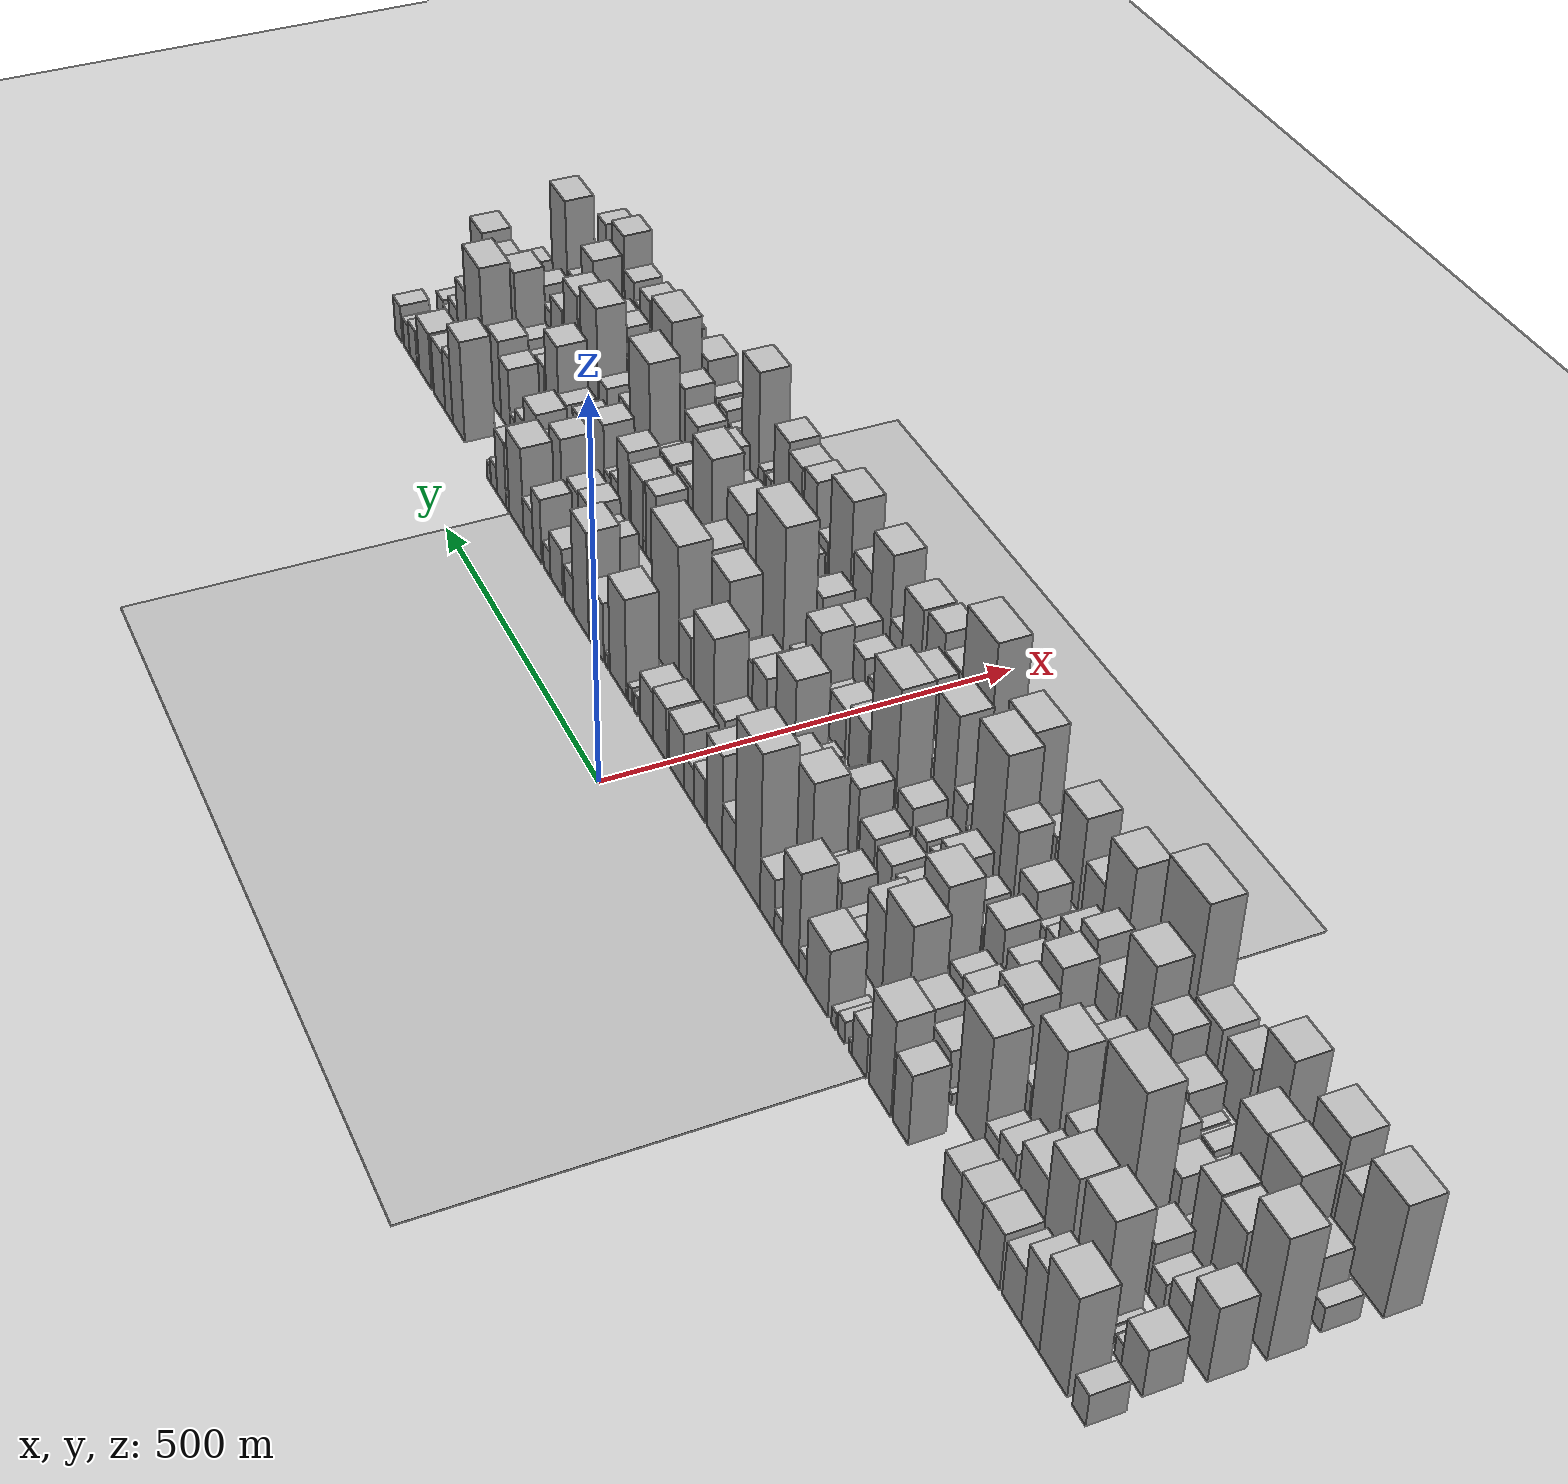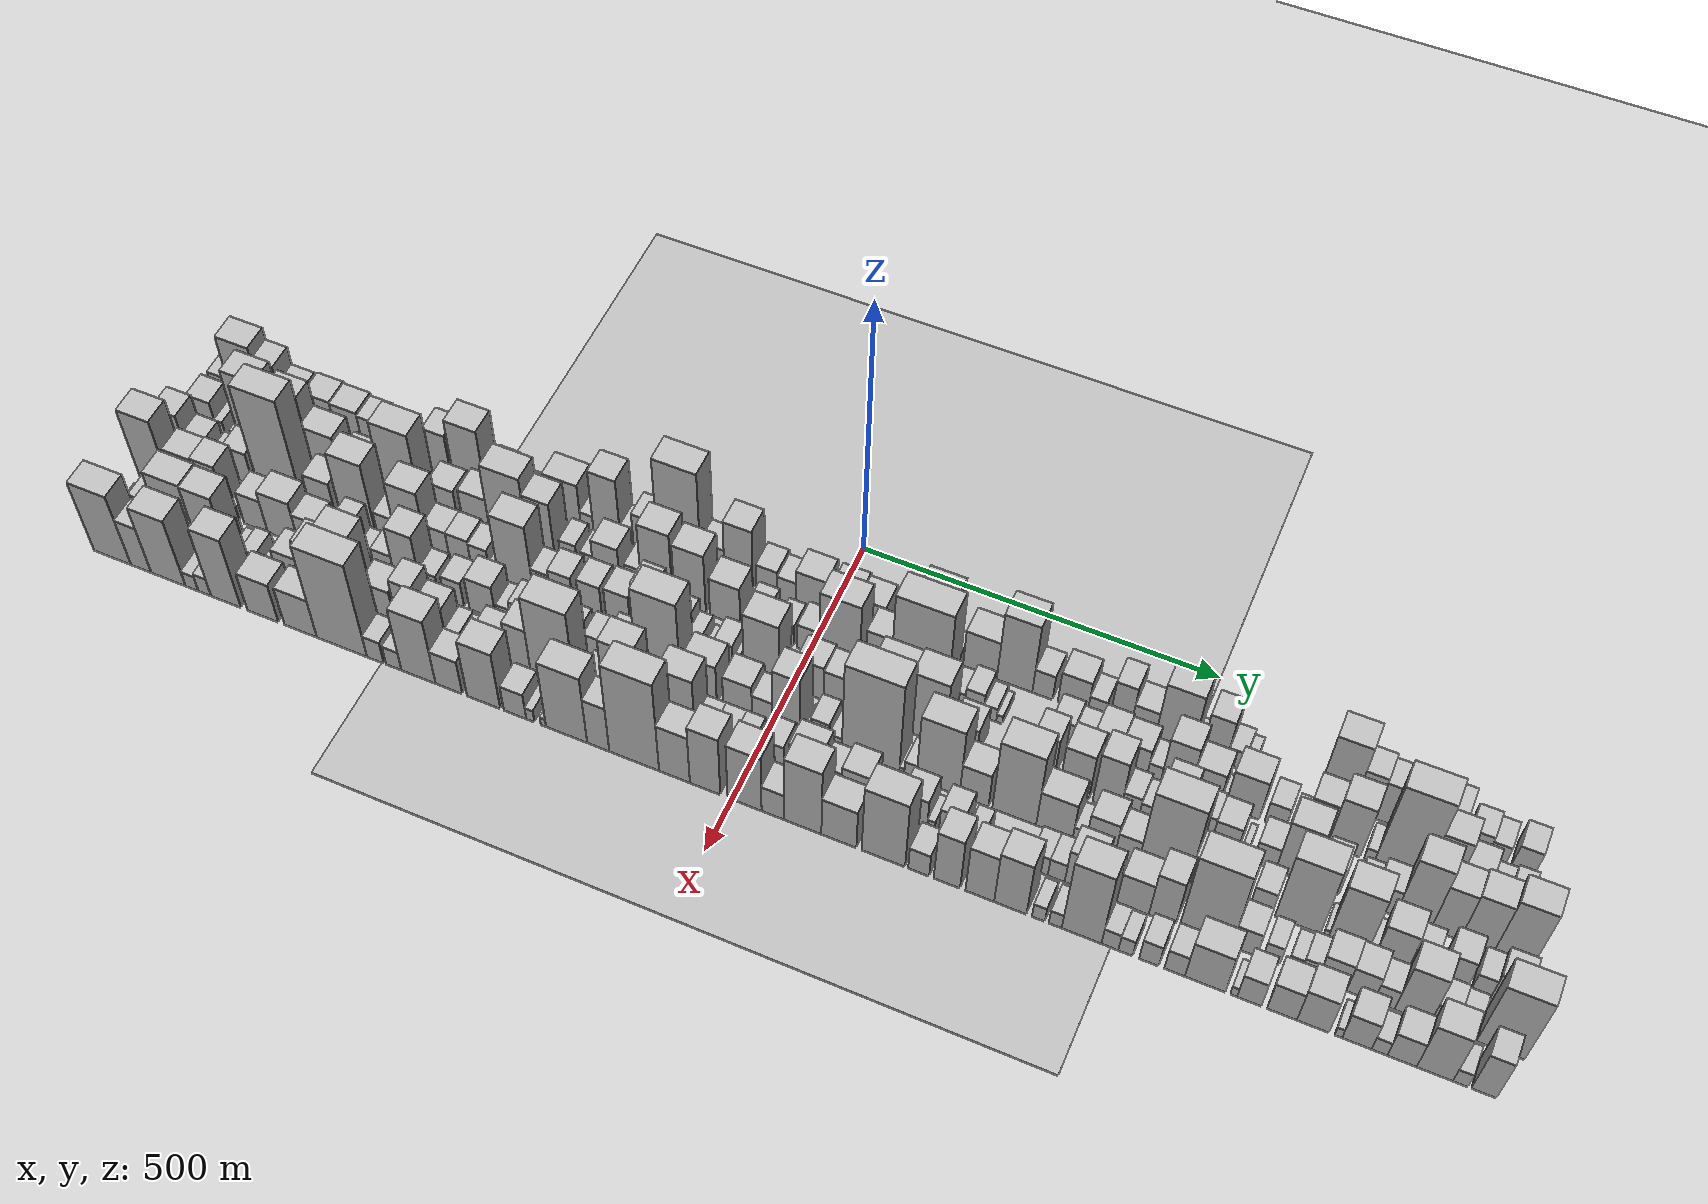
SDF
<?xml version="1.0" encoding="utf-8"?>

<sdf version="1.6">

   <world name="default">

      <gui fullscreen="0">

         <camera name="user_camera">

            <pose>-15 0 4.57585 0 0 0</pose>

            <view_controller>orbit</view_controller>

         </camera>

      </gui>

      <scene>

         <sky>

           <clouds>

             <speed>12</speed>

           </clouds>

         </sky>

         <ambient>0.4 0.4 0.4 1</ambient>

         <background>0.7 0.7 0.7 1</background>

         <shadows>1</shadows>

      </scene>

      <gravity>0 0 -9.8066</gravity>

      <magnetic_field>6e-06 2.3e-05 -4.2e-05</magnetic_field>

      <physics default="0" name="default_physics" type="ode">

         <ode>

            <solver>

               <type>quick</type>

               <iters>10</iters>

               <sor>1.0</sor>

               <use_dynamic_moi_rescaling>0</use_dynamic_moi_rescaling>

            </solver>

            <constraints>

               <cfm>0</cfm>

               <erp>0.2</erp>

               <contact_max_correcting_vel>100</contact_max_correcting_vel>

               <contact_surface_layer>0.001</contact_surface_layer>

            </constraints>

         </ode>

         <max_step_size>0.004</max_step_size>

         <real_time_factor>1</real_time_factor>

         <real_time_update_rate>250</real_time_update_rate>

      </physics>

      <light name="sun" type="directional">

         <cast_shadows>1</cast_shadows>

         <pose>0 0 10 0 0 0</pose>

         <diffuse>0.8 0.8 0.8 1</diffuse>

         <specular>0.2 0.2 0.2 1</specular>

         <attenuation>

            <range>1000</range>

            <constant>0.9</constant>

            <linear>0.01</linear>

            <quadratic>0.001</quadratic>

         </attenuation>

         <direction>-0.5 0.1 -0.9</direction>

      </light>

      <include>

         <name>ground_plane_1</name>

         <uri>model://HANNAS_ground_plane</uri>

         <pose>0 0 0  0 0 0</pose>

      </include>

      <include>

         <name>ground_plane_2</name>

         <uri>model://HANNAS_ground_plane</uri>

         <pose>100 0 0  0 0 0</pose>

      </include>

      <model name="building_1">

         <static>1</static>

         <pose frame="">100.0000 -928.0170 0 0.000000 0.000000 0.000000</pose>

         <link name="link">

            <pose frame="">0 0 21.00 0 0 0</pose>

            <collision name="collision">

               <geometry>

                  <box>

                     <size>40.0000 23.9660 42.0000</size>

                  </box>

               </geometry>

               <max_contacts>10</max_contacts>

               <surface>

                  <contact>

                     <ode/>

                  </contact>

                  <bounce/>

                  <friction>

                     <torsional>

                        <ode/>

                     </torsional>

                     <ode/>

                  </friction>

               </surface>

            </collision>

            <visual name="visual">

               <cast_shadows>0</cast_shadows>

               <geometry>

                  <box>

                     <size>40.0000 23.9660 42.0000</size>

                  </box>

               </geometry>

               <material>

                  <script>

                     <uri>model://HANNAS_wall/materials/scripts</uri>

                     <uri>model://HANNAS_wall/materials/textures</uri>

                     <name>vrc/HANNAS_wall</name>

                  </script>

               </material>

            </visual>

            <self_collide>0</self_collide>

            <enable_wind>0</enable_wind>

            <kinematic>0</kinematic>

         </link>

      </model>

      <model name="building_2">

         <static>1</static>

         <pose frame="">100.0000 -881.4012 0 0.000000 0.000000 0.000000</pose>

         <link name="link">

            <pose frame="">0 0 66.00 0 0 0</pose>

            <collision name="collision">

               <geometry>

                  <box>

                     <size>40.0000 51.2656 132.0000</size>

                  </box>

               </geometry>

               <max_contacts>10</max_contacts>

               <surface>

                  <contact>

                     <ode/>

                  </contact>

                  <bounce/>

                  <friction>

                     <torsional>

                        <ode/>

                     </torsional>

                     <ode/>

                  </friction>

               </surface>

            </collision>

            <visual name="visual">

               <cast_shadows>0</cast_shadows>

               <geometry>

                  <box>

                     <size>40.0000 51.2656 132.0000</size>

                  </box>

               </geometry>

               <material>

                  <script>

                     <uri>model://HANNAS_wall/materials/scripts</uri>

                     <uri>model://HANNAS_wall/materials/textures</uri>

                     <name>vrc/HANNAS_wall</name>

                  </script>

               </material>

            </visual>

            <self_collide>0</self_collide>

            <enable_wind>0</enable_wind>

            <kinematic>0</kinematic>

         </link>

      </model>

      <model name="building_3">

         <static>1</static>

         <pose frame="">100.0000 -838.8127 0 0.000000 0.000000 0.000000</pose>

         <link name="link">

            <pose frame="">0 0 54.00 0 0 0</pose>

            <collision name="collision">

               <geometry>

                  <box>

                     <size>40.0000 33.9112 108.0000</size>

                  </box>

               </geometry>

               <max_contacts>10</max_contacts>

               <surface>

                  <contact>

                     <ode/>

                  </contact>

                  <bounce/>

                  <friction>

                     <torsional>

                        <ode/>

                     </torsional>

                     <ode/>

                  </friction>

               </surface>

            </collision>

            <visual name="visual">

               <cast_shadows>0</cast_shadows>

               <geometry>

                  <box>

                     <size>40.0000 33.9112 108.0000</size>

                  </box>

               </geometry>

               <material>

                  <script>

                     <uri>model://HANNAS_wall/materials/scripts</uri>

                     <uri>model://HANNAS_wall/materials/textures</uri>

                     <name>vrc/HANNAS_wall</name>

                  </script>

               </material>

            </visual>

            <self_collide>0</self_collide>

            <enable_wind>0</enable_wind>

            <kinematic>0</kinematic>

         </link>

      </model>

      <model name="building_4">

         <static>1</static>

         <pose frame="">100.0000 -803.6682 0 0.000000 0.000000 0.000000</pose>

         <link name="link">

            <pose frame="">0 0 36.00 0 0 0</pose>

            <collision name="collision">

               <geometry>

                  <box>

                     <size>40.0000 36.3779 72.0000</size>

                  </box>

               </geometry>

               <max_contacts>10</max_contacts>

               <surface>

                  <contact>

                     <ode/>

                  </contact>

                  <bounce/>

                  <friction>

                     <torsional>

                        <ode/>

                     </torsional>

                     <ode/>

                  </friction>

               </surface>

            </collision>

            <visual name="visual">

               <cast_shadows>0</cast_shadows>

               <geometry>

                  <box>

                     <size>40.0000 36.3779 72.0000</size>

                  </box>

               </geometry>

               <material>

                  <script>

                     <uri>model://HANNAS_wall/materials/scripts</uri>

                     <uri>model://HANNAS_wall/materials/textures</uri>

                     <name>vrc/HANNAS_wall</name>

                  </script>

               </material>

            </visual>

            <self_collide>0</self_collide>

            <enable_wind>0</enable_wind>

            <kinematic>0</kinematic>

         </link>

      </model>

      <model name="building_5">

         <static>1</static>

         <pose frame="">100.0000 -760.2325 0 0.000000 0.000000 0.000000</pose>

         <link name="link">

            <pose frame="">0 0 37.50 0 0 0</pose>

            <collision name="collision">

               <geometry>

                  <box>

                     <size>40.0000 40.4935 75.0000</size>

                  </box>

               </geometry>

               <max_contacts>10</max_contacts>

               <surface>

                  <contact>

                     <ode/>

                  </contact>

                  <bounce/>

                  <friction>

                     <torsional>

                        <ode/>

                     </torsional>

                     <ode/>

                  </friction>

               </surface>

            </collision>

            <visual name="visual">

               <cast_shadows>0</cast_shadows>

               <geometry>

                  <box>

                     <size>40.0000 40.4935 75.0000</size>

                  </box>

               </geometry>

               <material>

                  <script>

                     <uri>model://HANNAS_wall/materials/scripts</uri>

                     <uri>model://HANNAS_wall/materials/textures</uri>

                     <name>vrc/HANNAS_wall</name>

                  </script>

               </material>

            </visual>

            <self_collide>0</self_collide>

            <enable_wind>0</enable_wind>

            <kinematic>0</kinematic>

         </link>

      </model>

      <model name="building_6">

         <static>1</static>

         <pose frame="">100.0000 -719.3394 0 0.000000 0.000000 0.000000</pose>

         <link name="link">

            <pose frame="">0 0 36.00 0 0 0</pose>

            <collision name="collision">

               <geometry>

                  <box>

                     <size>40.0000 41.2927 72.0000</size>

                  </box>

               </geometry>

               <max_contacts>10</max_contacts>

               <surface>

                  <contact>

                     <ode/>

                  </contact>

                  <bounce/>

                  <friction>

                     <torsional>

                        <ode/>

                     </torsional>

                     <ode/>

                  </friction>

               </surface>

            </collision>

            <visual name="visual">

               <cast_shadows>0</cast_shadows>

               <geometry>

                  <box>

                     <size>40.0000 41.2927 72.0000</size>

                  </box>

               </geometry>

               <material>

                  <script>

                     <uri>model://HANNAS_wall/materials/scripts</uri>

                     <uri>model://HANNAS_wall/materials/textures</uri>

                     <name>vrc/HANNAS_wall</name>

                  </script>

               </material>

            </visual>

            <self_collide>0</self_collide>

            <enable_wind>0</enable_wind>

            <kinematic>0</kinematic>

         </link>

      </model>

      <model name="building_7">

         <static>1</static>

         <pose frame="">100.0000 -681.7524 0 0.000000 0.000000 0.000000</pose>

         <link name="link">

            <pose frame="">0 0 33.00 0 0 0</pose>

            <collision name="collision">

               <geometry>

                  <box>

                     <size>40.0000 33.8814 66.0000</size>

                  </box>

               </geometry>

               <max_contacts>10</max_contacts>

               <surface>

                  <contact>

                     <ode/>

                  </contact>

                  <bounce/>

                  <friction>

                     <torsional>

                        <ode/>

                     </torsional>

                     <ode/>

                  </friction>

               </surface>

            </collision>

            <visual name="visual">

               <cast_shadows>0</cast_shadows>

               <geometry>

                  <box>

                     <size>40.0000 33.8814 66.0000</size>

                  </box>

               </geometry>

               <material>

                  <script>

                     <uri>model://HANNAS_wall/materials/scripts</uri>

                     <uri>model://HANNAS_wall/materials/textures</uri>

                     <name>vrc/HANNAS_wall</name>

                  </script>

               </material>

            </visual>

            <self_collide>0</self_collide>

            <enable_wind>0</enable_wind>

            <kinematic>0</kinematic>

         </link>

      </model>

      <model name="building_8">

         <static>1</static>

         <pose frame="">100.0000 -577.4035 0 0.000000 0.000000 0.000000</pose>

         <link name="link">

            <pose frame="">0 0 46.50 0 0 0</pose>

            <collision name="collision">

               <geometry>

                  <box>

                     <size>40.0000 33.6054 93.0000</size>

                  </box>

               </geometry>

               <max_contacts>10</max_contacts>

               <surface>

                  <contact>

                     <ode/>

                  </contact>

                  <bounce/>

                  <friction>

                     <torsional>

                        <ode/>

                     </torsional>

                     <ode/>

                  </friction>

               </surface>

            </collision>

            <visual name="visual">

               <cast_shadows>0</cast_shadows>

               <geometry>

                  <box>

                     <size>40.0000 33.6054 93.0000</size>

                  </box>

               </geometry>

               <material>

                  <script>

                     <uri>model://HANNAS_wall/materials/scripts</uri>

                     <uri>model://HANNAS_wall/materials/textures</uri>

                     <name>vrc/HANNAS_wall</name>

                  </script>

               </material>

            </visual>

            <self_collide>0</self_collide>

            <enable_wind>0</enable_wind>

            <kinematic>0</kinematic>

         </link>

      </model>

      <model name="building_9">

         <static>1</static>

         <pose frame="">100.0000 -532.4892 0 0.000000 0.000000 0.000000</pose>

         <link name="link">

            <pose frame="">0 0 64.50 0 0 0</pose>

            <collision name="collision">

               <geometry>

                  <box>

                     <size>40.0000 48.2231 129.0000</size>

                  </box>

               </geometry>

               <max_contacts>10</max_contacts>

               <surface>

                  <contact>

                     <ode/>

                  </contact>

                  <bounce/>

                  <friction>

                     <torsional>

                        <ode/>

                     </torsional>

                     <ode/>

                  </friction>

               </surface>

            </collision>

            <visual name="visual">

               <cast_shadows>0</cast_shadows>

               <geometry>

                  <box>

                     <size>40.0000 48.2231 129.0000</size>

                  </box>

               </geometry>

               <material>

                  <script>

                     <uri>model://HANNAS_wall/materials/scripts</uri>

                     <uri>model://HANNAS_wall/materials/textures</uri>

                     <name>vrc/HANNAS_wall</name>

                  </script>

               </material>

            </visual>

            <self_collide>0</self_collide>

            <enable_wind>0</enable_wind>

            <kinematic>0</kinematic>

         </link>

      </model>

      <model name="building_10">

         <static>1</static>

         <pose frame="">100.0000 -486.0561 0 0.000000 0.000000 0.000000</pose>

         <link name="link">

            <pose frame="">0 0 30.00 0 0 0</pose>

            <collision name="collision">

               <geometry>

                  <box>

                     <size>40.0000 32.6432 60.0000</size>

                  </box>

               </geometry>

               <max_contacts>10</max_contacts>

               <surface>

                  <contact>

                     <ode/>

                  </contact>

                  <bounce/>

                  <friction>

                     <torsional>

                        <ode/>

                     </torsional>

                     <ode/>

                  </friction>

               </surface>

            </collision>

            <visual name="visual">

               <cast_shadows>0</cast_shadows>

               <geometry>

                  <box>

                     <size>40.0000 32.6432 60.0000</size>

                  </box>

               </geometry>

               <material>

                  <script>

                     <uri>model://HANNAS_wall/materials/scripts</uri>

                     <uri>model://HANNAS_wall/materials/textures</uri>

                     <name>vrc/HANNAS_wall</name>

                  </script>

               </material>

            </visual>

            <self_collide>0</self_collide>

            <enable_wind>0</enable_wind>

            <kinematic>0</kinematic>

         </link>

      </model>

      <model name="building_11">

         <static>1</static>

         <pose frame="">100.0000 -465.9035 0 0.000000 0.000000 0.000000</pose>

         <link name="link">

            <pose frame="">0 0 9.00 0 0 0</pose>

            <collision name="collision">

               <geometry>

                  <box>

                     <size>40.0000 7.6619 18.0000</size>

                  </box>

               </geometry>

               <max_contacts>10</max_contacts>

               <surface>

                  <contact>

                     <ode/>

                  </contact>

                  <bounce/>

                  <friction>

                     <torsional>

                        <ode/>

                     </torsional>

                     <ode/>

                  </friction>

               </surface>

            </collision>

            <visual name="visual">

               <cast_shadows>0</cast_shadows>

               <geometry>

                  <box>

                     <size>40.0000 7.6619 18.0000</size>

                  </box>

               </geometry>

               <material>

                  <script>

                     <uri>model://HANNAS_wall/materials/scripts</uri>

                     <uri>model://HANNAS_wall/materials/textures</uri>

                     <name>vrc/HANNAS_wall</name>

                  </script>

               </material>

            </visual>

            <self_collide>0</self_collide>

            <enable_wind>0</enable_wind>

            <kinematic>0</kinematic>

         </link>

      </model>

      <model name="building_12">

         <static>1</static>

         <pose frame="">100.0000 -445.1040 0 0.000000 0.000000 0.000000</pose>

         <link name="link">

            <pose frame="">0 0 15.00 0 0 0</pose>

            <collision name="collision">

               <geometry>

                  <box>

                     <size>40.0000 15.9371 30.0000</size>

                  </box>

               </geometry>

               <max_contacts>10</max_contacts>

               <surface>

                  <contact>

                     <ode/>

                  </contact>

                  <bounce/>

                  <friction>

                     <torsional>

                        <ode/>

                     </torsional>

                     <ode/>

                  </friction>

               </surface>

            </collision>

            <visual name="visual">

               <cast_shadows>0</cast_shadows>

               <geometry>

                  <box>

                     <size>40.0000 15.9371 30.0000</size>

                  </box>

               </geometry>

               <material>

                  <script>

                     <uri>model://HANNAS_wall/materials/scripts</uri>

                     <uri>model://HANNAS_wall/materials/textures</uri>

                     <name>vrc/HANNAS_wall</name>

                  </script>

               </material>

            </visual>

            <self_collide>0</self_collide>

            <enable_wind>0</enable_wind>

            <kinematic>0</kinematic>

         </link>

      </model>

      <model name="building_13">

         <static>1</static>

         <pose frame="">100.0000 -427.6793 0 0.000000 0.000000 0.000000</pose>

         <link name="link">

            <pose frame="">0 0 12.00 0 0 0</pose>

            <collision name="collision">

               <geometry>

                  <box>

                     <size>40.0000 10.9123 24.0000</size>

                  </box>

               </geometry>

               <max_contacts>10</max_contacts>

               <surface>

                  <contact>

                     <ode/>

                  </contact>

                  <bounce/>

                  <friction>

                     <torsional>

                        <ode/>

                     </torsional>

                     <ode/>

                  </friction>

               </surface>

            </collision>

            <visual name="visual">

               <cast_shadows>0</cast_shadows>

               <geometry>

                  <box>

                     <size>40.0000 10.9123 24.0000</size>

                  </box>

               </geometry>

               <material>

                  <script>

                     <uri>model://HANNAS_wall/materials/scripts</uri>

                     <uri>model://HANNAS_wall/materials/textures</uri>

                     <name>vrc/HANNAS_wall</name>

                  </script>

               </material>

            </visual>

            <self_collide>0</self_collide>

            <enable_wind>0</enable_wind>

            <kinematic>0</kinematic>

         </link>

      </model>

      <model name="building_14">

         <static>1</static>

         <pose frame="">100.0000 -388.5690 0 0.000000 0.000000 0.000000</pose>

         <link name="link">

            <pose frame="">0 0 45.00 0 0 0</pose>

            <collision name="collision">

               <geometry>

                  <box>

                     <size>40.0000 51.3082 90.0000</size>

                  </box>

               </geometry>

               <max_contacts>10</max_contacts>

               <surface>

                  <contact>

                     <ode/>

                  </contact>

                  <bounce/>

                  <friction>

                     <torsional>

                        <ode/>

                     </torsional>

                     <ode/>

                  </friction>

               </surface>

            </collision>

            <visual name="visual">

               <cast_shadows>0</cast_shadows>

               <geometry>

                  <box>

                     <size>40.0000 51.3082 90.0000</size>

                  </box>

               </geometry>

               <material>

                  <script>

                     <uri>model://HANNAS_wall/materials/scripts</uri>

                     <uri>model://HANNAS_wall/materials/textures</uri>

                     <name>vrc/HANNAS_wall</name>

                  </script>

               </material>

            </visual>

            <self_collide>0</self_collide>

            <enable_wind>0</enable_wind>

            <kinematic>0</kinematic>

         </link>

      </model>

      <model name="building_15">

         <static>1</static>

         <pose frame="">100.0000 -353.4953 0 0.000000 0.000000 0.000000</pose>

         <link name="link">

            <pose frame="">0 0 16.50 0 0 0</pose>

            <collision name="collision">

               <geometry>

                  <box>

                     <size>40.0000 18.8391 33.0000</size>

                  </box>

               </geometry>

               <max_contacts>10</max_contacts>

               <surface>

                  <contact>

                     <ode/>

                  </contact>

                  <bounce/>

                  <friction>

                     <torsional>

                        <ode/>

                     </torsional>

                     <ode/>

                  </friction>

               </surface>

            </collision>

            <visual name="visual">

               <cast_shadows>0</cast_shadows>

               <geometry>

                  <box>

                     <size>40.0000 18.8391 33.0000</size>

                  </box>

               </geometry>

               <material>

                  <script>

                     <uri>model://HANNAS_wall/materials/scripts</uri>

                     <uri>model://HANNAS_wall/materials/textures</uri>

                     <name>vrc/HANNAS_wall</name>

                  </script>

               </material>

            </visual>

            <self_collide>0</self_collide>

            <enable_wind>0</enable_wind>

            <kinematic>0</kinematic>

         </link>

      </model>

      <model name="building_16">

         <static>1</static>

         <pose frame="">100.0000 -323.8756 0 0.000000 0.000000 0.000000</pose>

         <link name="link">

            <pose frame="">0 0 66.00 0 0 0</pose>

            <collision name="collision">

               <geometry>

                  <box>

                     <size>40.0000 40.4003 132.0000</size>

                  </box>

               </geometry>

               <max_contacts>10</max_contacts>

               <surface>

                  <contact>

                     <ode/>

                  </contact>

                  <bounce/>

                  <friction>

                     <torsional>

                        <ode/>

                     </torsional>

                     <ode/>

                  </friction>

               </surface>

            </collision>

            <visual name="visual">

               <cast_shadows>0</cast_shadows>

               <geometry>

                  <box>

                     <size>40.0000 40.4003 132.0000</size>

                  </box>

               </geometry>

               <material>

                  <script>

                     <uri>model://HANNAS_wall/materials/scripts</uri>

                     <uri>model://HANNAS_wall/materials/textures</uri>

                     <name>vrc/HANNAS_wall</name>

                  </script>

               </material>

            </visual>

            <self_collide>0</self_collide>

            <enable_wind>0</enable_wind>

            <kinematic>0</kinematic>

         </link>

      </model>

      <model name="building_17">

         <static>1</static>

         <pose frame="">100.0000 -293.9246 0 0.000000 0.000000 0.000000</pose>

         <link name="link">

            <pose frame="">0 0 16.50 0 0 0</pose>

            <collision name="collision">

               <geometry>

                  <box>

                     <size>40.0000 19.5017 33.0000</size>

                  </box>

               </geometry>

               <max_contacts>10</max_contacts>

               <surface>

                  <contact>

                     <ode/>

                  </contact>

                  <bounce/>

                  <friction>

                     <torsional>

                        <ode/>

                     </torsional>

                     <ode/>

                  </friction>

               </surface>

            </collision>

            <visual name="visual">

               <cast_shadows>0</cast_shadows>

               <geometry>

                  <box>

                     <size>40.0000 19.5017 33.0000</size>

                  </box>

               </geometry>

               <material>

                  <script>

                     <uri>model://HANNAS_wall/materials/scripts</uri>

                     <uri>model://HANNAS_wall/materials/textures</uri>

                     <name>vrc/HANNAS_wall</name>

                  </script>

               </material>

            </visual>

            <self_collide>0</self_collide>

            <enable_wind>0</enable_wind>

            <kinematic>0</kinematic>

         </link>

      </model>

      <model name="building_18">

         <static>1</static>

         <pose frame="">100.0000 -266.0162 0 0.000000 0.000000 0.000000</pose>

         <link name="link">

            <pose frame="">0 0 36.00 0 0 0</pose>

            <collision name="collision">

               <geometry>

                  <box>

                     <size>40.0000 36.3152 72.0000</size>

                  </box>

               </geometry>

               <max_contacts>10</max_contacts>

               <surface>

                  <contact>

                     <ode/>

                  </contact>

                  <bounce/>

                  <friction>

                     <torsional>

                        <ode/>

                     </torsional>

                     <ode/>

                  </friction>

               </surface>

            </collision>

            <visual name="visual">

               <cast_shadows>0</cast_shadows>

               <geometry>

                  <box>

                     <size>40.0000 36.3152 72.0000</size>

                  </box>

               </geometry>

               <material>

                  <script>

                     <uri>model://HANNAS_wall/materials/scripts</uri>

                     <uri>model://HANNAS_wall/materials/textures</uri>

                     <name>vrc/HANNAS_wall</name>

                  </script>

               </material>

            </visual>

            <self_collide>0</self_collide>

            <enable_wind>0</enable_wind>

            <kinematic>0</kinematic>

         </link>

      </model>

      <model name="building_19">

         <static>1</static>

         <pose frame="">100.0000 -216.1852 0 0.000000 0.000000 0.000000</pose>

         <link name="link">

            <pose frame="">0 0 105.00 0 0 0</pose>

            <collision name="collision">

               <geometry>

                  <box>

                     <size>40.0000 63.3468 210.0000</size>

                  </box>

               </geometry>

               <max_contacts>10</max_contacts>

               <surface>

                  <contact>

                     <ode/>

                  </contact>

                  <bounce/>

                  <friction>

                     <torsional>

                        <ode/>

                     </torsional>

                     <ode/>

                  </friction>

               </surface>

            </collision>

            <visual name="visual">

               <cast_shadows>0</cast_shadows>

               <geometry>

                  <box>

                     <size>40.0000 63.3468 210.0000</size>

                  </box>

               </geometry>

               <material>

                  <script>

                     <uri>model://HANNAS_wall/materials/scripts</uri>

                     <uri>model://HANNAS_wall/materials/textures</uri>

                     <name>vrc/HANNAS_wall</name>

                  </script>

               </material>

            </visual>

            <self_collide>0</self_collide>

            <enable_wind>0</enable_wind>

            <kinematic>0</kinematic>

         </link>

      </model>

      <model name="building_20">

         <static>1</static>

         <pose frame="">100.0000 -167.2944 0 0.000000 0.000000 0.000000</pose>

         <link name="link">

            <pose frame="">0 0 33.00 0 0 0</pose>

            <collision name="collision">

               <geometry>

                  <box>

                     <size>40.0000 34.4347 66.0000</size>

                  </box>

               </geometry>

               <max_contacts>10</max_contacts>

               <surface>

                  <contact>

                     <ode/>

                  </contact>

                  <bounce/>

                  <friction>

                     <torsional>

                        <ode/>

                     </torsional>

                     <ode/>

                  </friction>

               </surface>

            </collision>

            <visual name="visual">

               <cast_shadows>0</cast_shadows>

               <geometry>

                  <box>

                     <size>40.0000 34.4347 66.0000</size>

                  </box>

               </geometry>

               <material>

                  <script>

                     <uri>model://HANNAS_wall/materials/scripts</uri>

                     <uri>model://HANNAS_wall/materials/textures</uri>

                     <name>vrc/HANNAS_wall</name>

                  </script>

               </material>

            </visual>

            <self_collide>0</self_collide>

            <enable_wind>0</enable_wind>

            <kinematic>0</kinematic>

         </link>

      </model>

      <model name="building_21">

         <static>1</static>

         <pose frame="">100.0000 -129.6058 0 0.000000 0.000000 0.000000</pose>

         <link name="link">

            <pose frame="">0 0 64.50 0 0 0</pose>

            <collision name="collision">

               <geometry>

                  <box>

                     <size>40.0000 40.9424 129.0000</size>

                  </box>

               </geometry>

               <max_contacts>10</max_contacts>

               <surface>

                  <contact>

                     <ode/>

                  </contact>

                  <bounce/>

                  <friction>

                     <torsional>

                        <ode/>

                     </torsional>

                     <ode/>

                  </friction>

               </surface>

            </collision>

            <visual name="visual">

               <cast_shadows>0</cast_shadows>

               <geometry>

                  <box>

                     <size>40.0000 40.9424 129.0000</size>

                  </box>

               </geometry>

               <material>

                  <script>

                     <uri>model://HANNAS_wall/materials/scripts</uri>

                     <uri>model://HANNAS_wall/materials/textures</uri>

                     <name>vrc/HANNAS_wall</name>

                  </script>

               </material>

            </visual>

            <self_collide>0</self_collide>

            <enable_wind>0</enable_wind>

            <kinematic>0</kinematic>

         </link>

      </model>

      <model name="building_22">

         <static>1</static>

         <pose frame="">100.0000 -88.7523 0 0.000000 0.000000 0.000000</pose>

         <link name="link">

            <pose frame="">0 0 30.00 0 0 0</pose>

            <collision name="collision">

               <geometry>

                  <box>

                     <size>40.0000 30.7647 60.0000</size>

                  </box>

               </geometry>

               <max_contacts>10</max_contacts>

               <surface>

                  <contact>

                     <ode/>

                  </contact>

                  <bounce/>

                  <friction>

                     <torsional>

                        <ode/>

                     </torsional>

                     <ode/>

                  </friction>

               </surface>

            </collision>

            <visual name="visual">

               <cast_shadows>0</cast_shadows>

               <geometry>

                  <box>

                     <size>40.0000 30.7647 60.0000</size>

                  </box>

               </geometry>

               <material>

                  <script>

                     <uri>model://HANNAS_wall/materials/scripts</uri>

                     <uri>model://HANNAS_wall/materials/textures</uri>

                     <name>vrc/HANNAS_wall</name>

                  </script>

               </material>

            </visual>

            <self_collide>0</self_collide>

            <enable_wind>0</enable_wind>

            <kinematic>0</kinematic>

         </link>

      </model>

      <model name="building_23">

         <static>1</static>

         <pose frame="">100.0000 -59.9895 0 0.000000 0.000000 0.000000</pose>

         <link name="link">

            <pose frame="">0 0 25.50 0 0 0</pose>

            <collision name="collision">

               <geometry>

                  <box>

                     <size>40.0000 26.7610 51.0000</size>

                  </box>

               </geometry>

               <max_contacts>10</max_contacts>

               <surface>

                  <contact>

                     <ode/>

                  </contact>

                  <bounce/>

                  <friction>

                     <torsional>

                        <ode/>

                     </torsional>

                     <ode/>

                  </friction>

               </surface>

            </collision>

            <visual name="visual">

               <cast_shadows>0</cast_shadows>

               <geometry>

                  <box>

                     <size>40.0000 26.7610 51.0000</size>

                  </box>

               </geometry>

               <material>

                  <script>

                     <uri>model://HANNAS_wall/materials/scripts</uri>

                     <uri>model://HANNAS_wall/materials/textures</uri>

                     <name>vrc/HANNAS_wall</name>

                  </script>

               </material>

            </visual>

            <self_collide>0</self_collide>

            <enable_wind>0</enable_wind>

            <kinematic>0</kinematic>

         </link>

      </model>

      <model name="building_24">

         <static>1</static>

         <pose frame="">100.0000 -25.3485 0 0.000000 0.000000 0.000000</pose>

         <link name="link">

            <pose frame="">0 0 39.00 0 0 0</pose>

            <collision name="collision">

               <geometry>

                  <box>

                     <size>40.0000 42.5211 78.0000</size>

                  </box>

               </geometry>

               <max_contacts>10</max_contacts>

               <surface>

                  <contact>

                     <ode/>

                  </contact>

                  <bounce/>

                  <friction>

                     <torsional>

                        <ode/>

                     </torsional>

                     <ode/>

                  </friction>

               </surface>

            </collision>

            <visual name="visual">

               <cast_shadows>0</cast_shadows>

               <geometry>

                  <box>

                     <size>40.0000 42.5211 78.0000</size>

                  </box>

               </geometry>

               <material>

                  <script>

                     <uri>model://HANNAS_wall/materials/scripts</uri>

                     <uri>model://HANNAS_wall/materials/textures</uri>

                     <name>vrc/HANNAS_wall</name>

                  </script>

               </material>

            </visual>

            <self_collide>0</self_collide>

            <enable_wind>0</enable_wind>

            <kinematic>0</kinematic>

         </link>

      </model>

      <model name="building_25">

         <static>1</static>

         <pose frame="">100.0000 22.5860 0 0.000000 0.000000 0.000000</pose>

         <link name="link">

            <pose frame="">0 0 37.50 0 0 0</pose>

            <collision name="collision">

               <geometry>

                  <box>

                     <size>40.0000 39.3479 75.0000</size>

                  </box>

               </geometry>

               <max_contacts>10</max_contacts>

               <surface>

                  <contact>

                     <ode/>

                  </contact>

                  <bounce/>

                  <friction>

                     <torsional>

                        <ode/>

                     </torsional>

                     <ode/>

                  </friction>

               </surface>

            </collision>

            <visual name="visual">

               <cast_shadows>0</cast_shadows>

               <geometry>

                  <box>

                     <size>40.0000 39.3479 75.0000</size>

                  </box>

               </geometry>

               <material>

                  <script>

                     <uri>model://HANNAS_wall/materials/scripts</uri>

                     <uri>model://HANNAS_wall/materials/textures</uri>

                     <name>vrc/HANNAS_wall</name>

                  </script>

               </material>

            </visual>

            <self_collide>0</self_collide>

            <enable_wind>0</enable_wind>

            <kinematic>0</kinematic>

         </link>

      </model>

      <model name="building_26">

         <static>1</static>

         <pose frame="">100.0000 61.0567 0 0.000000 0.000000 0.000000</pose>

         <link name="link">

            <pose frame="">0 0 34.50 0 0 0</pose>

            <collision name="collision">

               <geometry>

                  <box>

                     <size>40.0000 37.5936 69.0000</size>

                  </box>

               </geometry>

               <max_contacts>10</max_contacts>

               <surface>

                  <contact>

                     <ode/>

                  </contact>

                  <bounce/>

                  <friction>

                     <torsional>

                        <ode/>

                     </torsional>

                     <ode/>

                  </friction>

               </surface>

            </collision>

            <visual name="visual">

               <cast_shadows>0</cast_shadows>

               <geometry>

                  <box>

                     <size>40.0000 37.5936 69.0000</size>

                  </box>

               </geometry>

               <material>

                  <script>

                     <uri>model://HANNAS_wall/materials/scripts</uri>

                     <uri>model://HANNAS_wall/materials/textures</uri>

                     <name>vrc/HANNAS_wall</name>

                  </script>

               </material>

            </visual>

            <self_collide>0</self_collide>

            <enable_wind>0</enable_wind>

            <kinematic>0</kinematic>

         </link>

      </model>

      <model name="building_27">

         <static>1</static>

         <pose frame="">100.0000 92.4200 0 0.000000 0.000000 0.000000</pose>

         <link name="link">

            <pose frame="">0 0 13.50 0 0 0</pose>

            <collision name="collision">

               <geometry>

                  <box>

                     <size>40.0000 11.1330 27.0000</size>

                  </box>

               </geometry>

               <max_contacts>10</max_contacts>

               <surface>

                  <contact>

                     <ode/>

                  </contact>

                  <bounce/>

                  <friction>

                     <torsional>

                        <ode/>

                     </torsional>

                     <ode/>

                  </friction>

               </surface>

            </collision>

            <visual name="visual">

               <cast_shadows>0</cast_shadows>

               <geometry>

                  <box>

                     <size>40.0000 11.1330 27.0000</size>

                  </box>

               </geometry>

               <material>

                  <script>

                     <uri>model://HANNAS_wall/materials/scripts</uri>

                     <uri>model://HANNAS_wall/materials/textures</uri>

                     <name>vrc/HANNAS_wall</name>

                  </script>

               </material>

            </visual>

            <self_collide>0</self_collide>

            <enable_wind>0</enable_wind>

            <kinematic>0</kinematic>

         </link>

      </model>

      <model name="building_28">

         <static>1</static>

         <pose frame="">100.0000 109.4418 0 0.000000 0.000000 0.000000</pose>

         <link name="link">

            <pose frame="">0 0 13.50 0 0 0</pose>

            <collision name="collision">

               <geometry>

                  <box>

                     <size>40.0000 10.9106 27.0000</size>

                  </box>

               </geometry>

               <max_contacts>10</max_contacts>

               <surface>

                  <contact>

                     <ode/>

                  </contact>

                  <bounce/>

                  <friction>

                     <torsional>

                        <ode/>

                     </torsional>

                     <ode/>

                  </friction>

               </surface>

            </collision>

            <visual name="visual">

               <cast_shadows>0</cast_shadows>

               <geometry>

                  <box>

                     <size>40.0000 10.9106 27.0000</size>

                  </box>

               </geometry>

               <material>

                  <script>

                     <uri>model://HANNAS_wall/materials/scripts</uri>

                     <uri>model://HANNAS_wall/materials/textures</uri>

                     <name>vrc/HANNAS_wall</name>

                  </script>

               </material>

            </visual>

            <self_collide>0</self_collide>

            <enable_wind>0</enable_wind>

            <kinematic>0</kinematic>

         </link>

      </model>

      <model name="building_29">

         <static>1</static>

         <pose frame="">100.0000 118.0026 0 0.000000 0.000000 0.000000</pose>

         <link name="link">

            <pose frame="">0 0 7.50 0 0 0</pose>

            <collision name="collision">

               <geometry>

                  <box>

                     <size>40.0000 6.2110 15.0000</size>

                  </box>

               </geometry>

               <max_contacts>10</max_contacts>

               <surface>

                  <contact>

                     <ode/>

                  </contact>

                  <bounce/>

                  <friction>

                     <torsional>

                        <ode/>

                     </torsional>

                     <ode/>

                  </friction>

               </surface>

            </collision>

            <visual name="visual">

               <cast_shadows>0</cast_shadows>

               <geometry>

                  <box>

                     <size>40.0000 6.2110 15.0000</size>

                  </box>

               </geometry>

               <material>

                  <script>

                     <uri>model://HANNAS_wall/materials/scripts</uri>

                     <uri>model://HANNAS_wall/materials/textures</uri>

                     <name>vrc/HANNAS_wall</name>

                  </script>

               </material>

            </visual>

            <self_collide>0</self_collide>

            <enable_wind>0</enable_wind>

            <kinematic>0</kinematic>

         </link>

      </model>

      <model name="building_30">

         <static>1</static>

         <pose frame="">100.0000 146.1916 0 0.000000 0.000000 0.000000</pose>

         <link name="link">

            <pose frame="">0 0 69.00 0 0 0</pose>

            <collision name="collision">

               <geometry>

                  <box>

                     <size>40.0000 50.1669 138.0000</size>

                  </box>

               </geometry>

               <max_contacts>10</max_contacts>

               <surface>

                  <contact>

                     <ode/>

                  </contact>

                  <bounce/>

                  <friction>

                     <torsional>

                        <ode/>

                     </torsional>

                     <ode/>

                  </friction>

               </surface>

            </collision>

            <visual name="visual">

               <cast_shadows>0</cast_shadows>

               <geometry>

                  <box>

                     <size>40.0000 50.1669 138.0000</size>

                  </box>

               </geometry>

               <material>

                  <script>

                     <uri>model://HANNAS_wall/materials/scripts</uri>

                     <uri>model://HANNAS_wall/materials/textures</uri>

                     <name>vrc/HANNAS_wall</name>

                  </script>

               </material>

            </visual>

            <self_collide>0</self_collide>

            <enable_wind>0</enable_wind>

            <kinematic>0</kinematic>

         </link>

      </model>

      <model name="building_31">

         <static>1</static>

         <pose frame="">100.0000 179.9955 0 0.000000 0.000000 0.000000</pose>

         <link name="link">

            <pose frame="">0 0 10.50 0 0 0</pose>

            <collision name="collision">

               <geometry>

                  <box>

                     <size>40.0000 9.4410 21.0000</size>

                  </box>

               </geometry>

               <max_contacts>10</max_contacts>

               <surface>

                  <contact>

                     <ode/>

                  </contact>

                  <bounce/>

                  <friction>

                     <torsional>

                        <ode/>

                     </torsional>

                     <ode/>

                  </friction>

               </surface>

            </collision>

            <visual name="visual">

               <cast_shadows>0</cast_shadows>

               <geometry>

                  <box>

                     <size>40.0000 9.4410 21.0000</size>

                  </box>

               </geometry>

               <material>

                  <script>

                     <uri>model://HANNAS_wall/materials/scripts</uri>

                     <uri>model://HANNAS_wall/materials/textures</uri>

                     <name>vrc/HANNAS_wall</name>

                  </script>

               </material>

            </visual>

            <self_collide>0</self_collide>

            <enable_wind>0</enable_wind>

            <kinematic>0</kinematic>

         </link>

      </model>

      <model name="building_32">

         <static>1</static>

         <pose frame="">100.0000 213.1292 0 0.000000 0.000000 0.000000</pose>

         <link name="link">

            <pose frame="">0 0 42.00 0 0 0</pose>

            <collision name="collision">

               <geometry>

                  <box>

                     <size>40.0000 46.8263 84.0000</size>

                  </box>

               </geometry>

               <max_contacts>10</max_contacts>

               <surface>

                  <contact>

                     <ode/>

                  </contact>

                  <bounce/>

                  <friction>

                     <torsional>

                        <ode/>

                     </torsional>

                     <ode/>

                  </friction>

               </surface>

            </collision>

            <visual name="visual">

               <cast_shadows>0</cast_shadows>

               <geometry>

                  <box>

                     <size>40.0000 46.8263 84.0000</size>

                  </box>

               </geometry>

               <material>

                  <script>

                     <uri>model://HANNAS_wall/materials/scripts</uri>

                     <uri>model://HANNAS_wall/materials/textures</uri>

                     <name>vrc/HANNAS_wall</name>

                  </script>

               </material>

            </visual>

            <self_collide>0</self_collide>

            <enable_wind>0</enable_wind>

            <kinematic>0</kinematic>

         </link>

      </model>

      <model name="building_33">

         <static>1</static>

         <pose frame="">100.0000 260.9782 0 0.000000 0.000000 0.000000</pose>

         <link name="link">

            <pose frame="">0 0 75.00 0 0 0</pose>

            <collision name="collision">

               <geometry>

                  <box>

                     <size>40.0000 48.8718 150.0000</size>

                  </box>

               </geometry>

               <max_contacts>10</max_contacts>

               <surface>

                  <contact>

                     <ode/>

                  </contact>

                  <bounce/>

                  <friction>

                     <torsional>

                        <ode/>

                     </torsional>

                     <ode/>

                  </friction>

               </surface>

            </collision>

            <visual name="visual">

               <cast_shadows>0</cast_shadows>

               <geometry>

                  <box>

                     <size>40.0000 48.8718 150.0000</size>

                  </box>

               </geometry>

               <material>

                  <script>

                     <uri>model://HANNAS_wall/materials/scripts</uri>

                     <uri>model://HANNAS_wall/materials/textures</uri>

                     <name>vrc/HANNAS_wall</name>

                  </script>

               </material>

            </visual>

            <self_collide>0</self_collide>

            <enable_wind>0</enable_wind>

            <kinematic>0</kinematic>

         </link>

      </model>

      <model name="building_34">

         <static>1</static>

         <pose frame="">100.0000 299.3473 0 0.000000 0.000000 0.000000</pose>

         <link name="link">

            <pose frame="">0 0 27.00 0 0 0</pose>

            <collision name="collision">

               <geometry>

                  <box>

                     <size>40.0000 27.8662 54.0000</size>

                  </box>

               </geometry>

               <max_contacts>10</max_contacts>

               <surface>

                  <contact>

                     <ode/>

                  </contact>

                  <bounce/>

                  <friction>

                     <torsional>

                        <ode/>

                     </torsional>

                     <ode/>

                  </friction>

               </surface>

            </collision>

            <visual name="visual">

               <cast_shadows>0</cast_shadows>

               <geometry>

                  <box>

                     <size>40.0000 27.8662 54.0000</size>

                  </box>

               </geometry>

               <material>

                  <script>

                     <uri>model://HANNAS_wall/materials/scripts</uri>

                     <uri>model://HANNAS_wall/materials/textures</uri>

                     <name>vrc/HANNAS_wall</name>

                  </script>

               </material>

            </visual>

            <self_collide>0</self_collide>

            <enable_wind>0</enable_wind>

            <kinematic>0</kinematic>

         </link>

      </model>

      <model name="building_35">

         <static>1</static>

         <pose frame="">100.0000 340.6346 0 0.000000 0.000000 0.000000</pose>

         <link name="link">

            <pose frame="">0 0 34.50 0 0 0</pose>

            <collision name="collision">

               <geometry>

                  <box>

                     <size>40.0000 40.7085 69.0000</size>

                  </box>

               </geometry>

               <max_contacts>10</max_contacts>

               <surface>

                  <contact>

                     <ode/>

                  </contact>

                  <bounce/>

                  <friction>

                     <torsional>

                        <ode/>

                     </torsional>

                     <ode/>

                  </friction>

               </surface>

            </collision>

            <visual name="visual">

               <cast_shadows>0</cast_shadows>

               <geometry>

                  <box>

                     <size>40.0000 40.7085 69.0000</size>

                  </box>

               </geometry>

               <material>

                  <script>

                     <uri>model://HANNAS_wall/materials/scripts</uri>

                     <uri>model://HANNAS_wall/materials/textures</uri>

                     <name>vrc/HANNAS_wall</name>

                  </script>

               </material>

            </visual>

            <self_collide>0</self_collide>

            <enable_wind>0</enable_wind>

            <kinematic>0</kinematic>

         </link>

      </model>

      <model name="building_36">

         <static>1</static>

         <pose frame="">100.0000 372.6356 0 0.000000 0.000000 0.000000</pose>

         <link name="link">

            <pose frame="">0 0 19.50 0 0 0</pose>

            <collision name="collision">

               <geometry>

                  <box>

                     <size>40.0000 23.2934 39.0000</size>

                  </box>

               </geometry>

               <max_contacts>10</max_contacts>

               <surface>

                  <contact>

                     <ode/>

                  </contact>

                  <bounce/>

                  <friction>

                     <torsional>

                        <ode/>

                     </torsional>

                     <ode/>

                  </friction>

               </surface>

            </collision>

            <visual name="visual">

               <cast_shadows>0</cast_shadows>

               <geometry>

                  <box>

                     <size>40.0000 23.2934 39.0000</size>

                  </box>

               </geometry>

               <material>

                  <script>

                     <uri>model://HANNAS_wall/materials/scripts</uri>

                     <uri>model://HANNAS_wall/materials/textures</uri>

                     <name>vrc/HANNAS_wall</name>

                  </script>

               </material>

            </visual>

            <self_collide>0</self_collide>

            <enable_wind>0</enable_wind>

            <kinematic>0</kinematic>

         </link>

      </model>

      <model name="building_37">

         <static>1</static>

         <pose frame="">100.0000 404.6304 0 0.000000 0.000000 0.000000</pose>

         <link name="link">

            <pose frame="">0 0 46.50 0 0 0</pose>

            <collision name="collision">

               <geometry>

                  <box>

                     <size>40.0000 28.6962 93.0000</size>

                  </box>

               </geometry>

               <max_contacts>10</max_contacts>

               <surface>

                  <contact>

                     <ode/>

                  </contact>

                  <bounce/>

                  <friction>

                     <torsional>

                        <ode/>

                     </torsional>

                     <ode/>

                  </friction>

               </surface>

            </collision>

            <visual name="visual">

               <cast_shadows>0</cast_shadows>

               <geometry>

                  <box>

                     <size>40.0000 28.6962 93.0000</size>

                  </box>

               </geometry>

               <material>

                  <script>

                     <uri>model://HANNAS_wall/materials/scripts</uri>

                     <uri>model://HANNAS_wall/materials/textures</uri>

                     <name>vrc/HANNAS_wall</name>

                  </script>

               </material>

            </visual>

            <self_collide>0</self_collide>

            <enable_wind>0</enable_wind>

            <kinematic>0</kinematic>

         </link>

      </model>

      <model name="building_38">

         <static>1</static>

         <pose frame="">100.0000 435.4573 0 0.000000 0.000000 0.000000</pose>

         <link name="link">

            <pose frame="">0 0 28.50 0 0 0</pose>

            <collision name="collision">

               <geometry>

                  <box>

                     <size>40.0000 32.9575 57.0000</size>

                  </box>

               </geometry>

               <max_contacts>10</max_contacts>

               <surface>

                  <contact>

                     <ode/>

                  </contact>

                  <bounce/>

                  <friction>

                     <torsional>

                        <ode/>

                     </torsional>

                     <ode/>

                  </friction>

               </surface>

            </collision>

            <visual name="visual">

               <cast_shadows>0</cast_shadows>

               <geometry>

                  <box>

                     <size>40.0000 32.9575 57.0000</size>

                  </box>

               </geometry>

               <material>

                  <script>

                     <uri>model://HANNAS_wall/materials/scripts</uri>

                     <uri>model://HANNAS_wall/materials/textures</uri>

                     <name>vrc/HANNAS_wall</name>

                  </script>

               </material>

            </visual>

            <self_collide>0</self_collide>

            <enable_wind>0</enable_wind>

            <kinematic>0</kinematic>

         </link>

      </model>

      <model name="building_39">

         <static>1</static>

         <pose frame="">100.0000 476.9904 0 0.000000 0.000000 0.000000</pose>

         <link name="link">

            <pose frame="">0 0 63.00 0 0 0</pose>

            <collision name="collision">

               <geometry>

                  <box>

                     <size>40.0000 50.1086 126.0000</size>

                  </box>

               </geometry>

               <max_contacts>10</max_contacts>

               <surface>

                  <contact>

                     <ode/>

                  </contact>

                  <bounce/>

                  <friction>

                     <torsional>

                        <ode/>

                     </torsional>

                     <ode/>

                  </friction>

               </surface>

            </collision>

            <visual name="visual">

               <cast_shadows>0</cast_shadows>

               <geometry>

                  <box>

                     <size>40.0000 50.1086 126.0000</size>

                  </box>

               </geometry>

               <material>

                  <script>

                     <uri>model://HANNAS_wall/materials/scripts</uri>

                     <uri>model://HANNAS_wall/materials/textures</uri>

                     <name>vrc/HANNAS_wall</name>

                  </script>

               </material>

            </visual>

            <self_collide>0</self_collide>

            <enable_wind>0</enable_wind>

            <kinematic>0</kinematic>

         </link>

      </model>

      <model name="building_40">

         <static>1</static>

         <pose frame="">100.0000 507.4570 0 0.000000 0.000000 0.000000</pose>

         <link name="link">

            <pose frame="">0 0 12.00 0 0 0</pose>

            <collision name="collision">

               <geometry>

                  <box>

                     <size>40.0000 10.8247 24.0000</size>

                  </box>

               </geometry>

               <max_contacts>10</max_contacts>

               <surface>

                  <contact>

                     <ode/>

                  </contact>

                  <bounce/>

                  <friction>

                     <torsional>

                        <ode/>

                     </torsional>

                     <ode/>

                  </friction>

               </surface>

            </collision>

            <visual name="visual">

               <cast_shadows>0</cast_shadows>

               <geometry>

                  <box>

                     <size>40.0000 10.8247 24.0000</size>

                  </box>

               </geometry>

               <material>

                  <script>

                     <uri>model://HANNAS_wall/materials/scripts</uri>

                     <uri>model://HANNAS_wall/materials/textures</uri>

                     <name>vrc/HANNAS_wall</name>

                  </script>

               </material>

            </visual>

            <self_collide>0</self_collide>

            <enable_wind>0</enable_wind>

            <kinematic>0</kinematic>

         </link>

      </model>

      <model name="building_41">

         <static>1</static>

         <pose frame="">100.0000 529.2690 0 0.000000 0.000000 0.000000</pose>

         <link name="link">

            <pose frame="">0 0 48.00 0 0 0</pose>

            <collision name="collision">

               <geometry>

                  <box>

                     <size>40.0000 32.7993 96.0000</size>

                  </box>

               </geometry>

               <max_contacts>10</max_contacts>

               <surface>

                  <contact>

                     <ode/>

                  </contact>

                  <bounce/>

                  <friction>

                     <torsional>

                        <ode/>

                     </torsional>

                     <ode/>

                  </friction>

               </surface>

            </collision>

            <visual name="visual">

               <cast_shadows>0</cast_shadows>

               <geometry>

                  <box>

                     <size>40.0000 32.7993 96.0000</size>

                  </box>

               </geometry>

               <material>

                  <script>

                     <uri>model://HANNAS_wall/materials/scripts</uri>

                     <uri>model://HANNAS_wall/materials/textures</uri>

                     <name>vrc/HANNAS_wall</name>

                  </script>

               </material>

            </visual>

            <self_collide>0</self_collide>

            <enable_wind>0</enable_wind>

            <kinematic>0</kinematic>

         </link>

      </model>

      <model name="building_42">

         <static>1</static>

         <pose frame="">100.0000 556.9365 0 0.000000 0.000000 0.000000</pose>

         <link name="link">

            <pose frame="">0 0 19.50 0 0 0</pose>

            <collision name="collision">

               <geometry>

                  <box>

                     <size>40.0000 22.5357 39.0000</size>

                  </box>

               </geometry>

               <max_contacts>10</max_contacts>

               <surface>

                  <contact>

                     <ode/>

                  </contact>

                  <bounce/>

                  <friction>

                     <torsional>

                        <ode/>

                     </torsional>

                     <ode/>

                  </friction>

               </surface>

            </collision>

            <visual name="visual">

               <cast_shadows>0</cast_shadows>

               <geometry>

                  <box>

                     <size>40.0000 22.5357 39.0000</size>

                  </box>

               </geometry>

               <material>

                  <script>

                     <uri>model://HANNAS_wall/materials/scripts</uri>

                     <uri>model://HANNAS_wall/materials/textures</uri>

                     <name>vrc/HANNAS_wall</name>

                  </script>

               </material>

            </visual>

            <self_collide>0</self_collide>

            <enable_wind>0</enable_wind>

            <kinematic>0</kinematic>

         </link>

      </model>

      <model name="building_43">

         <static>1</static>

         <pose frame="">100.0000 574.7248 0 0.000000 0.000000 0.000000</pose>

         <link name="link">

            <pose frame="">0 0 13.50 0 0 0</pose>

            <collision name="collision">

               <geometry>

                  <box>

                     <size>40.0000 13.0408 27.0000</size>

                  </box>

               </geometry>

               <max_contacts>10</max_contacts>

               <surface>

                  <contact>

                     <ode/>

                  </contact>

                  <bounce/>

                  <friction>

                     <torsional>

                        <ode/>

                     </torsional>

                     <ode/>

                  </friction>

               </surface>

            </collision>

            <visual name="visual">

               <cast_shadows>0</cast_shadows>

               <geometry>

                  <box>

                     <size>40.0000 13.0408 27.0000</size>

                  </box>

               </geometry>

               <material>

                  <script>

                     <uri>model://HANNAS_wall/materials/scripts</uri>

                     <uri>model://HANNAS_wall/materials/textures</uri>

                     <name>vrc/HANNAS_wall</name>

                  </script>

               </material>

            </visual>

            <self_collide>0</self_collide>

            <enable_wind>0</enable_wind>

            <kinematic>0</kinematic>

         </link>

      </model>

      <model name="building_44">

         <static>1</static>

         <pose frame="">100.0000 687.4828 0 0.000000 0.000000 0.000000</pose>

         <link name="link">

            <pose frame="">0 0 73.50 0 0 0</pose>

            <collision name="collision">

               <geometry>

                  <box>

                     <size>40.0000 45.4917 147.0000</size>

                  </box>

               </geometry>

               <max_contacts>10</max_contacts>

               <surface>

                  <contact>

                     <ode/>

                  </contact>

                  <bounce/>

                  <friction>

                     <torsional>

                        <ode/>

                     </torsional>

                     <ode/>

                  </friction>

               </surface>

            </collision>

            <visual name="visual">

               <cast_shadows>0</cast_shadows>

               <geometry>

                  <box>

                     <size>40.0000 45.4917 147.0000</size>

                  </box>

               </geometry>

               <material>

                  <script>

                     <uri>model://HANNAS_wall/materials/scripts</uri>

                     <uri>model://HANNAS_wall/materials/textures</uri>

                     <name>vrc/HANNAS_wall</name>

                  </script>

               </material>

            </visual>

            <self_collide>0</self_collide>

            <enable_wind>0</enable_wind>

            <kinematic>0</kinematic>

         </link>

      </model>

      <model name="building_45">

         <static>1</static>

         <pose frame="">100.0000 724.6942 0 0.000000 0.000000 0.000000</pose>

         <link name="link">

            <pose frame="">0 0 48.00 0 0 0</pose>

            <collision name="collision">

               <geometry>

                  <box>

                     <size>40.0000 28.9312 96.0000</size>

                  </box>

               </geometry>

               <max_contacts>10</max_contacts>

               <surface>

                  <contact>

                     <ode/>

                  </contact>

                  <bounce/>

                  <friction>

                     <torsional>

                        <ode/>

                     </torsional>

                     <ode/>

                  </friction>

               </surface>

            </collision>

            <visual name="visual">

               <cast_shadows>0</cast_shadows>

               <geometry>

                  <box>

                     <size>40.0000 28.9312 96.0000</size>

                  </box>

               </geometry>

               <material>

                  <script>

                     <uri>model://HANNAS_wall/materials/scripts</uri>

                     <uri>model://HANNAS_wall/materials/textures</uri>

                     <name>vrc/HANNAS_wall</name>

                  </script>

               </material>

            </visual>

            <self_collide>0</self_collide>

            <enable_wind>0</enable_wind>

            <kinematic>0</kinematic>

         </link>

      </model>

      <model name="building_46">

         <static>1</static>

         <pose frame="">100.0000 761.4003 0 0.000000 0.000000 0.000000</pose>

         <link name="link">

            <pose frame="">0 0 43.50 0 0 0</pose>

            <collision name="collision">

               <geometry>

                  <box>

                     <size>40.0000 44.4810 87.0000</size>

                  </box>

               </geometry>

               <max_contacts>10</max_contacts>

               <surface>

                  <contact>

                     <ode/>

                  </contact>

                  <bounce/>

                  <friction>

                     <torsional>

                        <ode/>

                     </torsional>

                     <ode/>

                  </friction>

               </surface>

            </collision>

            <visual name="visual">

               <cast_shadows>0</cast_shadows>

               <geometry>

                  <box>

                     <size>40.0000 44.4810 87.0000</size>

                  </box>

               </geometry>

               <material>

                  <script>

                     <uri>model://HANNAS_wall/materials/scripts</uri>

                     <uri>model://HANNAS_wall/materials/textures</uri>

                     <name>vrc/HANNAS_wall</name>

                  </script>

               </material>

            </visual>

            <self_collide>0</self_collide>

            <enable_wind>0</enable_wind>

            <kinematic>0</kinematic>

         </link>

      </model>

      <model name="building_47">

         <static>1</static>

         <pose frame="">100.0000 817.2184 0 0.000000 0.000000 0.000000</pose>

         <link name="link">

            <pose frame="">0 0 42.00 0 0 0</pose>

            <collision name="collision">

               <geometry>

                  <box>

                     <size>40.0000 49.1553 84.0000</size>

                  </box>

               </geometry>

               <max_contacts>10</max_contacts>

               <surface>

                  <contact>

                     <ode/>

                  </contact>

                  <bounce/>

                  <friction>

                     <torsional>

                        <ode/>

                     </torsional>

                     <ode/>

                  </friction>

               </surface>

            </collision>

            <visual name="visual">

               <cast_shadows>0</cast_shadows>

               <geometry>

                  <box>

                     <size>40.0000 49.1553 84.0000</size>

                  </box>

               </geometry>

               <material>

                  <script>

                     <uri>model://HANNAS_wall/materials/scripts</uri>

                     <uri>model://HANNAS_wall/materials/textures</uri>

                     <name>vrc/HANNAS_wall</name>

                  </script>

               </material>

            </visual>

            <self_collide>0</self_collide>

            <enable_wind>0</enable_wind>

            <kinematic>0</kinematic>

         </link>

      </model>

      <model name="building_48">

         <static>1</static>

         <pose frame="">100.0000 846.2265 0 0.000000 0.000000 0.000000</pose>

         <link name="link">

            <pose frame="">0 0 9.00 0 0 0</pose>

            <collision name="collision">

               <geometry>

                  <box>

                     <size>40.0000 8.8609 18.0000</size>

                  </box>

               </geometry>

               <max_contacts>10</max_contacts>

               <surface>

                  <contact>

                     <ode/>

                  </contact>

                  <bounce/>

                  <friction>

                     <torsional>

                        <ode/>

                     </torsional>

                     <ode/>

                  </friction>

               </surface>

            </collision>

            <visual name="visual">

               <cast_shadows>0</cast_shadows>

               <geometry>

                  <box>

                     <size>40.0000 8.8609 18.0000</size>

                  </box>

               </geometry>

               <material>

                  <script>

                     <uri>model://HANNAS_wall/materials/scripts</uri>

                     <uri>model://HANNAS_wall/materials/textures</uri>

                     <name>vrc/HANNAS_wall</name>

                  </script>

               </material>

            </visual>

            <self_collide>0</self_collide>

            <enable_wind>0</enable_wind>

            <kinematic>0</kinematic>

         </link>

      </model>

      <model name="building_49">

         <static>1</static>

         <pose frame="">100.0000 865.5625 0 0.000000 0.000000 0.000000</pose>

         <link name="link">

            <pose frame="">0 0 27.00 0 0 0</pose>

            <collision name="collision">

               <geometry>

                  <box>

                     <size>40.0000 29.8110 54.0000</size>

                  </box>

               </geometry>

               <max_contacts>10</max_contacts>

               <surface>

                  <contact>

                     <ode/>

                  </contact>

                  <bounce/>

                  <friction>

                     <torsional>

                        <ode/>

                     </torsional>

                     <ode/>

                  </friction>

               </surface>

            </collision>

            <visual name="visual">

               <cast_shadows>0</cast_shadows>

               <geometry>

                  <box>

                     <size>40.0000 29.8110 54.0000</size>

                  </box>

               </geometry>

               <material>

                  <script>

                     <uri>model://HANNAS_wall/materials/scripts</uri>

                     <uri>model://HANNAS_wall/materials/textures</uri>

                     <name>vrc/HANNAS_wall</name>

                  </script>

               </material>

            </visual>

            <self_collide>0</self_collide>

            <enable_wind>0</enable_wind>

            <kinematic>0</kinematic>

         </link>

      </model>

      <model name="building_50">

         <static>1</static>

         <pose frame="">100.0000 892.2128 0 0.000000 0.000000 0.000000</pose>

         <link name="link">

            <pose frame="">0 0 22.50 0 0 0</pose>

            <collision name="collision">

               <geometry>

                  <box>

                     <size>40.0000 23.4897 45.0000</size>

                  </box>

               </geometry>

               <max_contacts>10</max_contacts>

               <surface>

                  <contact>

                     <ode/>

                  </contact>

                  <bounce/>

                  <friction>

                     <torsional>

                        <ode/>

                     </torsional>

                     <ode/>

                  </friction>

               </surface>

            </collision>

            <visual name="visual">

               <cast_shadows>0</cast_shadows>

               <geometry>

                  <box>

                     <size>40.0000 23.4897 45.0000</size>

                  </box>

               </geometry>

               <material>

                  <script>

                     <uri>model://HANNAS_wall/materials/scripts</uri>

                     <uri>model://HANNAS_wall/materials/textures</uri>

                     <name>vrc/HANNAS_wall</name>

                  </script>

               </material>

            </visual>

            <self_collide>0</self_collide>

            <enable_wind>0</enable_wind>

            <kinematic>0</kinematic>

         </link>

      </model>

      <model name="building_51">

         <static>1</static>

         <pose frame="">100.0000 925.5306 0 0.000000 0.000000 0.000000</pose>

         <link name="link">

            <pose frame="">0 0 28.50 0 0 0</pose>

            <collision name="collision">

               <geometry>

                  <box>

                     <size>40.0000 29.1459 57.0000</size>

                  </box>

               </geometry>

               <max_contacts>10</max_contacts>

               <surface>

                  <contact>

                     <ode/>

                  </contact>

                  <bounce/>

                  <friction>

                     <torsional>

                        <ode/>

                     </torsional>

                     <ode/>

                  </friction>

               </surface>

            </collision>

            <visual name="visual">

               <cast_shadows>0</cast_shadows>

               <geometry>

                  <box>

                     <size>40.0000 29.1459 57.0000</size>

                  </box>

               </geometry>

               <material>

                  <script>

                     <uri>model://HANNAS_wall/materials/scripts</uri>

                     <uri>model://HANNAS_wall/materials/textures</uri>

                     <name>vrc/HANNAS_wall</name>

                  </script>

               </material>

            </visual>

            <self_collide>0</self_collide>

            <enable_wind>0</enable_wind>

            <kinematic>0</kinematic>

         </link>

      </model>

      <model name="building_52">

         <static>1</static>

         <pose frame="">160.0000 -913.4482 0 0.000000 0.000000 0.000000</pose>

         <link name="link">

            <pose frame="">0 0 31.50 0 0 0</pose>

            <collision name="collision">

               <geometry>

                  <box>

                     <size>40.0000 37.1036 63.0000</size>

                  </box>

               </geometry>

               <max_contacts>10</max_contacts>

               <surface>

                  <contact>

                     <ode/>

                  </contact>

                  <bounce/>

                  <friction>

                     <torsional>

                        <ode/>

                     </torsional>

                     <ode/>

                  </friction>

               </surface>

            </collision>

            <visual name="visual">

               <cast_shadows>0</cast_shadows>

               <geometry>

                  <box>

                     <size>40.0000 37.1036 63.0000</size>

                  </box>

               </geometry>

               <material>

                  <script>

                     <uri>model://HANNAS_wall/materials/scripts</uri>

                     <uri>model://HANNAS_wall/materials/textures</uri>

                     <name>vrc/HANNAS_wall</name>

                  </script>

               </material>

            </visual>

            <self_collide>0</self_collide>

            <enable_wind>0</enable_wind>

            <kinematic>0</kinematic>

         </link>

      </model>

      <model name="building_53">

         <static>1</static>

         <pose frame="">160.0000 -888.6664 0 0.000000 0.000000 0.000000</pose>

         <link name="link">

            <pose frame="">0 0 13.50 0 0 0</pose>

            <collision name="collision">

               <geometry>

                  <box>

                     <size>40.0000 12.4600 27.0000</size>

                  </box>

               </geometry>

               <max_contacts>10</max_contacts>

               <surface>

                  <contact>

                     <ode/>

                  </contact>

                  <bounce/>

                  <friction>

                     <torsional>

                        <ode/>

                     </torsional>

                     <ode/>

                  </friction>

               </surface>

            </collision>

            <visual name="visual">

               <cast_shadows>0</cast_shadows>

               <geometry>

                  <box>

                     <size>40.0000 12.4600 27.0000</size>

                  </box>

               </geometry>

               <material>

                  <script>

                     <uri>model://HANNAS_wall/materials/scripts</uri>

                     <uri>model://HANNAS_wall/materials/textures</uri>

                     <name>vrc/HANNAS_wall</name>

                  </script>

               </material>

            </visual>

            <self_collide>0</self_collide>

            <enable_wind>0</enable_wind>

            <kinematic>0</kinematic>

         </link>

      </model>

      <model name="building_54">

         <static>1</static>

         <pose frame="">160.0000 -870.0841 0 0.000000 0.000000 0.000000</pose>

         <link name="link">

            <pose frame="">0 0 7.50 0 0 0</pose>

            <collision name="collision">

               <geometry>

                  <box>

                     <size>40.0000 6.7046 15.0000</size>

                  </box>

               </geometry>

               <max_contacts>10</max_contacts>

               <surface>

                  <contact>

                     <ode/>

                  </contact>

                  <bounce/>

                  <friction>

                     <torsional>

                        <ode/>

                     </torsional>

                     <ode/>

                  </friction>

               </surface>

            </collision>

            <visual name="visual">

               <cast_shadows>0</cast_shadows>

               <geometry>

                  <box>

                     <size>40.0000 6.7046 15.0000</size>

                  </box>

               </geometry>

               <material>

                  <script>

                     <uri>model://HANNAS_wall/materials/scripts</uri>

                     <uri>model://HANNAS_wall/materials/textures</uri>

                     <name>vrc/HANNAS_wall</name>

                  </script>

               </material>

            </visual>

            <self_collide>0</self_collide>

            <enable_wind>0</enable_wind>

            <kinematic>0</kinematic>

         </link>

      </model>

      <model name="building_55">

         <static>1</static>

         <pose frame="">160.0000 -862.7693 0 0.000000 0.000000 0.000000</pose>

         <link name="link">

            <pose frame="">0 0 9.00 0 0 0</pose>

            <collision name="collision">

               <geometry>

                  <box>

                     <size>40.0000 7.9250 18.0000</size>

                  </box>

               </geometry>

               <max_contacts>10</max_contacts>

               <surface>

                  <contact>

                     <ode/>

                  </contact>

                  <bounce/>

                  <friction>

                     <torsional>

                        <ode/>

                     </torsional>

                     <ode/>

                  </friction>

               </surface>

            </collision>

            <visual name="visual">

               <cast_shadows>0</cast_shadows>

               <geometry>

                  <box>

                     <size>40.0000 7.9250 18.0000</size>

                  </box>

               </geometry>

               <material>

                  <script>

                     <uri>model://HANNAS_wall/materials/scripts</uri>

                     <uri>model://HANNAS_wall/materials/textures</uri>

                     <name>vrc/HANNAS_wall</name>

                  </script>

               </material>

            </visual>

            <self_collide>0</self_collide>

            <enable_wind>0</enable_wind>

            <kinematic>0</kinematic>

         </link>

      </model>

      <model name="building_56">

         <static>1</static>

         <pose frame="">160.0000 -832.4891 0 0.000000 0.000000 0.000000</pose>

         <link name="link">

            <pose frame="">0 0 75.00 0 0 0</pose>

            <collision name="collision">

               <geometry>

                  <box>

                     <size>40.0000 52.6353 150.0000</size>

                  </box>

               </geometry>

               <max_contacts>10</max_contacts>

               <surface>

                  <contact>

                     <ode/>

                  </contact>

                  <bounce/>

                  <friction>

                     <torsional>

                        <ode/>

                     </torsional>

                     <ode/>

                  </friction>

               </surface>

            </collision>

            <visual name="visual">

               <cast_shadows>0</cast_shadows>

               <geometry>

                  <box>

                     <size>40.0000 52.6353 150.0000</size>

                  </box>

               </geometry>

               <material>

                  <script>

                     <uri>model://HANNAS_wall/materials/scripts</uri>

                     <uri>model://HANNAS_wall/materials/textures</uri>

                     <name>vrc/HANNAS_wall</name>

                  </script>

               </material>

            </visual>

            <self_collide>0</self_collide>

            <enable_wind>0</enable_wind>

            <kinematic>0</kinematic>

         </link>

      </model>

      <model name="building_57">

         <static>1</static>

         <pose frame="">160.0000 -772.4270 0 0.000000 0.000000 0.000000</pose>

         <link name="link">

            <pose frame="">0 0 69.00 0 0 0</pose>

            <collision name="collision">

               <geometry>

                  <box>

                     <size>40.0000 47.4890 138.0000</size>

                  </box>

               </geometry>

               <max_contacts>10</max_contacts>

               <surface>

                  <contact>

                     <ode/>

                  </contact>

                  <bounce/>

                  <friction>

                     <torsional>

                        <ode/>

                     </torsional>

                     <ode/>

                  </friction>

               </surface>

            </collision>

            <visual name="visual">

               <cast_shadows>0</cast_shadows>

               <geometry>

                  <box>

                     <size>40.0000 47.4890 138.0000</size>

                  </box>

               </geometry>

               <material>

                  <script>

                     <uri>model://HANNAS_wall/materials/scripts</uri>

                     <uri>model://HANNAS_wall/materials/textures</uri>

                     <name>vrc/HANNAS_wall</name>

                  </script>

               </material>

            </visual>

            <self_collide>0</self_collide>

            <enable_wind>0</enable_wind>

            <kinematic>0</kinematic>

         </link>

      </model>

      <model name="building_58">

         <static>1</static>

         <pose frame="">160.0000 -723.8628 0 0.000000 0.000000 0.000000</pose>

         <link name="link">

            <pose frame="">0 0 43.50 0 0 0</pose>

            <collision name="collision">

               <geometry>

                  <box>

                     <size>40.0000 49.6394 87.0000</size>

                  </box>

               </geometry>

               <max_contacts>10</max_contacts>

               <surface>

                  <contact>

                     <ode/>

                  </contact>

                  <bounce/>

                  <friction>

                     <torsional>

                        <ode/>

                     </torsional>

                     <ode/>

                  </friction>

               </surface>

            </collision>

            <visual name="visual">

               <cast_shadows>0</cast_shadows>

               <geometry>

                  <box>

                     <size>40.0000 49.6394 87.0000</size>

                  </box>

               </geometry>

               <material>

                  <script>

                     <uri>model://HANNAS_wall/materials/scripts</uri>

                     <uri>model://HANNAS_wall/materials/textures</uri>

                     <name>vrc/HANNAS_wall</name>

                  </script>

               </material>

            </visual>

            <self_collide>0</self_collide>

            <enable_wind>0</enable_wind>

            <kinematic>0</kinematic>

         </link>

      </model>

      <model name="building_59">

         <static>1</static>

         <pose frame="">160.0000 -695.0511 0 0.000000 0.000000 0.000000</pose>

         <link name="link">

            <pose frame="">0 0 9.00 0 0 0</pose>

            <collision name="collision">

               <geometry>

                  <box>

                     <size>40.0000 7.9841 18.0000</size>

                  </box>

               </geometry>

               <max_contacts>10</max_contacts>

               <surface>

                  <contact>

                     <ode/>

                  </contact>

                  <bounce/>

                  <friction>

                     <torsional>

                        <ode/>

                     </torsional>

                     <ode/>

                  </friction>

               </surface>

            </collision>

            <visual name="visual">

               <cast_shadows>0</cast_shadows>

               <geometry>

                  <box>

                     <size>40.0000 7.9841 18.0000</size>

                  </box>

               </geometry>

               <material>

                  <script>

                     <uri>model://HANNAS_wall/materials/scripts</uri>

                     <uri>model://HANNAS_wall/materials/textures</uri>

                     <name>vrc/HANNAS_wall</name>

                  </script>

               </material>

            </visual>

            <self_collide>0</self_collide>

            <enable_wind>0</enable_wind>

            <kinematic>0</kinematic>

         </link>

      </model>

      <model name="building_60">

         <static>1</static>

         <pose frame="">160.0000 -674.8780 0 0.000000 0.000000 0.000000</pose>

         <link name="link">

            <pose frame="">0 0 30.00 0 0 0</pose>

            <collision name="collision">

               <geometry>

                  <box>

                     <size>40.0000 32.3621 60.0000</size>

                  </box>

               </geometry>

               <max_contacts>10</max_contacts>

               <surface>

                  <contact>

                     <ode/>

                  </contact>

                  <bounce/>

                  <friction>

                     <torsional>

                        <ode/>

                     </torsional>

                     <ode/>

                  </friction>

               </surface>

            </collision>

            <visual name="visual">

               <cast_shadows>0</cast_shadows>

               <geometry>

                  <box>

                     <size>40.0000 32.3621 60.0000</size>

                  </box>

               </geometry>

               <material>

                  <script>

                     <uri>model://HANNAS_wall/materials/scripts</uri>

                     <uri>model://HANNAS_wall/materials/textures</uri>

                     <name>vrc/HANNAS_wall</name>

                  </script>

               </material>

            </visual>

            <self_collide>0</self_collide>

            <enable_wind>0</enable_wind>

            <kinematic>0</kinematic>

         </link>

      </model>

      <model name="building_61">

         <static>1</static>

         <pose frame="">160.0000 -645.4634 0 0.000000 0.000000 0.000000</pose>

         <link name="link">

            <pose frame="">0 0 22.50 0 0 0</pose>

            <collision name="collision">

               <geometry>

                  <box>

                     <size>40.0000 26.4671 45.0000</size>

                  </box>

               </geometry>

               <max_contacts>10</max_contacts>

               <surface>

                  <contact>

                     <ode/>

                  </contact>

                  <bounce/>

                  <friction>

                     <torsional>

                        <ode/>

                     </torsional>

                     <ode/>

                  </friction>

               </surface>

            </collision>

            <visual name="visual">

               <cast_shadows>0</cast_shadows>

               <geometry>

                  <box>

                     <size>40.0000 26.4671 45.0000</size>

                  </box>

               </geometry>

               <material>

                  <script>

                     <uri>model://HANNAS_wall/materials/scripts</uri>

                     <uri>model://HANNAS_wall/materials/textures</uri>

                     <name>vrc/HANNAS_wall</name>

                  </script>

               </material>

            </visual>

            <self_collide>0</self_collide>

            <enable_wind>0</enable_wind>

            <kinematic>0</kinematic>

         </link>

      </model>

      <model name="building_62">

         <static>1</static>

         <pose frame="">160.0000 -603.5875 0 0.000000 0.000000 0.000000</pose>

         <link name="link">

            <pose frame="">0 0 78.00 0 0 0</pose>

            <collision name="collision">

               <geometry>

                  <box>

                     <size>40.0000 57.2847 156.0000</size>

                  </box>

               </geometry>

               <max_contacts>10</max_contacts>

               <surface>

                  <contact>

                     <ode/>

                  </contact>

                  <bounce/>

                  <friction>

                     <torsional>

                        <ode/>

                     </torsional>

                     <ode/>

                  </friction>

               </surface>

            </collision>

            <visual name="visual">

               <cast_shadows>0</cast_shadows>

               <geometry>

                  <box>

                     <size>40.0000 57.2847 156.0000</size>

                  </box>

               </geometry>

               <material>

                  <script>

                     <uri>model://HANNAS_wall/materials/scripts</uri>

                     <uri>model://HANNAS_wall/materials/textures</uri>

                     <name>vrc/HANNAS_wall</name>

                  </script>

               </material>

            </visual>

            <self_collide>0</self_collide>

            <enable_wind>0</enable_wind>

            <kinematic>0</kinematic>

         </link>

      </model>

      <model name="building_63">

         <static>1</static>

         <pose frame="">160.0000 -561.2653 0 0.000000 0.000000 0.000000</pose>

         <link name="link">

            <pose frame="">0 0 7.50 0 0 0</pose>

            <collision name="collision">

               <geometry>

                  <box>

                     <size>40.0000 7.3598 15.0000</size>

                  </box>

               </geometry>

               <max_contacts>10</max_contacts>

               <surface>

                  <contact>

                     <ode/>

                  </contact>

                  <bounce/>

                  <friction>

                     <torsional>

                        <ode/>

                     </torsional>

                     <ode/>

                  </friction>

               </surface>

            </collision>

            <visual name="visual">

               <cast_shadows>0</cast_shadows>

               <geometry>

                  <box>

                     <size>40.0000 7.3598 15.0000</size>

                  </box>

               </geometry>

               <material>

                  <script>

                     <uri>model://HANNAS_wall/materials/scripts</uri>

                     <uri>model://HANNAS_wall/materials/textures</uri>

                     <name>vrc/HANNAS_wall</name>

                  </script>

               </material>

            </visual>

            <self_collide>0</self_collide>

            <enable_wind>0</enable_wind>

            <kinematic>0</kinematic>

         </link>

      </model>

      <model name="building_64">

         <static>1</static>

         <pose frame="">160.0000 -537.8268 0 0.000000 0.000000 0.000000</pose>

         <link name="link">

            <pose frame="">0 0 33.00 0 0 0</pose>

            <collision name="collision">

               <geometry>

                  <box>

                     <size>40.0000 39.5171 66.0000</size>

                  </box>

               </geometry>

               <max_contacts>10</max_contacts>

               <surface>

                  <contact>

                     <ode/>

                  </contact>

                  <bounce/>

                  <friction>

                     <torsional>

                        <ode/>

                     </torsional>

                     <ode/>

                  </friction>

               </surface>

            </collision>

            <visual name="visual">

               <cast_shadows>0</cast_shadows>

               <geometry>

                  <box>

                     <size>40.0000 39.5171 66.0000</size>

                  </box>

               </geometry>

               <material>

                  <script>

                     <uri>model://HANNAS_wall/materials/scripts</uri>

                     <uri>model://HANNAS_wall/materials/textures</uri>

                     <name>vrc/HANNAS_wall</name>

                  </script>

               </material>

            </visual>

            <self_collide>0</self_collide>

            <enable_wind>0</enable_wind>

            <kinematic>0</kinematic>

         </link>

      </model>

      <model name="building_65">

         <static>1</static>

         <pose frame="">160.0000 -489.5343 0 0.000000 0.000000 0.000000</pose>

         <link name="link">

            <pose frame="">0 0 37.50 0 0 0</pose>

            <collision name="collision">

               <geometry>

                  <box>

                     <size>40.0000 41.0679 75.0000</size>

                  </box>

               </geometry>

               <max_contacts>10</max_contacts>

               <surface>

                  <contact>

                     <ode/>

                  </contact>

                  <bounce/>

                  <friction>

                     <torsional>

                        <ode/>

                     </torsional>

                     <ode/>

                  </friction>

               </surface>

            </collision>

            <visual name="visual">

               <cast_shadows>0</cast_shadows>

               <geometry>

                  <box>

                     <size>40.0000 41.0679 75.0000</size>

                  </box>

               </geometry>

               <material>

                  <script>

                     <uri>model://HANNAS_wall/materials/scripts</uri>

                     <uri>model://HANNAS_wall/materials/textures</uri>

                     <name>vrc/HANNAS_wall</name>

                  </script>

               </material>

            </visual>

            <self_collide>0</self_collide>

            <enable_wind>0</enable_wind>

            <kinematic>0</kinematic>

         </link>

      </model>

      <model name="building_66">

         <static>1</static>

         <pose frame="">160.0000 -440.2251 0 0.000000 0.000000 0.000000</pose>

         <link name="link">

            <pose frame="">0 0 75.00 0 0 0</pose>

            <collision name="collision">

               <geometry>

                  <box>

                     <size>40.0000 57.5505 150.0000</size>

                  </box>

               </geometry>

               <max_contacts>10</max_contacts>

               <surface>

                  <contact>

                     <ode/>

                  </contact>

                  <bounce/>

                  <friction>

                     <torsional>

                        <ode/>

                     </torsional>

                     <ode/>

                  </friction>

               </surface>

            </collision>

            <visual name="visual">

               <cast_shadows>0</cast_shadows>

               <geometry>

                  <box>

                     <size>40.0000 57.5505 150.0000</size>

                  </box>

               </geometry>

               <material>

                  <script>

                     <uri>model://HANNAS_wall/materials/scripts</uri>

                     <uri>model://HANNAS_wall/materials/textures</uri>

                     <name>vrc/HANNAS_wall</name>

                  </script>

               </material>

            </visual>

            <self_collide>0</self_collide>

            <enable_wind>0</enable_wind>

            <kinematic>0</kinematic>

         </link>

      </model>

      <model name="building_67">

         <static>1</static>

         <pose frame="">160.0000 -391.5086 0 0.000000 0.000000 0.000000</pose>

         <link name="link">

            <pose frame="">0 0 58.50 0 0 0</pose>

            <collision name="collision">

               <geometry>

                  <box>

                     <size>40.0000 39.8824 117.0000</size>

                  </box>

               </geometry>

               <max_contacts>10</max_contacts>

               <surface>

                  <contact>

                     <ode/>

                  </contact>

                  <bounce/>

                  <friction>

                     <torsional>

                        <ode/>

                     </torsional>

                     <ode/>

                  </friction>

               </surface>

            </collision>

            <visual name="visual">

               <cast_shadows>0</cast_shadows>

               <geometry>

                  <box>

                     <size>40.0000 39.8824 117.0000</size>

                  </box>

               </geometry>

               <material>

                  <script>

                     <uri>model://HANNAS_wall/materials/scripts</uri>

                     <uri>model://HANNAS_wall/materials/textures</uri>

                     <name>vrc/HANNAS_wall</name>

                  </script>

               </material>

            </visual>

            <self_collide>0</self_collide>

            <enable_wind>0</enable_wind>

            <kinematic>0</kinematic>

         </link>

      </model>

      <model name="building_68">

         <static>1</static>

         <pose frame="">160.0000 -350.3359 0 0.000000 0.000000 0.000000</pose>

         <link name="link">

            <pose frame="">0 0 22.50 0 0 0</pose>

            <collision name="collision">

               <geometry>

                  <box>

                     <size>40.0000 24.4630 45.0000</size>

                  </box>

               </geometry>

               <max_contacts>10</max_contacts>

               <surface>

                  <contact>

                     <ode/>

                  </contact>

                  <bounce/>

                  <friction>

                     <torsional>

                        <ode/>

                     </torsional>

                     <ode/>

                  </friction>

               </surface>

            </collision>

            <visual name="visual">

               <cast_shadows>0</cast_shadows>

               <geometry>

                  <box>

                     <size>40.0000 24.4630 45.0000</size>

                  </box>

               </geometry>

               <material>

                  <script>

                     <uri>model://HANNAS_wall/materials/scripts</uri>

                     <uri>model://HANNAS_wall/materials/textures</uri>

                     <name>vrc/HANNAS_wall</name>

                  </script>

               </material>

            </visual>

            <self_collide>0</self_collide>

            <enable_wind>0</enable_wind>

            <kinematic>0</kinematic>

         </link>

      </model>

      <model name="building_69">

         <static>1</static>

         <pose frame="">160.0000 -322.9297 0 0.000000 0.000000 0.000000</pose>

         <link name="link">

            <pose frame="">0 0 18.00 0 0 0</pose>

            <collision name="collision">

               <geometry>

                  <box>

                     <size>40.0000 18.3494 36.0000</size>

                  </box>

               </geometry>

               <max_contacts>10</max_contacts>

               <surface>

                  <contact>

                     <ode/>

                  </contact>

                  <bounce/>

                  <friction>

                     <torsional>

                        <ode/>

                     </torsional>

                     <ode/>

                  </friction>

               </surface>

            </collision>

            <visual name="visual">

               <cast_shadows>0</cast_shadows>

               <geometry>

                  <box>

                     <size>40.0000 18.3494 36.0000</size>

                  </box>

               </geometry>

               <material>

                  <script>

                     <uri>model://HANNAS_wall/materials/scripts</uri>

                     <uri>model://HANNAS_wall/materials/textures</uri>

                     <name>vrc/HANNAS_wall</name>

                  </script>

               </material>

            </visual>

            <self_collide>0</self_collide>

            <enable_wind>0</enable_wind>

            <kinematic>0</kinematic>

         </link>

      </model>

      <model name="building_70">

         <static>1</static>

         <pose frame="">160.0000 -294.4099 0 0.000000 0.000000 0.000000</pose>

         <link name="link">

            <pose frame="">0 0 36.00 0 0 0</pose>

            <collision name="collision">

               <geometry>

                  <box>

                     <size>40.0000 38.6903 72.0000</size>

                  </box>

               </geometry>

               <max_contacts>10</max_contacts>

               <surface>

                  <contact>

                     <ode/>

                  </contact>

                  <bounce/>

                  <friction>

                     <torsional>

                        <ode/>

                     </torsional>

                     <ode/>

                  </friction>

               </surface>

            </collision>

            <visual name="visual">

               <cast_shadows>0</cast_shadows>

               <geometry>

                  <box>

                     <size>40.0000 38.6903 72.0000</size>

                  </box>

               </geometry>

               <material>

                  <script>

                     <uri>model://HANNAS_wall/materials/scripts</uri>

                     <uri>model://HANNAS_wall/materials/textures</uri>

                     <name>vrc/HANNAS_wall</name>

                  </script>

               </material>

            </visual>

            <self_collide>0</self_collide>

            <enable_wind>0</enable_wind>

            <kinematic>0</kinematic>

         </link>

      </model>

      <model name="building_71">

         <static>1</static>

         <pose frame="">160.0000 -255.0098 0 0.000000 0.000000 0.000000</pose>

         <link name="link">

            <pose frame="">0 0 22.50 0 0 0</pose>

            <collision name="collision">

               <geometry>

                  <box>

                     <size>40.0000 24.1099 45.0000</size>

                  </box>

               </geometry>

               <max_contacts>10</max_contacts>

               <surface>

                  <contact>

                     <ode/>

                  </contact>

                  <bounce/>

                  <friction>

                     <torsional>

                        <ode/>

                     </torsional>

                     <ode/>

                  </friction>

               </surface>

            </collision>

            <visual name="visual">

               <cast_shadows>0</cast_shadows>

               <geometry>

                  <box>

                     <size>40.0000 24.1099 45.0000</size>

                  </box>

               </geometry>

               <material>

                  <script>

                     <uri>model://HANNAS_wall/materials/scripts</uri>

                     <uri>model://HANNAS_wall/materials/textures</uri>

                     <name>vrc/HANNAS_wall</name>

                  </script>

               </material>

            </visual>

            <self_collide>0</self_collide>

            <enable_wind>0</enable_wind>

            <kinematic>0</kinematic>

         </link>

      </model>

      <model name="building_72">

         <static>1</static>

         <pose frame="">160.0000 -220.1910 0 0.000000 0.000000 0.000000</pose>

         <link name="link">

            <pose frame="">0 0 73.50 0 0 0</pose>

            <collision name="collision">

               <geometry>

                  <box>

                     <size>40.0000 45.5279 147.0000</size>

                  </box>

               </geometry>

               <max_contacts>10</max_contacts>

               <surface>

                  <contact>

                     <ode/>

                  </contact>

                  <bounce/>

                  <friction>

                     <torsional>

                        <ode/>

                     </torsional>

                     <ode/>

                  </friction>

               </surface>

            </collision>

            <visual name="visual">

               <cast_shadows>0</cast_shadows>

               <geometry>

                  <box>

                     <size>40.0000 45.5279 147.0000</size>

                  </box>

               </geometry>

               <material>

                  <script>

                     <uri>model://HANNAS_wall/materials/scripts</uri>

                     <uri>model://HANNAS_wall/materials/textures</uri>

                     <name>vrc/HANNAS_wall</name>

                  </script>

               </material>

            </visual>

            <self_collide>0</self_collide>

            <enable_wind>0</enable_wind>

            <kinematic>0</kinematic>

         </link>

      </model>

      <model name="building_73">

         <static>1</static>

         <pose frame="">160.0000 -171.8723 0 0.000000 0.000000 0.000000</pose>

         <link name="link">

            <pose frame="">0 0 64.50 0 0 0</pose>

            <collision name="collision">

               <geometry>

                  <box>

                     <size>40.0000 45.1093 129.0000</size>

                  </box>

               </geometry>

               <max_contacts>10</max_contacts>

               <surface>

                  <contact>

                     <ode/>

                  </contact>

                  <bounce/>

                  <friction>

                     <torsional>

                        <ode/>

                     </torsional>

                     <ode/>

                  </friction>

               </surface>

            </collision>

            <visual name="visual">

               <cast_shadows>0</cast_shadows>

               <geometry>

                  <box>

                     <size>40.0000 45.1093 129.0000</size>

                  </box>

               </geometry>

               <material>

                  <script>

                     <uri>model://HANNAS_wall/materials/scripts</uri>

                     <uri>model://HANNAS_wall/materials/textures</uri>

                     <name>vrc/HANNAS_wall</name>

                  </script>

               </material>

            </visual>

            <self_collide>0</self_collide>

            <enable_wind>0</enable_wind>

            <kinematic>0</kinematic>

         </link>

      </model>

      <model name="building_74">

         <static>1</static>

         <pose frame="">160.0000 -121.5076 0 0.000000 0.000000 0.000000</pose>

         <link name="link">

            <pose frame="">0 0 42.00 0 0 0</pose>

            <collision name="collision">

               <geometry>

                  <box>

                     <size>40.0000 43.6202 84.0000</size>

                  </box>

               </geometry>

               <max_contacts>10</max_contacts>

               <surface>

                  <contact>

                     <ode/>

                  </contact>

                  <bounce/>

                  <friction>

                     <torsional>

                        <ode/>

                     </torsional>

                     <ode/>

                  </friction>

               </surface>

            </collision>

            <visual name="visual">

               <cast_shadows>0</cast_shadows>

               <geometry>

                  <box>

                     <size>40.0000 43.6202 84.0000</size>

                  </box>

               </geometry>

               <material>

                  <script>

                     <uri>model://HANNAS_wall/materials/scripts</uri>

                     <uri>model://HANNAS_wall/materials/textures</uri>

                     <name>vrc/HANNAS_wall</name>

                  </script>

               </material>

            </visual>

            <self_collide>0</self_collide>

            <enable_wind>0</enable_wind>

            <kinematic>0</kinematic>

         </link>

      </model>

      <model name="building_75">

         <static>1</static>

         <pose frame="">160.0000 -74.9095 0 0.000000 0.000000 0.000000</pose>

         <link name="link">

            <pose frame="">0 0 28.50 0 0 0</pose>

            <collision name="collision">

               <geometry>

                  <box>

                     <size>40.0000 29.5761 57.0000</size>

                  </box>

               </geometry>

               <max_contacts>10</max_contacts>

               <surface>

                  <contact>

                     <ode/>

                  </contact>

                  <bounce/>

                  <friction>

                     <torsional>

                        <ode/>

                     </torsional>

                     <ode/>

                  </friction>

               </surface>

            </collision>

            <visual name="visual">

               <cast_shadows>0</cast_shadows>

               <geometry>

                  <box>

                     <size>40.0000 29.5761 57.0000</size>

                  </box>

               </geometry>

               <material>

                  <script>

                     <uri>model://HANNAS_wall/materials/scripts</uri>

                     <uri>model://HANNAS_wall/materials/textures</uri>

                     <name>vrc/HANNAS_wall</name>

                  </script>

               </material>

            </visual>

            <self_collide>0</self_collide>

            <enable_wind>0</enable_wind>

            <kinematic>0</kinematic>

         </link>

      </model>

      <model name="building_76">

         <static>1</static>

         <pose frame="">160.0000 -53.6113 0 0.000000 0.000000 0.000000</pose>

         <link name="link">

            <pose frame="">0 0 13.50 0 0 0</pose>

            <collision name="collision">

               <geometry>

                  <box>

                     <size>40.0000 13.0203 27.0000</size>

                  </box>

               </geometry>

               <max_contacts>10</max_contacts>

               <surface>

                  <contact>

                     <ode/>

                  </contact>

                  <bounce/>

                  <friction>

                     <torsional>

                        <ode/>

                     </torsional>

                     <ode/>

                  </friction>

               </surface>

            </collision>

            <visual name="visual">

               <cast_shadows>0</cast_shadows>

               <geometry>

                  <box>

                     <size>40.0000 13.0203 27.0000</size>

                  </box>

               </geometry>

               <material>

                  <script>

                     <uri>model://HANNAS_wall/materials/scripts</uri>

                     <uri>model://HANNAS_wall/materials/textures</uri>

                     <name>vrc/HANNAS_wall</name>

                  </script>

               </material>

            </visual>

            <self_collide>0</self_collide>

            <enable_wind>0</enable_wind>

            <kinematic>0</kinematic>

         </link>

      </model>

      <model name="building_77">

         <static>1</static>

         <pose frame="">160.0000 -35.1315 0 0.000000 0.000000 0.000000</pose>

         <link name="link">

            <pose frame="">0 0 22.50 0 0 0</pose>

            <collision name="collision">

               <geometry>

                  <box>

                     <size>40.0000 23.9393 45.0000</size>

                  </box>

               </geometry>

               <max_contacts>10</max_contacts>

               <surface>

                  <contact>

                     <ode/>

                  </contact>

                  <bounce/>

                  <friction>

                     <torsional>

                        <ode/>

                     </torsional>

                     <ode/>

                  </friction>

               </surface>

            </collision>

            <visual name="visual">

               <cast_shadows>0</cast_shadows>

               <geometry>

                  <box>

                     <size>40.0000 23.9393 45.0000</size>

                  </box>

               </geometry>

               <material>

                  <script>

                     <uri>model://HANNAS_wall/materials/scripts</uri>

                     <uri>model://HANNAS_wall/materials/textures</uri>

                     <name>vrc/HANNAS_wall</name>

                  </script>

               </material>

            </visual>

            <self_collide>0</self_collide>

            <enable_wind>0</enable_wind>

            <kinematic>0</kinematic>

         </link>

      </model>

      <model name="building_78">

         <static>1</static>

         <pose frame="">160.0000 -2.6309 0 0.000000 0.000000 0.000000</pose>

         <link name="link">

            <pose frame="">0 0 27.00 0 0 0</pose>

            <collision name="collision">

               <geometry>

                  <box>

                     <size>40.0000 31.0621 54.0000</size>

                  </box>

               </geometry>

               <max_contacts>10</max_contacts>

               <surface>

                  <contact>

                     <ode/>

                  </contact>

                  <bounce/>

                  <friction>

                     <torsional>

                        <ode/>

                     </torsional>

                     <ode/>

                  </friction>

               </surface>

            </collision>

            <visual name="visual">

               <cast_shadows>0</cast_shadows>

               <geometry>

                  <box>

                     <size>40.0000 31.0621 54.0000</size>

                  </box>

               </geometry>

               <material>

                  <script>

                     <uri>model://HANNAS_wall/materials/scripts</uri>

                     <uri>model://HANNAS_wall/materials/textures</uri>

                     <name>vrc/HANNAS_wall</name>

                  </script>

               </material>

            </visual>

            <self_collide>0</self_collide>

            <enable_wind>0</enable_wind>

            <kinematic>0</kinematic>

         </link>

      </model>

      <model name="building_79">

         <static>1</static>

         <pose frame="">160.0000 41.2659 0 0.000000 0.000000 0.000000</pose>

         <link name="link">

            <pose frame="">0 0 72.00 0 0 0</pose>

            <collision name="collision">

               <geometry>

                  <box>

                     <size>40.0000 56.7315 144.0000</size>

                  </box>

               </geometry>

               <max_contacts>10</max_contacts>

               <surface>

                  <contact>

                     <ode/>

                  </contact>

                  <bounce/>

                  <friction>

                     <torsional>

                        <ode/>

                     </torsional>

                     <ode/>

                  </friction>

               </surface>

            </collision>

            <visual name="visual">

               <cast_shadows>0</cast_shadows>

               <geometry>

                  <box>

                     <size>40.0000 56.7315 144.0000</size>

                  </box>

               </geometry>

               <material>

                  <script>

                     <uri>model://HANNAS_wall/materials/scripts</uri>

                     <uri>model://HANNAS_wall/materials/textures</uri>

                     <name>vrc/HANNAS_wall</name>

                  </script>

               </material>

            </visual>

            <self_collide>0</self_collide>

            <enable_wind>0</enable_wind>

            <kinematic>0</kinematic>

         </link>

      </model>

      <model name="building_80">

         <static>1</static>

         <pose frame="">160.0000 95.3402 0 0.000000 0.000000 0.000000</pose>

         <link name="link">

            <pose frame="">0 0 49.50 0 0 0</pose>

            <collision name="collision">

               <geometry>

                  <box>

                     <size>40.0000 35.4172 99.0000</size>

                  </box>

               </geometry>

               <max_contacts>10</max_contacts>

               <surface>

                  <contact>

                     <ode/>

                  </contact>

                  <bounce/>

                  <friction>

                     <torsional>

                        <ode/>

                     </torsional>

                     <ode/>

                  </friction>

               </surface>

            </collision>

            <visual name="visual">

               <cast_shadows>0</cast_shadows>

               <geometry>

                  <box>

                     <size>40.0000 35.4172 99.0000</size>

                  </box>

               </geometry>

               <material>

                  <script>

                     <uri>model://HANNAS_wall/materials/scripts</uri>

                     <uri>model://HANNAS_wall/materials/textures</uri>

                     <name>vrc/HANNAS_wall</name>

                  </script>

               </material>

            </visual>

            <self_collide>0</self_collide>

            <enable_wind>0</enable_wind>

            <kinematic>0</kinematic>

         </link>

      </model>

      <model name="building_81">

         <static>1</static>

         <pose frame="">160.0000 152.2985 0 0.000000 0.000000 0.000000</pose>

         <link name="link">

            <pose frame="">0 0 99.00 0 0 0</pose>

            <collision name="collision">

               <geometry>

                  <box>

                     <size>40.0000 78.4993 198.0000</size>

                  </box>

               </geometry>

               <max_contacts>10</max_contacts>

               <surface>

                  <contact>

                     <ode/>

                  </contact>

                  <bounce/>

                  <friction>

                     <torsional>

                        <ode/>

                     </torsional>

                     <ode/>

                  </friction>

               </surface>

            </collision>

            <visual name="visual">

               <cast_shadows>0</cast_shadows>

               <geometry>

                  <box>

                     <size>40.0000 78.4993 198.0000</size>

                  </box>

               </geometry>

               <material>

                  <script>

                     <uri>model://HANNAS_wall/materials/scripts</uri>

                     <uri>model://HANNAS_wall/materials/textures</uri>

                     <name>vrc/HANNAS_wall</name>

                  </script>

               </material>

            </visual>

            <self_collide>0</self_collide>

            <enable_wind>0</enable_wind>

            <kinematic>0</kinematic>

         </link>

      </model>

      <model name="building_82">

         <static>1</static>

         <pose frame="">160.0000 205.4704 0 0.000000 0.000000 0.000000</pose>

         <link name="link">

            <pose frame="">0 0 18.00 0 0 0</pose>

            <collision name="collision">

               <geometry>

                  <box>

                     <size>40.0000 19.8443 36.0000</size>

                  </box>

               </geometry>

               <max_contacts>10</max_contacts>

               <surface>

                  <contact>

                     <ode/>

                  </contact>

                  <bounce/>

                  <friction>

                     <torsional>

                        <ode/>

                     </torsional>

                     <ode/>

                  </friction>

               </surface>

            </collision>

            <visual name="visual">

               <cast_shadows>0</cast_shadows>

               <geometry>

                  <box>

                     <size>40.0000 19.8443 36.0000</size>

                  </box>

               </geometry>

               <material>

                  <script>

                     <uri>model://HANNAS_wall/materials/scripts</uri>

                     <uri>model://HANNAS_wall/materials/textures</uri>

                     <name>vrc/HANNAS_wall</name>

                  </script>

               </material>

            </visual>

            <self_collide>0</self_collide>

            <enable_wind>0</enable_wind>

            <kinematic>0</kinematic>

         </link>

      </model>

      <model name="building_83">

         <static>1</static>

         <pose frame="">160.0000 228.3032 0 0.000000 0.000000 0.000000</pose>

         <link name="link">

            <pose frame="">0 0 25.50 0 0 0</pose>

            <collision name="collision">

               <geometry>

                  <box>

                     <size>40.0000 25.8214 51.0000</size>

                  </box>

               </geometry>

               <max_contacts>10</max_contacts>

               <surface>

                  <contact>

                     <ode/>

                  </contact>

                  <bounce/>

                  <friction>

                     <torsional>

                        <ode/>

                     </torsional>

                     <ode/>

                  </friction>

               </surface>

            </collision>

            <visual name="visual">

               <cast_shadows>0</cast_shadows>

               <geometry>

                  <box>

                     <size>40.0000 25.8214 51.0000</size>

                  </box>

               </geometry>

               <material>

                  <script>

                     <uri>model://HANNAS_wall/materials/scripts</uri>

                     <uri>model://HANNAS_wall/materials/textures</uri>

                     <name>vrc/HANNAS_wall</name>

                  </script>

               </material>

            </visual>

            <self_collide>0</self_collide>

            <enable_wind>0</enable_wind>

            <kinematic>0</kinematic>

         </link>

      </model>

      <model name="building_84">

         <static>1</static>

         <pose frame="">160.0000 250.2023 0 0.000000 0.000000 0.000000</pose>

         <link name="link">

            <pose frame="">0 0 15.00 0 0 0</pose>

            <collision name="collision">

               <geometry>

                  <box>

                     <size>40.0000 17.9766 30.0000</size>

                  </box>

               </geometry>

               <max_contacts>10</max_contacts>

               <surface>

                  <contact>

                     <ode/>

                  </contact>

                  <bounce/>

                  <friction>

                     <torsional>

                        <ode/>

                     </torsional>

                     <ode/>

                  </friction>

               </surface>

            </collision>

            <visual name="visual">

               <cast_shadows>0</cast_shadows>

               <geometry>

                  <box>

                     <size>40.0000 17.9766 30.0000</size>

                  </box>

               </geometry>

               <material>

                  <script>

                     <uri>model://HANNAS_wall/materials/scripts</uri>

                     <uri>model://HANNAS_wall/materials/textures</uri>

                     <name>vrc/HANNAS_wall</name>

                  </script>

               </material>

            </visual>

            <self_collide>0</self_collide>

            <enable_wind>0</enable_wind>

            <kinematic>0</kinematic>

         </link>

      </model>

      <model name="building_85">

         <static>1</static>

         <pose frame="">160.0000 263.5490 0 0.000000 0.000000 0.000000</pose>

         <link name="link">

            <pose frame="">0 0 9.00 0 0 0</pose>

            <collision name="collision">

               <geometry>

                  <box>

                     <size>40.0000 8.7169 18.0000</size>

                  </box>

               </geometry>

               <max_contacts>10</max_contacts>

               <surface>

                  <contact>

                     <ode/>

                  </contact>

                  <bounce/>

                  <friction>

                     <torsional>

                        <ode/>

                     </torsional>

                     <ode/>

                  </friction>

               </surface>

            </collision>

            <visual name="visual">

               <cast_shadows>0</cast_shadows>

               <geometry>

                  <box>

                     <size>40.0000 8.7169 18.0000</size>

                  </box>

               </geometry>

               <material>

                  <script>

                     <uri>model://HANNAS_wall/materials/scripts</uri>

                     <uri>model://HANNAS_wall/materials/textures</uri>

                     <name>vrc/HANNAS_wall</name>

                  </script>

               </material>

            </visual>

            <self_collide>0</self_collide>

            <enable_wind>0</enable_wind>

            <kinematic>0</kinematic>

         </link>

      </model>

      <model name="building_86">

         <static>1</static>

         <pose frame="">160.0000 345.8787 0 0.000000 0.000000 0.000000</pose>

         <link name="link">

            <pose frame="">0 0 28.50 0 0 0</pose>

            <collision name="collision">

               <geometry>

                  <box>

                     <size>40.0000 29.9809 57.0000</size>

                  </box>

               </geometry>

               <max_contacts>10</max_contacts>

               <surface>

                  <contact>

                     <ode/>

                  </contact>

                  <bounce/>

                  <friction>

                     <torsional>

                        <ode/>

                     </torsional>

                     <ode/>

                  </friction>

               </surface>

            </collision>

            <visual name="visual">

               <cast_shadows>0</cast_shadows>

               <geometry>

                  <box>

                     <size>40.0000 29.9809 57.0000</size>

                  </box>

               </geometry>

               <material>

                  <script>

                     <uri>model://HANNAS_wall/materials/scripts</uri>

                     <uri>model://HANNAS_wall/materials/textures</uri>

                     <name>vrc/HANNAS_wall</name>

                  </script>

               </material>

            </visual>

            <self_collide>0</self_collide>

            <enable_wind>0</enable_wind>

            <kinematic>0</kinematic>

         </link>

      </model>

      <model name="building_87">

         <static>1</static>

         <pose frame="">160.0000 374.4070 0 0.000000 0.000000 0.000000</pose>

         <link name="link">

            <pose frame="">0 0 24.00 0 0 0</pose>

            <collision name="collision">

               <geometry>

                  <box>

                     <size>40.0000 27.0756 48.0000</size>

                  </box>

               </geometry>

               <max_contacts>10</max_contacts>

               <surface>

                  <contact>

                     <ode/>

                  </contact>

                  <bounce/>

                  <friction>

                     <torsional>

                        <ode/>

                     </torsional>

                     <ode/>

                  </friction>

               </surface>

            </collision>

            <visual name="visual">

               <cast_shadows>0</cast_shadows>

               <geometry>

                  <box>

                     <size>40.0000 27.0756 48.0000</size>

                  </box>

               </geometry>

               <material>

                  <script>

                     <uri>model://HANNAS_wall/materials/scripts</uri>

                     <uri>model://HANNAS_wall/materials/textures</uri>

                     <name>vrc/HANNAS_wall</name>

                  </script>

               </material>

            </visual>

            <self_collide>0</self_collide>

            <enable_wind>0</enable_wind>

            <kinematic>0</kinematic>

         </link>

      </model>

      <model name="building_88">

         <static>1</static>

         <pose frame="">160.0000 405.9585 0 0.000000 0.000000 0.000000</pose>

         <link name="link">

            <pose frame="">0 0 34.50 0 0 0</pose>

            <collision name="collision">

               <geometry>

                  <box>

                     <size>40.0000 36.0275 69.0000</size>

                  </box>

               </geometry>

               <max_contacts>10</max_contacts>

               <surface>

                  <contact>

                     <ode/>

                  </contact>

                  <bounce/>

                  <friction>

                     <torsional>

                        <ode/>

                     </torsional>

                     <ode/>

                  </friction>

               </surface>

            </collision>

            <visual name="visual">

               <cast_shadows>0</cast_shadows>

               <geometry>

                  <box>

                     <size>40.0000 36.0275 69.0000</size>

                  </box>

               </geometry>

               <material>

                  <script>

                     <uri>model://HANNAS_wall/materials/scripts</uri>

                     <uri>model://HANNAS_wall/materials/textures</uri>

                     <name>vrc/HANNAS_wall</name>

                  </script>

               </material>

            </visual>

            <self_collide>0</self_collide>

            <enable_wind>0</enable_wind>

            <kinematic>0</kinematic>

         </link>

      </model>

      <model name="building_89">

         <static>1</static>

         <pose frame="">160.0000 442.7595 0 0.000000 0.000000 0.000000</pose>

         <link name="link">

            <pose frame="">0 0 31.50 0 0 0</pose>

            <collision name="collision">

               <geometry>

                  <box>

                     <size>40.0000 37.5747 63.0000</size>

                  </box>

               </geometry>

               <max_contacts>10</max_contacts>

               <surface>

                  <contact>

                     <ode/>

                  </contact>

                  <bounce/>

                  <friction>

                     <torsional>

                        <ode/>

                     </torsional>

                     <ode/>

                  </friction>

               </surface>

            </collision>

            <visual name="visual">

               <cast_shadows>0</cast_shadows>

               <geometry>

                  <box>

                     <size>40.0000 37.5747 63.0000</size>

                  </box>

               </geometry>

               <material>

                  <script>

                     <uri>model://HANNAS_wall/materials/scripts</uri>

                     <uri>model://HANNAS_wall/materials/textures</uri>

                     <name>vrc/HANNAS_wall</name>

                  </script>

               </material>

            </visual>

            <self_collide>0</self_collide>

            <enable_wind>0</enable_wind>

            <kinematic>0</kinematic>

         </link>

      </model>

      <model name="building_90">

         <static>1</static>

         <pose frame="">160.0000 470.6949 0 0.000000 0.000000 0.000000</pose>

         <link name="link">

            <pose frame="">0 0 18.00 0 0 0</pose>

            <collision name="collision">

               <geometry>

                  <box>

                     <size>40.0000 18.2961 36.0000</size>

                  </box>

               </geometry>

               <max_contacts>10</max_contacts>

               <surface>

                  <contact>

                     <ode/>

                  </contact>

                  <bounce/>

                  <friction>

                     <torsional>

                        <ode/>

                     </torsional>

                     <ode/>

                  </friction>

               </surface>

            </collision>

            <visual name="visual">

               <cast_shadows>0</cast_shadows>

               <geometry>

                  <box>

                     <size>40.0000 18.2961 36.0000</size>

                  </box>

               </geometry>

               <material>

                  <script>

                     <uri>model://HANNAS_wall/materials/scripts</uri>

                     <uri>model://HANNAS_wall/materials/textures</uri>

                     <name>vrc/HANNAS_wall</name>

                  </script>

               </material>

            </visual>

            <self_collide>0</self_collide>

            <enable_wind>0</enable_wind>

            <kinematic>0</kinematic>

         </link>

      </model>

      <model name="building_91">

         <static>1</static>

         <pose frame="">160.0000 499.2308 0 0.000000 0.000000 0.000000</pose>

         <link name="link">

            <pose frame="">0 0 52.50 0 0 0</pose>

            <collision name="collision">

               <geometry>

                  <box>

                     <size>40.0000 38.7756 105.0000</size>

                  </box>

               </geometry>

               <max_contacts>10</max_contacts>

               <surface>

                  <contact>

                     <ode/>

                  </contact>

                  <bounce/>

                  <friction>

                     <torsional>

                        <ode/>

                     </torsional>

                     <ode/>

                  </friction>

               </surface>

            </collision>

            <visual name="visual">

               <cast_shadows>0</cast_shadows>

               <geometry>

                  <box>

                     <size>40.0000 38.7756 105.0000</size>

                  </box>

               </geometry>

               <material>

                  <script>

                     <uri>model://HANNAS_wall/materials/scripts</uri>

                     <uri>model://HANNAS_wall/materials/textures</uri>

                     <name>vrc/HANNAS_wall</name>

                  </script>

               </material>

            </visual>

            <self_collide>0</self_collide>

            <enable_wind>0</enable_wind>

            <kinematic>0</kinematic>

         </link>

      </model>

      <model name="building_92">

         <static>1</static>

         <pose frame="">160.0000 538.1155 0 0.000000 0.000000 0.000000</pose>

         <link name="link">

            <pose frame="">0 0 34.50 0 0 0</pose>

            <collision name="collision">

               <geometry>

                  <box>

                     <size>40.0000 38.9938 69.0000</size>

                  </box>

               </geometry>

               <max_contacts>10</max_contacts>

               <surface>

                  <contact>

                     <ode/>

                  </contact>

                  <bounce/>

                  <friction>

                     <torsional>

                        <ode/>

                     </torsional>

                     <ode/>

                  </friction>

               </surface>

            </collision>

            <visual name="visual">

               <cast_shadows>0</cast_shadows>

               <geometry>

                  <box>

                     <size>40.0000 38.9938 69.0000</size>

                  </box>

               </geometry>

               <material>

                  <script>

                     <uri>model://HANNAS_wall/materials/scripts</uri>

                     <uri>model://HANNAS_wall/materials/textures</uri>

                     <name>vrc/HANNAS_wall</name>

                  </script>

               </material>

            </visual>

            <self_collide>0</self_collide>

            <enable_wind>0</enable_wind>

            <kinematic>0</kinematic>

         </link>

      </model>

      <model name="building_93">

         <static>1</static>

         <pose frame="">160.0000 561.1563 0 0.000000 0.000000 0.000000</pose>

         <link name="link">

            <pose frame="">0 0 7.50 0 0 0</pose>

            <collision name="collision">

               <geometry>

                  <box>

                     <size>40.0000 7.0879 15.0000</size>

                  </box>

               </geometry>

               <max_contacts>10</max_contacts>

               <surface>

                  <contact>

                     <ode/>

                  </contact>

                  <bounce/>

                  <friction>

                     <torsional>

                        <ode/>

                     </torsional>

                     <ode/>

                  </friction>

               </surface>

            </collision>

            <visual name="visual">

               <cast_shadows>0</cast_shadows>

               <geometry>

                  <box>

                     <size>40.0000 7.0879 15.0000</size>

                  </box>

               </geometry>

               <material>

                  <script>

                     <uri>model://HANNAS_wall/materials/scripts</uri>

                     <uri>model://HANNAS_wall/materials/textures</uri>

                     <name>vrc/HANNAS_wall</name>

                  </script>

               </material>

            </visual>

            <self_collide>0</self_collide>

            <enable_wind>0</enable_wind>

            <kinematic>0</kinematic>

         </link>

      </model>

      <model name="building_94">

         <static>1</static>

         <pose frame="">160.0000 586.8665 0 0.000000 0.000000 0.000000</pose>

         <link name="link">

            <pose frame="">0 0 43.50 0 0 0</pose>

            <collision name="collision">

               <geometry>

                  <box>

                     <size>40.0000 44.3326 87.0000</size>

                  </box>

               </geometry>

               <max_contacts>10</max_contacts>

               <surface>

                  <contact>

                     <ode/>

                  </contact>

                  <bounce/>

                  <friction>

                     <torsional>

                        <ode/>

                     </torsional>

                     <ode/>

                  </friction>

               </surface>

            </collision>

            <visual name="visual">

               <cast_shadows>0</cast_shadows>

               <geometry>

                  <box>

                     <size>40.0000 44.3326 87.0000</size>

                  </box>

               </geometry>

               <material>

                  <script>

                     <uri>model://HANNAS_wall/materials/scripts</uri>

                     <uri>model://HANNAS_wall/materials/textures</uri>

                     <name>vrc/HANNAS_wall</name>

                  </script>

               </material>

            </visual>

            <self_collide>0</self_collide>

            <enable_wind>0</enable_wind>

            <kinematic>0</kinematic>

         </link>

      </model>

      <model name="building_95">

         <static>1</static>

         <pose frame="">160.0000 629.5499 0 0.000000 0.000000 0.000000</pose>

         <link name="link">

            <pose frame="">0 0 24.00 0 0 0</pose>

            <collision name="collision">

               <geometry>

                  <box>

                     <size>40.0000 27.0341 48.0000</size>

                  </box>

               </geometry>

               <max_contacts>10</max_contacts>

               <surface>

                  <contact>

                     <ode/>

                  </contact>

                  <bounce/>

                  <friction>

                     <torsional>

                        <ode/>

                     </torsional>

                     <ode/>

                  </friction>

               </surface>

            </collision>

            <visual name="visual">

               <cast_shadows>0</cast_shadows>

               <geometry>

                  <box>

                     <size>40.0000 27.0341 48.0000</size>

                  </box>

               </geometry>

               <material>

                  <script>

                     <uri>model://HANNAS_wall/materials/scripts</uri>

                     <uri>model://HANNAS_wall/materials/textures</uri>

                     <name>vrc/HANNAS_wall</name>

                  </script>

               </material>

            </visual>

            <self_collide>0</self_collide>

            <enable_wind>0</enable_wind>

            <kinematic>0</kinematic>

         </link>

      </model>

      <model name="building_96">

         <static>1</static>

         <pose frame="">160.0000 655.0114 0 0.000000 0.000000 0.000000</pose>

         <link name="link">

            <pose frame="">0 0 15.00 0 0 0</pose>

            <collision name="collision">

               <geometry>

                  <box>

                     <size>40.0000 15.8890 30.0000</size>

                  </box>

               </geometry>

               <max_contacts>10</max_contacts>

               <surface>

                  <contact>

                     <ode/>

                  </contact>

                  <bounce/>

                  <friction>

                     <torsional>

                        <ode/>

                     </torsional>

                     <ode/>

                  </friction>

               </surface>

            </collision>

            <visual name="visual">

               <cast_shadows>0</cast_shadows>

               <geometry>

                  <box>

                     <size>40.0000 15.8890 30.0000</size>

                  </box>

               </geometry>

               <material>

                  <script>

                     <uri>model://HANNAS_wall/materials/scripts</uri>

                     <uri>model://HANNAS_wall/materials/textures</uri>

                     <name>vrc/HANNAS_wall</name>

                  </script>

               </material>

            </visual>

            <self_collide>0</self_collide>

            <enable_wind>0</enable_wind>

            <kinematic>0</kinematic>

         </link>

      </model>

      <model name="building_97">

         <static>1</static>

         <pose frame="">160.0000 679.9207 0 0.000000 0.000000 0.000000</pose>

         <link name="link">

            <pose frame="">0 0 46.50 0 0 0</pose>

            <collision name="collision">

               <geometry>

                  <box>

                     <size>40.0000 33.9296 93.0000</size>

                  </box>

               </geometry>

               <max_contacts>10</max_contacts>

               <surface>

                  <contact>

                     <ode/>

                  </contact>

                  <bounce/>

                  <friction>

                     <torsional>

                        <ode/>

                     </torsional>

                     <ode/>

                  </friction>

               </surface>

            </collision>

            <visual name="visual">

               <cast_shadows>0</cast_shadows>

               <geometry>

                  <box>

                     <size>40.0000 33.9296 93.0000</size>

                  </box>

               </geometry>

               <material>

                  <script>

                     <uri>model://HANNAS_wall/materials/scripts</uri>

                     <uri>model://HANNAS_wall/materials/textures</uri>

                     <name>vrc/HANNAS_wall</name>

                  </script>

               </material>

            </visual>

            <self_collide>0</self_collide>

            <enable_wind>0</enable_wind>

            <kinematic>0</kinematic>

         </link>

      </model>

      <model name="building_98">

         <static>1</static>

         <pose frame="">160.0000 717.7402 0 0.000000 0.000000 0.000000</pose>

         <link name="link">

            <pose frame="">0 0 57.00 0 0 0</pose>

            <collision name="collision">

               <geometry>

                  <box>

                     <size>40.0000 41.7093 114.0000</size>

                  </box>

               </geometry>

               <max_contacts>10</max_contacts>

               <surface>

                  <contact>

                     <ode/>

                  </contact>

                  <bounce/>

                  <friction>

                     <torsional>

                        <ode/>

                     </torsional>

                     <ode/>

                  </friction>

               </surface>

            </collision>

            <visual name="visual">

               <cast_shadows>0</cast_shadows>

               <geometry>

                  <box>

                     <size>40.0000 41.7093 114.0000</size>

                  </box>

               </geometry>

               <material>

                  <script>

                     <uri>model://HANNAS_wall/materials/scripts</uri>

                     <uri>model://HANNAS_wall/materials/textures</uri>

                     <name>vrc/HANNAS_wall</name>

                  </script>

               </material>

            </visual>

            <self_collide>0</self_collide>

            <enable_wind>0</enable_wind>

            <kinematic>0</kinematic>

         </link>

      </model>

      <model name="building_99">

         <static>1</static>

         <pose frame="">160.0000 750.0001 0 0.000000 0.000000 0.000000</pose>

         <link name="link">

            <pose frame="">0 0 13.50 0 0 0</pose>

            <collision name="collision">

               <geometry>

                  <box>

                     <size>40.0000 12.8106 27.0000</size>

                  </box>

               </geometry>

               <max_contacts>10</max_contacts>

               <surface>

                  <contact>

                     <ode/>

                  </contact>

                  <bounce/>

                  <friction>

                     <torsional>

                        <ode/>

                     </torsional>

                     <ode/>

                  </friction>

               </surface>

            </collision>

            <visual name="visual">

               <cast_shadows>0</cast_shadows>

               <geometry>

                  <box>

                     <size>40.0000 12.8106 27.0000</size>

                  </box>

               </geometry>

               <material>

                  <script>

                     <uri>model://HANNAS_wall/materials/scripts</uri>

                     <uri>model://HANNAS_wall/materials/textures</uri>

                     <name>vrc/HANNAS_wall</name>

                  </script>

               </material>

            </visual>

            <self_collide>0</self_collide>

            <enable_wind>0</enable_wind>

            <kinematic>0</kinematic>

         </link>

      </model>

      <model name="building_100">

         <static>1</static>

         <pose frame="">160.0000 788.0032 0 0.000000 0.000000 0.000000</pose>

         <link name="link">

            <pose frame="">0 0 93.00 0 0 0</pose>

            <collision name="collision">

               <geometry>

                  <box>

                     <size>40.0000 63.1957 186.0000</size>

                  </box>

               </geometry>

               <max_contacts>10</max_contacts>

               <surface>

                  <contact>

                     <ode/>

                  </contact>

                  <bounce/>

                  <friction>

                     <torsional>

                        <ode/>

                     </torsional>

                     <ode/>

                  </friction>

               </surface>

            </collision>

            <visual name="visual">

               <cast_shadows>0</cast_shadows>

               <geometry>

                  <box>

                     <size>40.0000 63.1957 186.0000</size>

                  </box>

               </geometry>

               <material>

                  <script>

                     <uri>model://HANNAS_wall/materials/scripts</uri>

                     <uri>model://HANNAS_wall/materials/textures</uri>

                     <name>vrc/HANNAS_wall</name>

                  </script>

               </material>

            </visual>

            <self_collide>0</self_collide>

            <enable_wind>0</enable_wind>

            <kinematic>0</kinematic>

         </link>

      </model>

      <model name="building_101">

         <static>1</static>

         <pose frame="">160.0000 838.1586 0 0.000000 0.000000 0.000000</pose>

         <link name="link">

            <pose frame="">0 0 58.50 0 0 0</pose>

            <collision name="collision">

               <geometry>

                  <box>

                     <size>40.0000 37.1150 117.0000</size>

                  </box>

               </geometry>

               <max_contacts>10</max_contacts>

               <surface>

                  <contact>

                     <ode/>

                  </contact>

                  <bounce/>

                  <friction>

                     <torsional>

                        <ode/>

                     </torsional>

                     <ode/>

                  </friction>

               </surface>

            </collision>

            <visual name="visual">

               <cast_shadows>0</cast_shadows>

               <geometry>

                  <box>

                     <size>40.0000 37.1150 117.0000</size>

                  </box>

               </geometry>

               <material>

                  <script>

                     <uri>model://HANNAS_wall/materials/scripts</uri>

                     <uri>model://HANNAS_wall/materials/textures</uri>

                     <name>vrc/HANNAS_wall</name>

                  </script>

               </material>

            </visual>

            <self_collide>0</self_collide>

            <enable_wind>0</enable_wind>

            <kinematic>0</kinematic>

         </link>

      </model>

      <model name="building_102">

         <static>1</static>

         <pose frame="">160.0000 874.3275 0 0.000000 0.000000 0.000000</pose>

         <link name="link">

            <pose frame="">0 0 34.50 0 0 0</pose>

            <collision name="collision">

               <geometry>

                  <box>

                     <size>40.0000 35.2227 69.0000</size>

                  </box>

               </geometry>

               <max_contacts>10</max_contacts>

               <surface>

                  <contact>

                     <ode/>

                  </contact>

                  <bounce/>

                  <friction>

                     <torsional>

                        <ode/>

                     </torsional>

                     <ode/>

                  </friction>

               </surface>

            </collision>

            <visual name="visual">

               <cast_shadows>0</cast_shadows>

               <geometry>

                  <box>

                     <size>40.0000 35.2227 69.0000</size>

                  </box>

               </geometry>

               <material>

                  <script>

                     <uri>model://HANNAS_wall/materials/scripts</uri>

                     <uri>model://HANNAS_wall/materials/textures</uri>

                     <name>vrc/HANNAS_wall</name>

                  </script>

               </material>

            </visual>

            <self_collide>0</self_collide>

            <enable_wind>0</enable_wind>

            <kinematic>0</kinematic>

         </link>

      </model>

      <model name="building_103">

         <static>1</static>

         <pose frame="">160.0000 904.3843 0 0.000000 0.000000 0.000000</pose>

         <link name="link">

            <pose frame="">0 0 21.00 0 0 0</pose>

            <collision name="collision">

               <geometry>

                  <box>

                     <size>40.0000 24.8910 42.0000</size>

                  </box>

               </geometry>

               <max_contacts>10</max_contacts>

               <surface>

                  <contact>

                     <ode/>

                  </contact>

                  <bounce/>

                  <friction>

                     <torsional>

                        <ode/>

                     </torsional>

                     <ode/>

                  </friction>

               </surface>

            </collision>

            <visual name="visual">

               <cast_shadows>0</cast_shadows>

               <geometry>

                  <box>

                     <size>40.0000 24.8910 42.0000</size>

                  </box>

               </geometry>

               <material>

                  <script>

                     <uri>model://HANNAS_wall/materials/scripts</uri>

                     <uri>model://HANNAS_wall/materials/textures</uri>

                     <name>vrc/HANNAS_wall</name>

                  </script>

               </material>

            </visual>

            <self_collide>0</self_collide>

            <enable_wind>0</enable_wind>

            <kinematic>0</kinematic>

         </link>

      </model>

      <model name="building_104">

         <static>1</static>

         <pose frame="">160.0000 929.5264 0 0.000000 0.000000 0.000000</pose>

         <link name="link">

            <pose frame="">0 0 24.00 0 0 0</pose>

            <collision name="collision">

               <geometry>

                  <box>

                     <size>40.0000 25.3932 48.0000</size>

                  </box>

               </geometry>

               <max_contacts>10</max_contacts>

               <surface>

                  <contact>

                     <ode/>

                  </contact>

                  <bounce/>

                  <friction>

                     <torsional>

                        <ode/>

                     </torsional>

                     <ode/>

                  </friction>

               </surface>

            </collision>

            <visual name="visual">

               <cast_shadows>0</cast_shadows>

               <geometry>

                  <box>

                     <size>40.0000 25.3932 48.0000</size>

                  </box>

               </geometry>

               <material>

                  <script>

                     <uri>model://HANNAS_wall/materials/scripts</uri>

                     <uri>model://HANNAS_wall/materials/textures</uri>

                     <name>vrc/HANNAS_wall</name>

                  </script>

               </material>

            </visual>

            <self_collide>0</self_collide>

            <enable_wind>0</enable_wind>

            <kinematic>0</kinematic>

         </link>

      </model>

      <model name="building_105">

         <static>1</static>

         <pose frame="">220.0000 -921.2186 0 0.000000 0.000000 0.000000</pose>

         <link name="link">

            <pose frame="">0 0 49.50 0 0 0</pose>

            <collision name="collision">

               <geometry>

                  <box>

                     <size>40.0000 37.5629 99.0000</size>

                  </box>

               </geometry>

               <max_contacts>10</max_contacts>

               <surface>

                  <contact>

                     <ode/>

                  </contact>

                  <bounce/>

                  <friction>

                     <torsional>

                        <ode/>

                     </torsional>

                     <ode/>

                  </friction>

               </surface>

            </collision>

            <visual name="visual">

               <cast_shadows>0</cast_shadows>

               <geometry>

                  <box>

                     <size>40.0000 37.5629 99.0000</size>

                  </box>

               </geometry>

               <material>

                  <script>

                     <uri>model://HANNAS_wall/materials/scripts</uri>

                     <uri>model://HANNAS_wall/materials/textures</uri>

                     <name>vrc/HANNAS_wall</name>

                  </script>

               </material>

            </visual>

            <self_collide>0</self_collide>

            <enable_wind>0</enable_wind>

            <kinematic>0</kinematic>

         </link>

      </model>

      <model name="building_106">

         <static>1</static>

         <pose frame="">220.0000 -885.5816 0 0.000000 0.000000 0.000000</pose>

         <link name="link">

            <pose frame="">0 0 30.00 0 0 0</pose>

            <collision name="collision">

               <geometry>

                  <box>

                     <size>40.0000 33.7111 60.0000</size>

                  </box>

               </geometry>

               <max_contacts>10</max_contacts>

               <surface>

                  <contact>

                     <ode/>

                  </contact>

                  <bounce/>

                  <friction>

                     <torsional>

                        <ode/>

                     </torsional>

                     <ode/>

                  </friction>

               </surface>

            </collision>

            <visual name="visual">

               <cast_shadows>0</cast_shadows>

               <geometry>

                  <box>

                     <size>40.0000 33.7111 60.0000</size>

                  </box>

               </geometry>

               <material>

                  <script>

                     <uri>model://HANNAS_wall/materials/scripts</uri>

                     <uri>model://HANNAS_wall/materials/textures</uri>

                     <name>vrc/HANNAS_wall</name>

                  </script>

               </material>

            </visual>

            <self_collide>0</self_collide>

            <enable_wind>0</enable_wind>

            <kinematic>0</kinematic>

         </link>

      </model>

      <model name="building_107">

         <static>1</static>

         <pose frame="">220.0000 -849.4910 0 0.000000 0.000000 0.000000</pose>

         <link name="link">

            <pose frame="">0 0 21.00 0 0 0</pose>

            <collision name="collision">

               <geometry>

                  <box>

                     <size>40.0000 24.4701 42.0000</size>

                  </box>

               </geometry>

               <max_contacts>10</max_contacts>

               <surface>

                  <contact>

                     <ode/>

                  </contact>

                  <bounce/>

                  <friction>

                     <torsional>

                        <ode/>

                     </torsional>

                     <ode/>

                  </friction>

               </surface>

            </collision>

            <visual name="visual">

               <cast_shadows>0</cast_shadows>

               <geometry>

                  <box>

                     <size>40.0000 24.4701 42.0000</size>

                  </box>

               </geometry>

               <material>

                  <script>

                     <uri>model://HANNAS_wall/materials/scripts</uri>

                     <uri>model://HANNAS_wall/materials/textures</uri>

                     <name>vrc/HANNAS_wall</name>

                  </script>

               </material>

            </visual>

            <self_collide>0</self_collide>

            <enable_wind>0</enable_wind>

            <kinematic>0</kinematic>

         </link>

      </model>

      <model name="building_108">

         <static>1</static>

         <pose frame="">220.0000 -819.0497 0 0.000000 0.000000 0.000000</pose>

         <link name="link">

            <pose frame="">0 0 34.50 0 0 0</pose>

            <collision name="collision">

               <geometry>

                  <box>

                     <size>40.0000 36.4125 69.0000</size>

                  </box>

               </geometry>

               <max_contacts>10</max_contacts>

               <surface>

                  <contact>

                     <ode/>

                  </contact>

                  <bounce/>

                  <friction>

                     <torsional>

                        <ode/>

                     </torsional>

                     <ode/>

                  </friction>

               </surface>

            </collision>

            <visual name="visual">

               <cast_shadows>0</cast_shadows>

               <geometry>

                  <box>

                     <size>40.0000 36.4125 69.0000</size>

                  </box>

               </geometry>

               <material>

                  <script>

                     <uri>model://HANNAS_wall/materials/scripts</uri>

                     <uri>model://HANNAS_wall/materials/textures</uri>

                     <name>vrc/HANNAS_wall</name>

                  </script>

               </material>

            </visual>

            <self_collide>0</self_collide>

            <enable_wind>0</enable_wind>

            <kinematic>0</kinematic>

         </link>

      </model>

      <model name="building_109">

         <static>1</static>

         <pose frame="">220.0000 -758.5054 0 0.000000 0.000000 0.000000</pose>

         <link name="link">

            <pose frame="">0 0 109.50 0 0 0</pose>

            <collision name="collision">

               <geometry>

                  <box>

                     <size>40.0000 68.6762 219.0000</size>

                  </box>

               </geometry>

               <max_contacts>10</max_contacts>

               <surface>

                  <contact>

                     <ode/>

                  </contact>

                  <bounce/>

                  <friction>

                     <torsional>

                        <ode/>

                     </torsional>

                     <ode/>

                  </friction>

               </surface>

            </collision>

            <visual name="visual">

               <cast_shadows>0</cast_shadows>

               <geometry>

                  <box>

                     <size>40.0000 68.6762 219.0000</size>

                  </box>

               </geometry>

               <material>

                  <script>

                     <uri>model://HANNAS_wall/materials/scripts</uri>

                     <uri>model://HANNAS_wall/materials/textures</uri>

                     <name>vrc/HANNAS_wall</name>

                  </script>

               </material>

            </visual>

            <self_collide>0</self_collide>

            <enable_wind>0</enable_wind>

            <kinematic>0</kinematic>

         </link>

      </model>

      <model name="building_110">

         <static>1</static>

         <pose frame="">220.0000 -719.6942 0 0.000000 0.000000 0.000000</pose>

         <link name="link">

            <pose frame="">0 0 9.00 0 0 0</pose>

            <collision name="collision">

               <geometry>

                  <box>

                     <size>40.0000 8.9461 18.0000</size>

                  </box>

               </geometry>

               <max_contacts>10</max_contacts>

               <surface>

                  <contact>

                     <ode/>

                  </contact>

                  <bounce/>

                  <friction>

                     <torsional>

                        <ode/>

                     </torsional>

                     <ode/>

                  </friction>

               </surface>

            </collision>

            <visual name="visual">

               <cast_shadows>0</cast_shadows>

               <geometry>

                  <box>

                     <size>40.0000 8.9461 18.0000</size>

                  </box>

               </geometry>

               <material>

                  <script>

                     <uri>model://HANNAS_wall/materials/scripts</uri>

                     <uri>model://HANNAS_wall/materials/textures</uri>

                     <name>vrc/HANNAS_wall</name>

                  </script>

               </material>

            </visual>

            <self_collide>0</self_collide>

            <enable_wind>0</enable_wind>

            <kinematic>0</kinematic>

         </link>

      </model>

      <model name="building_111">

         <static>1</static>

         <pose frame="">220.0000 -692.3353 0 0.000000 0.000000 0.000000</pose>

         <link name="link">

            <pose frame="">0 0 36.00 0 0 0</pose>

            <collision name="collision">

               <geometry>

                  <box>

                     <size>40.0000 39.7717 72.0000</size>

                  </box>

               </geometry>

               <max_contacts>10</max_contacts>

               <surface>

                  <contact>

                     <ode/>

                  </contact>

                  <bounce/>

                  <friction>

                     <torsional>

                        <ode/>

                     </torsional>

                     <ode/>

                  </friction>

               </surface>

            </collision>

            <visual name="visual">

               <cast_shadows>0</cast_shadows>

               <geometry>

                  <box>

                     <size>40.0000 39.7717 72.0000</size>

                  </box>

               </geometry>

               <material>

                  <script>

                     <uri>model://HANNAS_wall/materials/scripts</uri>

                     <uri>model://HANNAS_wall/materials/textures</uri>

                     <name>vrc/HANNAS_wall</name>

                  </script>

               </material>

            </visual>

            <self_collide>0</self_collide>

            <enable_wind>0</enable_wind>

            <kinematic>0</kinematic>

         </link>

      </model>

      <model name="building_112">

         <static>1</static>

         <pose frame="">220.0000 -637.6710 0 0.000000 0.000000 0.000000</pose>

         <link name="link">

            <pose frame="">0 0 72.00 0 0 0</pose>

            <collision name="collision">

               <geometry>

                  <box>

                     <size>40.0000 51.5570 144.0000</size>

                  </box>

               </geometry>

               <max_contacts>10</max_contacts>

               <surface>

                  <contact>

                     <ode/>

                  </contact>

                  <bounce/>

                  <friction>

                     <torsional>

                        <ode/>

                     </torsional>

                     <ode/>

                  </friction>

               </surface>

            </collision>

            <visual name="visual">

               <cast_shadows>0</cast_shadows>

               <geometry>

                  <box>

                     <size>40.0000 51.5570 144.0000</size>

                  </box>

               </geometry>

               <material>

                  <script>

                     <uri>model://HANNAS_wall/materials/scripts</uri>

                     <uri>model://HANNAS_wall/materials/textures</uri>

                     <name>vrc/HANNAS_wall</name>

                  </script>

               </material>

            </visual>

            <self_collide>0</self_collide>

            <enable_wind>0</enable_wind>

            <kinematic>0</kinematic>

         </link>

      </model>

      <model name="building_113">

         <static>1</static>

         <pose frame="">220.0000 -596.1431 0 0.000000 0.000000 0.000000</pose>

         <link name="link">

            <pose frame="">0 0 22.50 0 0 0</pose>

            <collision name="collision">

               <geometry>

                  <box>

                     <size>40.0000 25.4987 45.0000</size>

                  </box>

               </geometry>

               <max_contacts>10</max_contacts>

               <surface>

                  <contact>

                     <ode/>

                  </contact>

                  <bounce/>

                  <friction>

                     <torsional>

                        <ode/>

                     </torsional>

                     <ode/>

                  </friction>

               </surface>

            </collision>

            <visual name="visual">

               <cast_shadows>0</cast_shadows>

               <geometry>

                  <box>

                     <size>40.0000 25.4987 45.0000</size>

                  </box>

               </geometry>

               <material>

                  <script>

                     <uri>model://HANNAS_wall/materials/scripts</uri>

                     <uri>model://HANNAS_wall/materials/textures</uri>

                     <name>vrc/HANNAS_wall</name>

                  </script>

               </material>

            </visual>

            <self_collide>0</self_collide>

            <enable_wind>0</enable_wind>

            <kinematic>0</kinematic>

         </link>

      </model>

      <model name="building_114">

         <static>1</static>

         <pose frame="">220.0000 -555.9152 0 0.000000 0.000000 0.000000</pose>

         <link name="link">

            <pose frame="">0 0 63.00 0 0 0</pose>

            <collision name="collision">

               <geometry>

                  <box>

                     <size>40.0000 46.9571 126.0000</size>

                  </box>

               </geometry>

               <max_contacts>10</max_contacts>

               <surface>

                  <contact>

                     <ode/>

                  </contact>

                  <bounce/>

                  <friction>

                     <torsional>

                        <ode/>

                     </torsional>

                     <ode/>

                  </friction>

               </surface>

            </collision>

            <visual name="visual">

               <cast_shadows>0</cast_shadows>

               <geometry>

                  <box>

                     <size>40.0000 46.9571 126.0000</size>

                  </box>

               </geometry>

               <material>

                  <script>

                     <uri>model://HANNAS_wall/materials/scripts</uri>

                     <uri>model://HANNAS_wall/materials/textures</uri>

                     <name>vrc/HANNAS_wall</name>

                  </script>

               </material>

            </visual>

            <self_collide>0</self_collide>

            <enable_wind>0</enable_wind>

            <kinematic>0</kinematic>

         </link>

      </model>

      <model name="building_115">

         <static>1</static>

         <pose frame="">220.0000 -515.2149 0 0.000000 0.000000 0.000000</pose>

         <link name="link">

            <pose frame="">0 0 30.00 0 0 0</pose>

            <collision name="collision">

               <geometry>

                  <box>

                     <size>40.0000 34.4435 60.0000</size>

                  </box>

               </geometry>

               <max_contacts>10</max_contacts>

               <surface>

                  <contact>

                     <ode/>

                  </contact>

                  <bounce/>

                  <friction>

                     <torsional>

                        <ode/>

                     </torsional>

                     <ode/>

                  </friction>

               </surface>

            </collision>

            <visual name="visual">

               <cast_shadows>0</cast_shadows>

               <geometry>

                  <box>

                     <size>40.0000 34.4435 60.0000</size>

                  </box>

               </geometry>

               <material>

                  <script>

                     <uri>model://HANNAS_wall/materials/scripts</uri>

                     <uri>model://HANNAS_wall/materials/textures</uri>

                     <name>vrc/HANNAS_wall</name>

                  </script>

               </material>

            </visual>

            <self_collide>0</self_collide>

            <enable_wind>0</enable_wind>

            <kinematic>0</kinematic>

         </link>

      </model>

      <model name="building_116">

         <static>1</static>

         <pose frame="">220.0000 -481.5938 0 0.000000 0.000000 0.000000</pose>

         <link name="link">

            <pose frame="">0 0 30.00 0 0 0</pose>

            <collision name="collision">

               <geometry>

                  <box>

                     <size>40.0000 32.7987 60.0000</size>

                  </box>

               </geometry>

               <max_contacts>10</max_contacts>

               <surface>

                  <contact>

                     <ode/>

                  </contact>

                  <bounce/>

                  <friction>

                     <torsional>

                        <ode/>

                     </torsional>

                     <ode/>

                  </friction>

               </surface>

            </collision>

            <visual name="visual">

               <cast_shadows>0</cast_shadows>

               <geometry>

                  <box>

                     <size>40.0000 32.7987 60.0000</size>

                  </box>

               </geometry>

               <material>

                  <script>

                     <uri>model://HANNAS_wall/materials/scripts</uri>

                     <uri>model://HANNAS_wall/materials/textures</uri>

                     <name>vrc/HANNAS_wall</name>

                  </script>

               </material>

            </visual>

            <self_collide>0</self_collide>

            <enable_wind>0</enable_wind>

            <kinematic>0</kinematic>

         </link>

      </model>

      <model name="building_117">

         <static>1</static>

         <pose frame="">220.0000 -451.3848 0 0.000000 0.000000 0.000000</pose>

         <link name="link">

            <pose frame="">0 0 27.00 0 0 0</pose>

            <collision name="collision">

               <geometry>

                  <box>

                     <size>40.0000 27.6194 54.0000</size>

                  </box>

               </geometry>

               <max_contacts>10</max_contacts>

               <surface>

                  <contact>

                     <ode/>

                  </contact>

                  <bounce/>

                  <friction>

                     <torsional>

                        <ode/>

                     </torsional>

                     <ode/>

                  </friction>

               </surface>

            </collision>

            <visual name="visual">

               <cast_shadows>0</cast_shadows>

               <geometry>

                  <box>

                     <size>40.0000 27.6194 54.0000</size>

                  </box>

               </geometry>

               <material>

                  <script>

                     <uri>model://HANNAS_wall/materials/scripts</uri>

                     <uri>model://HANNAS_wall/materials/textures</uri>

                     <name>vrc/HANNAS_wall</name>

                  </script>

               </material>

            </visual>

            <self_collide>0</self_collide>

            <enable_wind>0</enable_wind>

            <kinematic>0</kinematic>

         </link>

      </model>

      <model name="building_118">

         <static>1</static>

         <pose frame="">220.0000 -431.1087 0 0.000000 0.000000 0.000000</pose>

         <link name="link">

            <pose frame="">0 0 13.50 0 0 0</pose>

            <collision name="collision">

               <geometry>

                  <box>

                     <size>40.0000 12.9327 27.0000</size>

                  </box>

               </geometry>

               <max_contacts>10</max_contacts>

               <surface>

                  <contact>

                     <ode/>

                  </contact>

                  <bounce/>

                  <friction>

                     <torsional>

                        <ode/>

                     </torsional>

                     <ode/>

                  </friction>

               </surface>

            </collision>

            <visual name="visual">

               <cast_shadows>0</cast_shadows>

               <geometry>

                  <box>

                     <size>40.0000 12.9327 27.0000</size>

                  </box>

               </geometry>

               <material>

                  <script>

                     <uri>model://HANNAS_wall/materials/scripts</uri>

                     <uri>model://HANNAS_wall/materials/textures</uri>

                     <name>vrc/HANNAS_wall</name>

                  </script>

               </material>

            </visual>

            <self_collide>0</self_collide>

            <enable_wind>0</enable_wind>

            <kinematic>0</kinematic>

         </link>

      </model>

      <model name="building_119">

         <static>1</static>

         <pose frame="">220.0000 -398.8670 0 0.000000 0.000000 0.000000</pose>

         <link name="link">

            <pose frame="">0 0 70.50 0 0 0</pose>

            <collision name="collision">

               <geometry>

                  <box>

                     <size>40.0000 51.5508 141.0000</size>

                  </box>

               </geometry>

               <max_contacts>10</max_contacts>

               <surface>

                  <contact>

                     <ode/>

                  </contact>

                  <bounce/>

                  <friction>

                     <torsional>

                        <ode/>

                     </torsional>

                     <ode/>

                  </friction>

               </surface>

            </collision>

            <visual name="visual">

               <cast_shadows>0</cast_shadows>

               <geometry>

                  <box>

                     <size>40.0000 51.5508 141.0000</size>

                  </box>

               </geometry>

               <material>

                  <script>

                     <uri>model://HANNAS_wall/materials/scripts</uri>

                     <uri>model://HANNAS_wall/materials/textures</uri>

                     <name>vrc/HANNAS_wall</name>

                  </script>

               </material>

            </visual>

            <self_collide>0</self_collide>

            <enable_wind>0</enable_wind>

            <kinematic>0</kinematic>

         </link>

      </model>

      <model name="building_120">

         <static>1</static>

         <pose frame="">220.0000 -360.1371 0 0.000000 0.000000 0.000000</pose>

         <link name="link">

            <pose frame="">0 0 25.50 0 0 0</pose>

            <collision name="collision">

               <geometry>

                  <box>

                     <size>40.0000 25.9091 51.0000</size>

                  </box>

               </geometry>

               <max_contacts>10</max_contacts>

               <surface>

                  <contact>

                     <ode/>

                  </contact>

                  <bounce/>

                  <friction>

                     <torsional>

                        <ode/>

                     </torsional>

                     <ode/>

                  </friction>

               </surface>

            </collision>

            <visual name="visual">

               <cast_shadows>0</cast_shadows>

               <geometry>

                  <box>

                     <size>40.0000 25.9091 51.0000</size>

                  </box>

               </geometry>

               <material>

                  <script>

                     <uri>model://HANNAS_wall/materials/scripts</uri>

                     <uri>model://HANNAS_wall/materials/textures</uri>

                     <name>vrc/HANNAS_wall</name>

                  </script>

               </material>

            </visual>

            <self_collide>0</self_collide>

            <enable_wind>0</enable_wind>

            <kinematic>0</kinematic>

         </link>

      </model>

      <model name="building_121">

         <static>1</static>

         <pose frame="">220.0000 -330.4870 0 0.000000 0.000000 0.000000</pose>

         <link name="link">

            <pose frame="">0 0 31.50 0 0 0</pose>

            <collision name="collision">

               <geometry>

                  <box>

                     <size>40.0000 33.3911 63.0000</size>

                  </box>

               </geometry>

               <max_contacts>10</max_contacts>

               <surface>

                  <contact>

                     <ode/>

                  </contact>

                  <bounce/>

                  <friction>

                     <torsional>

                        <ode/>

                     </torsional>

                     <ode/>

                  </friction>

               </surface>

            </collision>

            <visual name="visual">

               <cast_shadows>0</cast_shadows>

               <geometry>

                  <box>

                     <size>40.0000 33.3911 63.0000</size>

                  </box>

               </geometry>

               <material>

                  <script>

                     <uri>model://HANNAS_wall/materials/scripts</uri>

                     <uri>model://HANNAS_wall/materials/textures</uri>

                     <name>vrc/HANNAS_wall</name>

                  </script>

               </material>

            </visual>

            <self_collide>0</self_collide>

            <enable_wind>0</enable_wind>

            <kinematic>0</kinematic>

         </link>

      </model>

      <model name="building_122">

         <static>1</static>

         <pose frame="">220.0000 -288.1313 0 0.000000 0.000000 0.000000</pose>

         <link name="link">

            <pose frame="">0 0 33.00 0 0 0</pose>

            <collision name="collision">

               <geometry>

                  <box>

                     <size>40.0000 33.3202 66.0000</size>

                  </box>

               </geometry>

               <max_contacts>10</max_contacts>

               <surface>

                  <contact>

                     <ode/>

                  </contact>

                  <bounce/>

                  <friction>

                     <torsional>

                        <ode/>

                     </torsional>

                     <ode/>

                  </friction>

               </surface>

            </collision>

            <visual name="visual">

               <cast_shadows>0</cast_shadows>

               <geometry>

                  <box>

                     <size>40.0000 33.3202 66.0000</size>

                  </box>

               </geometry>

               <material>

                  <script>

                     <uri>model://HANNAS_wall/materials/scripts</uri>

                     <uri>model://HANNAS_wall/materials/textures</uri>

                     <name>vrc/HANNAS_wall</name>

                  </script>

               </material>

            </visual>

            <self_collide>0</self_collide>

            <enable_wind>0</enable_wind>

            <kinematic>0</kinematic>

         </link>

      </model>

      <model name="building_123">

         <static>1</static>

         <pose frame="">220.0000 -247.7964 0 0.000000 0.000000 0.000000</pose>

         <link name="link">

            <pose frame="">0 0 34.50 0 0 0</pose>

            <collision name="collision">

               <geometry>

                  <box>

                     <size>40.0000 35.3495 69.0000</size>

                  </box>

               </geometry>

               <max_contacts>10</max_contacts>

               <surface>

                  <contact>

                     <ode/>

                  </contact>

                  <bounce/>

                  <friction>

                     <torsional>

                        <ode/>

                     </torsional>

                     <ode/>

                  </friction>

               </surface>

            </collision>

            <visual name="visual">

               <cast_shadows>0</cast_shadows>

               <geometry>

                  <box>

                     <size>40.0000 35.3495 69.0000</size>

                  </box>

               </geometry>

               <material>

                  <script>

                     <uri>model://HANNAS_wall/materials/scripts</uri>

                     <uri>model://HANNAS_wall/materials/textures</uri>

                     <name>vrc/HANNAS_wall</name>

                  </script>

               </material>

            </visual>

            <self_collide>0</self_collide>

            <enable_wind>0</enable_wind>

            <kinematic>0</kinematic>

         </link>

      </model>

      <model name="building_124">

         <static>1</static>

         <pose frame="">220.0000 -208.9873 0 0.000000 0.000000 0.000000</pose>

         <link name="link">

            <pose frame="">0 0 52.50 0 0 0</pose>

            <collision name="collision">

               <geometry>

                  <box>

                     <size>40.0000 32.2686 105.0000</size>

                  </box>

               </geometry>

               <max_contacts>10</max_contacts>

               <surface>

                  <contact>

                     <ode/>

                  </contact>

                  <bounce/>

                  <friction>

                     <torsional>

                        <ode/>

                     </torsional>

                     <ode/>

                  </friction>

               </surface>

            </collision>

            <visual name="visual">

               <cast_shadows>0</cast_shadows>

               <geometry>

                  <box>

                     <size>40.0000 32.2686 105.0000</size>

                  </box>

               </geometry>

               <material>

                  <script>

                     <uri>model://HANNAS_wall/materials/scripts</uri>

                     <uri>model://HANNAS_wall/materials/textures</uri>

                     <name>vrc/HANNAS_wall</name>

                  </script>

               </material>

            </visual>

            <self_collide>0</self_collide>

            <enable_wind>0</enable_wind>

            <kinematic>0</kinematic>

         </link>

      </model>

      <model name="building_125">

         <static>1</static>

         <pose frame="">220.0000 -165.4986 0 0.000000 0.000000 0.000000</pose>

         <link name="link">

            <pose frame="">0 0 31.50 0 0 0</pose>

            <collision name="collision">

               <geometry>

                  <box>

                     <size>40.0000 36.7088 63.0000</size>

                  </box>

               </geometry>

               <max_contacts>10</max_contacts>

               <surface>

                  <contact>

                     <ode/>

                  </contact>

                  <bounce/>

                  <friction>

                     <torsional>

                        <ode/>

                     </torsional>

                     <ode/>

                  </friction>

               </surface>

            </collision>

            <visual name="visual">

               <cast_shadows>0</cast_shadows>

               <geometry>

                  <box>

                     <size>40.0000 36.7088 63.0000</size>

                  </box>

               </geometry>

               <material>

                  <script>

                     <uri>model://HANNAS_wall/materials/scripts</uri>

                     <uri>model://HANNAS_wall/materials/textures</uri>

                     <name>vrc/HANNAS_wall</name>

                  </script>

               </material>

            </visual>

            <self_collide>0</self_collide>

            <enable_wind>0</enable_wind>

            <kinematic>0</kinematic>

         </link>

      </model>

      <model name="building_126">

         <static>1</static>

         <pose frame="">220.0000 -137.4615 0 0.000000 0.000000 0.000000</pose>

         <link name="link">

            <pose frame="">0 0 18.00 0 0 0</pose>

            <collision name="collision">

               <geometry>

                  <box>

                     <size>40.0000 19.3654 36.0000</size>

                  </box>

               </geometry>

               <max_contacts>10</max_contacts>

               <surface>

                  <contact>

                     <ode/>

                  </contact>

                  <bounce/>

                  <friction>

                     <torsional>

                        <ode/>

                     </torsional>

                     <ode/>

                  </friction>

               </surface>

            </collision>

            <visual name="visual">

               <cast_shadows>0</cast_shadows>

               <geometry>

                  <box>

                     <size>40.0000 19.3654 36.0000</size>

                  </box>

               </geometry>

               <material>

                  <script>

                     <uri>model://HANNAS_wall/materials/scripts</uri>

                     <uri>model://HANNAS_wall/materials/textures</uri>

                     <name>vrc/HANNAS_wall</name>

                  </script>

               </material>

            </visual>

            <self_collide>0</self_collide>

            <enable_wind>0</enable_wind>

            <kinematic>0</kinematic>

         </link>

      </model>

      <model name="building_127">

         <static>1</static>

         <pose frame="">220.0000 -120.6199 0 0.000000 0.000000 0.000000</pose>

         <link name="link">

            <pose frame="">0 0 9.00 0 0 0</pose>

            <collision name="collision">

               <geometry>

                  <box>

                     <size>40.0000 8.3176 18.0000</size>

                  </box>

               </geometry>

               <max_contacts>10</max_contacts>

               <surface>

                  <contact>

                     <ode/>

                  </contact>

                  <bounce/>

                  <friction>

                     <torsional>

                        <ode/>

                     </torsional>

                     <ode/>

                  </friction>

               </surface>

            </collision>

            <visual name="visual">

               <cast_shadows>0</cast_shadows>

               <geometry>

                  <box>

                     <size>40.0000 8.3176 18.0000</size>

                  </box>

               </geometry>

               <material>

                  <script>

                     <uri>model://HANNAS_wall/materials/scripts</uri>

                     <uri>model://HANNAS_wall/materials/textures</uri>

                     <name>vrc/HANNAS_wall</name>

                  </script>

               </material>

            </visual>

            <self_collide>0</self_collide>

            <enable_wind>0</enable_wind>

            <kinematic>0</kinematic>

         </link>

      </model>

      <model name="building_128">

         <static>1</static>

         <pose frame="">220.0000 -112.8443 0 0.000000 0.000000 0.000000</pose>

         <link name="link">

            <pose frame="">0 0 7.50 0 0 0</pose>

            <collision name="collision">

               <geometry>

                  <box>

                     <size>40.0000 7.2336 15.0000</size>

                  </box>

               </geometry>

               <max_contacts>10</max_contacts>

               <surface>

                  <contact>

                     <ode/>

                  </contact>

                  <bounce/>

                  <friction>

                     <torsional>

                        <ode/>

                     </torsional>

                     <ode/>

                  </friction>

               </surface>

            </collision>

            <visual name="visual">

               <cast_shadows>0</cast_shadows>

               <geometry>

                  <box>

                     <size>40.0000 7.2336 15.0000</size>

                  </box>

               </geometry>

               <material>

                  <script>

                     <uri>model://HANNAS_wall/materials/scripts</uri>

                     <uri>model://HANNAS_wall/materials/textures</uri>

                     <name>vrc/HANNAS_wall</name>

                  </script>

               </material>

            </visual>

            <self_collide>0</self_collide>

            <enable_wind>0</enable_wind>

            <kinematic>0</kinematic>

         </link>

      </model>

      <model name="building_129">

         <static>1</static>

         <pose frame="">220.0000 -96.0886 0 0.000000 0.000000 0.000000</pose>

         <link name="link">

            <pose frame="">0 0 22.50 0 0 0</pose>

            <collision name="collision">

               <geometry>

                  <box>

                     <size>40.0000 26.2778 45.0000</size>

                  </box>

               </geometry>

               <max_contacts>10</max_contacts>

               <surface>

                  <contact>

                     <ode/>

                  </contact>

                  <bounce/>

                  <friction>

                     <torsional>

                        <ode/>

                     </torsional>

                     <ode/>

                  </friction>

               </surface>

            </collision>

            <visual name="visual">

               <cast_shadows>0</cast_shadows>

               <geometry>

                  <box>

                     <size>40.0000 26.2778 45.0000</size>

                  </box>

               </geometry>

               <material>

                  <script>

                     <uri>model://HANNAS_wall/materials/scripts</uri>

                     <uri>model://HANNAS_wall/materials/textures</uri>

                     <name>vrc/HANNAS_wall</name>

                  </script>

               </material>

            </visual>

            <self_collide>0</self_collide>

            <enable_wind>0</enable_wind>

            <kinematic>0</kinematic>

         </link>

      </model>

      <model name="building_130">

         <static>1</static>

         <pose frame="">220.0000 -79.2034 0 0.000000 0.000000 0.000000</pose>

         <link name="link">

            <pose frame="">0 0 9.00 0 0 0</pose>

            <collision name="collision">

               <geometry>

                  <box>

                     <size>40.0000 7.4925 18.0000</size>

                  </box>

               </geometry>

               <max_contacts>10</max_contacts>

               <surface>

                  <contact>

                     <ode/>

                  </contact>

                  <bounce/>

                  <friction>

                     <torsional>

                        <ode/>

                     </torsional>

                     <ode/>

                  </friction>

               </surface>

            </collision>

            <visual name="visual">

               <cast_shadows>0</cast_shadows>

               <geometry>

                  <box>

                     <size>40.0000 7.4925 18.0000</size>

                  </box>

               </geometry>

               <material>

                  <script>

                     <uri>model://HANNAS_wall/materials/scripts</uri>

                     <uri>model://HANNAS_wall/materials/textures</uri>

                     <name>vrc/HANNAS_wall</name>

                  </script>

               </material>

            </visual>

            <self_collide>0</self_collide>

            <enable_wind>0</enable_wind>

            <kinematic>0</kinematic>

         </link>

      </model>

      <model name="building_131">

         <static>1</static>

         <pose frame="">220.0000 -42.5322 0 0.000000 0.000000 0.000000</pose>

         <link name="link">

            <pose frame="">0 0 64.50 0 0 0</pose>

            <collision name="collision">

               <geometry>

                  <box>

                     <size>40.0000 49.8499 129.0000</size>

                  </box>

               </geometry>

               <max_contacts>10</max_contacts>

               <surface>

                  <contact>

                     <ode/>

                  </contact>

                  <bounce/>

                  <friction>

                     <torsional>

                        <ode/>

                     </torsional>

                     <ode/>

                  </friction>

               </surface>

            </collision>

            <visual name="visual">

               <cast_shadows>0</cast_shadows>

               <geometry>

                  <box>

                     <size>40.0000 49.8499 129.0000</size>

                  </box>

               </geometry>

               <material>

                  <script>

                     <uri>model://HANNAS_wall/materials/scripts</uri>

                     <uri>model://HANNAS_wall/materials/textures</uri>

                     <name>vrc/HANNAS_wall</name>

                  </script>

               </material>

            </visual>

            <self_collide>0</self_collide>

            <enable_wind>0</enable_wind>

            <kinematic>0</kinematic>

         </link>

      </model>

      <model name="building_132">

         <static>1</static>

         <pose frame="">220.0000 -2.4166 0 0.000000 0.000000 0.000000</pose>

         <link name="link">

            <pose frame="">0 0 10.50 0 0 0</pose>

            <collision name="collision">

               <geometry>

                  <box>

                     <size>40.0000 10.3814 21.0000</size>

                  </box>

               </geometry>

               <max_contacts>10</max_contacts>

               <surface>

                  <contact>

                     <ode/>

                  </contact>

                  <bounce/>

                  <friction>

                     <torsional>

                        <ode/>

                     </torsional>

                     <ode/>

                  </friction>

               </surface>

            </collision>

            <visual name="visual">

               <cast_shadows>0</cast_shadows>

               <geometry>

                  <box>

                     <size>40.0000 10.3814 21.0000</size>

                  </box>

               </geometry>

               <material>

                  <script>

                     <uri>model://HANNAS_wall/materials/scripts</uri>

                     <uri>model://HANNAS_wall/materials/textures</uri>

                     <name>vrc/HANNAS_wall</name>

                  </script>

               </material>

            </visual>

            <self_collide>0</self_collide>

            <enable_wind>0</enable_wind>

            <kinematic>0</kinematic>

         </link>

      </model>

      <model name="building_133">

         <static>1</static>

         <pose frame="">220.0000 26.1121 0 0.000000 0.000000 0.000000</pose>

         <link name="link">

            <pose frame="">0 0 37.50 0 0 0</pose>

            <collision name="collision">

               <geometry>

                  <box>

                     <size>40.0000 38.6759 75.0000</size>

                  </box>

               </geometry>

               <max_contacts>10</max_contacts>

               <surface>

                  <contact>

                     <ode/>

                  </contact>

                  <bounce/>

                  <friction>

                     <torsional>

                        <ode/>

                     </torsional>

                     <ode/>

                  </friction>

               </surface>

            </collision>

            <visual name="visual">

               <cast_shadows>0</cast_shadows>

               <geometry>

                  <box>

                     <size>40.0000 38.6759 75.0000</size>

                  </box>

               </geometry>

               <material>

                  <script>

                     <uri>model://HANNAS_wall/materials/scripts</uri>

                     <uri>model://HANNAS_wall/materials/textures</uri>

                     <name>vrc/HANNAS_wall</name>

                  </script>

               </material>

            </visual>

            <self_collide>0</self_collide>

            <enable_wind>0</enable_wind>

            <kinematic>0</kinematic>

         </link>

      </model>

      <model name="building_134">

         <static>1</static>

         <pose frame="">220.0000 64.5930 0 0.000000 0.000000 0.000000</pose>

         <link name="link">

            <pose frame="">0 0 34.50 0 0 0</pose>

            <collision name="collision">

               <geometry>

                  <box>

                     <size>40.0000 38.2859 69.0000</size>

                  </box>

               </geometry>

               <max_contacts>10</max_contacts>

               <surface>

                  <contact>

                     <ode/>

                  </contact>

                  <bounce/>

                  <friction>

                     <torsional>

                        <ode/>

                     </torsional>

                     <ode/>

                  </friction>

               </surface>

            </collision>

            <visual name="visual">

               <cast_shadows>0</cast_shadows>

               <geometry>

                  <box>

                     <size>40.0000 38.2859 69.0000</size>

                  </box>

               </geometry>

               <material>

                  <script>

                     <uri>model://HANNAS_wall/materials/scripts</uri>

                     <uri>model://HANNAS_wall/materials/textures</uri>

                     <name>vrc/HANNAS_wall</name>

                  </script>

               </material>

            </visual>

            <self_collide>0</self_collide>

            <enable_wind>0</enable_wind>

            <kinematic>0</kinematic>

         </link>

      </model>

      <model name="building_135">

         <static>1</static>

         <pose frame="">220.0000 97.0246 0 0.000000 0.000000 0.000000</pose>

         <link name="link">

            <pose frame="">0 0 24.00 0 0 0</pose>

            <collision name="collision">

               <geometry>

                  <box>

                     <size>40.0000 26.5773 48.0000</size>

                  </box>

               </geometry>

               <max_contacts>10</max_contacts>

               <surface>

                  <contact>

                     <ode/>

                  </contact>

                  <bounce/>

                  <friction>

                     <torsional>

                        <ode/>

                     </torsional>

                     <ode/>

                  </friction>

               </surface>

            </collision>

            <visual name="visual">

               <cast_shadows>0</cast_shadows>

               <geometry>

                  <box>

                     <size>40.0000 26.5773 48.0000</size>

                  </box>

               </geometry>

               <material>

                  <script>

                     <uri>model://HANNAS_wall/materials/scripts</uri>

                     <uri>model://HANNAS_wall/materials/textures</uri>

                     <name>vrc/HANNAS_wall</name>

                  </script>

               </material>

            </visual>

            <self_collide>0</self_collide>

            <enable_wind>0</enable_wind>

            <kinematic>0</kinematic>

         </link>

      </model>

      <model name="building_136">

         <static>1</static>

         <pose frame="">220.0000 136.8343 0 0.000000 0.000000 0.000000</pose>

         <link name="link">

            <pose frame="">0 0 67.50 0 0 0</pose>

            <collision name="collision">

               <geometry>

                  <box>

                     <size>40.0000 53.0421 135.0000</size>

                  </box>

               </geometry>

               <max_contacts>10</max_contacts>

               <surface>

                  <contact>

                     <ode/>

                  </contact>

                  <bounce/>

                  <friction>

                     <torsional>

                        <ode/>

                     </torsional>

                     <ode/>

                  </friction>

               </surface>

            </collision>

            <visual name="visual">

               <cast_shadows>0</cast_shadows>

               <geometry>

                  <box>

                     <size>40.0000 53.0421 135.0000</size>

                  </box>

               </geometry>

               <material>

                  <script>

                     <uri>model://HANNAS_wall/materials/scripts</uri>

                     <uri>model://HANNAS_wall/materials/textures</uri>

                     <name>vrc/HANNAS_wall</name>

                  </script>

               </material>

            </visual>

            <self_collide>0</self_collide>

            <enable_wind>0</enable_wind>

            <kinematic>0</kinematic>

         </link>

      </model>

      <model name="building_137">

         <static>1</static>

         <pose frame="">220.0000 188.1994 0 0.000000 0.000000 0.000000</pose>

         <link name="link">

            <pose frame="">0 0 70.50 0 0 0</pose>

            <collision name="collision">

               <geometry>

                  <box>

                     <size>40.0000 49.6882 141.0000</size>

                  </box>

               </geometry>

               <max_contacts>10</max_contacts>

               <surface>

                  <contact>

                     <ode/>

                  </contact>

                  <bounce/>

                  <friction>

                     <torsional>

                        <ode/>

                     </torsional>

                     <ode/>

                  </friction>

               </surface>

            </collision>

            <visual name="visual">

               <cast_shadows>0</cast_shadows>

               <geometry>

                  <box>

                     <size>40.0000 49.6882 141.0000</size>

                  </box>

               </geometry>

               <material>

                  <script>

                     <uri>model://HANNAS_wall/materials/scripts</uri>

                     <uri>model://HANNAS_wall/materials/textures</uri>

                     <name>vrc/HANNAS_wall</name>

                  </script>

               </material>

            </visual>

            <self_collide>0</self_collide>

            <enable_wind>0</enable_wind>

            <kinematic>0</kinematic>

         </link>

      </model>

      <model name="building_138">

         <static>1</static>

         <pose frame="">220.0000 237.9180 0 0.000000 0.000000 0.000000</pose>

         <link name="link">

            <pose frame="">0 0 31.50 0 0 0</pose>

            <collision name="collision">

               <geometry>

                  <box>

                     <size>40.0000 35.7490 63.0000</size>

                  </box>

               </geometry>

               <max_contacts>10</max_contacts>

               <surface>

                  <contact>

                     <ode/>

                  </contact>

                  <bounce/>

                  <friction>

                     <torsional>

                        <ode/>

                     </torsional>

                     <ode/>

                  </friction>

               </surface>

            </collision>

            <visual name="visual">

               <cast_shadows>0</cast_shadows>

               <geometry>

                  <box>

                     <size>40.0000 35.7490 63.0000</size>

                  </box>

               </geometry>

               <material>

                  <script>

                     <uri>model://HANNAS_wall/materials/scripts</uri>

                     <uri>model://HANNAS_wall/materials/textures</uri>

                     <name>vrc/HANNAS_wall</name>

                  </script>

               </material>

            </visual>

            <self_collide>0</self_collide>

            <enable_wind>0</enable_wind>

            <kinematic>0</kinematic>

         </link>

      </model>

      <model name="building_139">

         <static>1</static>

         <pose frame="">220.0000 341.8362 0 0.000000 0.000000 0.000000</pose>

         <link name="link">

            <pose frame="">0 0 54.00 0 0 0</pose>

            <collision name="collision">

               <geometry>

                  <box>

                     <size>40.0000 32.6957 108.0000</size>

                  </box>

               </geometry>

               <max_contacts>10</max_contacts>

               <surface>

                  <contact>

                     <ode/>

                  </contact>

                  <bounce/>

                  <friction>

                     <torsional>

                        <ode/>

                     </torsional>

                     <ode/>

                  </friction>

               </surface>

            </collision>

            <visual name="visual">

               <cast_shadows>0</cast_shadows>

               <geometry>

                  <box>

                     <size>40.0000 32.6957 108.0000</size>

                  </box>

               </geometry>

               <material>

                  <script>

                     <uri>model://HANNAS_wall/materials/scripts</uri>

                     <uri>model://HANNAS_wall/materials/textures</uri>

                     <name>vrc/HANNAS_wall</name>

                  </script>

               </material>

            </visual>

            <self_collide>0</self_collide>

            <enable_wind>0</enable_wind>

            <kinematic>0</kinematic>

         </link>

      </model>

      <model name="building_140">

         <static>1</static>

         <pose frame="">220.0000 362.4280 0 0.000000 0.000000 0.000000</pose>

         <link name="link">

            <pose frame="">0 0 10.50 0 0 0</pose>

            <collision name="collision">

               <geometry>

                  <box>

                     <size>40.0000 8.4878 21.0000</size>

                  </box>

               </geometry>

               <max_contacts>10</max_contacts>

               <surface>

                  <contact>

                     <ode/>

                  </contact>

                  <bounce/>

                  <friction>

                     <torsional>

                        <ode/>

                     </torsional>

                     <ode/>

                  </friction>

               </surface>

            </collision>

            <visual name="visual">

               <cast_shadows>0</cast_shadows>

               <geometry>

                  <box>

                     <size>40.0000 8.4878 21.0000</size>

                  </box>

               </geometry>

               <material>

                  <script>

                     <uri>model://HANNAS_wall/materials/scripts</uri>

                     <uri>model://HANNAS_wall/materials/textures</uri>

                     <name>vrc/HANNAS_wall</name>

                  </script>

               </material>

            </visual>

            <self_collide>0</self_collide>

            <enable_wind>0</enable_wind>

            <kinematic>0</kinematic>

         </link>

      </model>

      <model name="building_141">

         <static>1</static>

         <pose frame="">220.0000 386.4213 0 0.000000 0.000000 0.000000</pose>

         <link name="link">

            <pose frame="">0 0 51.00 0 0 0</pose>

            <collision name="collision">

               <geometry>

                  <box>

                     <size>40.0000 39.4989 102.0000</size>

                  </box>

               </geometry>

               <max_contacts>10</max_contacts>

               <surface>

                  <contact>

                     <ode/>

                  </contact>

                  <bounce/>

                  <friction>

                     <torsional>

                        <ode/>

                     </torsional>

                     <ode/>

                  </friction>

               </surface>

            </collision>

            <visual name="visual">

               <cast_shadows>0</cast_shadows>

               <geometry>

                  <box>

                     <size>40.0000 39.4989 102.0000</size>

                  </box>

               </geometry>

               <material>

                  <script>

                     <uri>model://HANNAS_wall/materials/scripts</uri>

                     <uri>model://HANNAS_wall/materials/textures</uri>

                     <name>vrc/HANNAS_wall</name>

                  </script>

               </material>

            </visual>

            <self_collide>0</self_collide>

            <enable_wind>0</enable_wind>

            <kinematic>0</kinematic>

         </link>

      </model>

      <model name="building_142">

         <static>1</static>

         <pose frame="">220.0000 429.4711 0 0.000000 0.000000 0.000000</pose>

         <link name="link">

            <pose frame="">0 0 57.00 0 0 0</pose>

            <collision name="collision">

               <geometry>

                  <box>

                     <size>40.0000 36.6007 114.0000</size>

                  </box>

               </geometry>

               <max_contacts>10</max_contacts>

               <surface>

                  <contact>

                     <ode/>

                  </contact>

                  <bounce/>

                  <friction>

                     <torsional>

                        <ode/>

                     </torsional>

                     <ode/>

                  </friction>

               </surface>

            </collision>

            <visual name="visual">

               <cast_shadows>0</cast_shadows>

               <geometry>

                  <box>

                     <size>40.0000 36.6007 114.0000</size>

                  </box>

               </geometry>

               <material>

                  <script>

                     <uri>model://HANNAS_wall/materials/scripts</uri>

                     <uri>model://HANNAS_wall/materials/textures</uri>

                     <name>vrc/HANNAS_wall</name>

                  </script>

               </material>

            </visual>

            <self_collide>0</self_collide>

            <enable_wind>0</enable_wind>

            <kinematic>0</kinematic>

         </link>

      </model>

      <model name="building_143">

         <static>1</static>

         <pose frame="">220.0000 459.7852 0 0.000000 0.000000 0.000000</pose>

         <link name="link">

            <pose frame="">0 0 24.00 0 0 0</pose>

            <collision name="collision">

               <geometry>

                  <box>

                     <size>40.0000 24.0276 48.0000</size>

                  </box>

               </geometry>

               <max_contacts>10</max_contacts>

               <surface>

                  <contact>

                     <ode/>

                  </contact>

                  <bounce/>

                  <friction>

                     <torsional>

                        <ode/>

                     </torsional>

                     <ode/>

                  </friction>

               </surface>

            </collision>

            <visual name="visual">

               <cast_shadows>0</cast_shadows>

               <geometry>

                  <box>

                     <size>40.0000 24.0276 48.0000</size>

                  </box>

               </geometry>

               <material>

                  <script>

                     <uri>model://HANNAS_wall/materials/scripts</uri>

                     <uri>model://HANNAS_wall/materials/textures</uri>

                     <name>vrc/HANNAS_wall</name>

                  </script>

               </material>

            </visual>

            <self_collide>0</self_collide>

            <enable_wind>0</enable_wind>

            <kinematic>0</kinematic>

         </link>

      </model>

      <model name="building_144">

         <static>1</static>

         <pose frame="">220.0000 482.0108 0 0.000000 0.000000 0.000000</pose>

         <link name="link">

            <pose frame="">0 0 19.50 0 0 0</pose>

            <collision name="collision">

               <geometry>

                  <box>

                     <size>40.0000 20.4236 39.0000</size>

                  </box>

               </geometry>

               <max_contacts>10</max_contacts>

               <surface>

                  <contact>

                     <ode/>

                  </contact>

                  <bounce/>

                  <friction>

                     <torsional>

                        <ode/>

                     </torsional>

                     <ode/>

                  </friction>

               </surface>

            </collision>

            <visual name="visual">

               <cast_shadows>0</cast_shadows>

               <geometry>

                  <box>

                     <size>40.0000 20.4236 39.0000</size>

                  </box>

               </geometry>

               <material>

                  <script>

                     <uri>model://HANNAS_wall/materials/scripts</uri>

                     <uri>model://HANNAS_wall/materials/textures</uri>

                     <name>vrc/HANNAS_wall</name>

                  </script>

               </material>

            </visual>

            <self_collide>0</self_collide>

            <enable_wind>0</enable_wind>

            <kinematic>0</kinematic>

         </link>

      </model>

      <model name="building_145">

         <static>1</static>

         <pose frame="">220.0000 511.0864 0 0.000000 0.000000 0.000000</pose>

         <link name="link">

            <pose frame="">0 0 51.00 0 0 0</pose>

            <collision name="collision">

               <geometry>

                  <box>

                     <size>40.0000 37.7275 102.0000</size>

                  </box>

               </geometry>

               <max_contacts>10</max_contacts>

               <surface>

                  <contact>

                     <ode/>

                  </contact>

                  <bounce/>

                  <friction>

                     <torsional>

                        <ode/>

                     </torsional>

                     <ode/>

                  </friction>

               </surface>

            </collision>

            <visual name="visual">

               <cast_shadows>0</cast_shadows>

               <geometry>

                  <box>

                     <size>40.0000 37.7275 102.0000</size>

                  </box>

               </geometry>

               <material>

                  <script>

                     <uri>model://HANNAS_wall/materials/scripts</uri>

                     <uri>model://HANNAS_wall/materials/textures</uri>

                     <name>vrc/HANNAS_wall</name>

                  </script>

               </material>

            </visual>

            <self_collide>0</self_collide>

            <enable_wind>0</enable_wind>

            <kinematic>0</kinematic>

         </link>

      </model>

      <model name="building_146">

         <static>1</static>

         <pose frame="">220.0000 547.6094 0 0.000000 0.000000 0.000000</pose>

         <link name="link">

            <pose frame="">0 0 33.00 0 0 0</pose>

            <collision name="collision">

               <geometry>

                  <box>

                     <size>40.0000 35.3186 66.0000</size>

                  </box>

               </geometry>

               <max_contacts>10</max_contacts>

               <surface>

                  <contact>

                     <ode/>

                  </contact>

                  <bounce/>

                  <friction>

                     <torsional>

                        <ode/>

                     </torsional>

                     <ode/>

                  </friction>

               </surface>

            </collision>

            <visual name="visual">

               <cast_shadows>0</cast_shadows>

               <geometry>

                  <box>

                     <size>40.0000 35.3186 66.0000</size>

                  </box>

               </geometry>

               <material>

                  <script>

                     <uri>model://HANNAS_wall/materials/scripts</uri>

                     <uri>model://HANNAS_wall/materials/textures</uri>

                     <name>vrc/HANNAS_wall</name>

                  </script>

               </material>

            </visual>

            <self_collide>0</self_collide>

            <enable_wind>0</enable_wind>

            <kinematic>0</kinematic>

         </link>

      </model>

      <model name="building_147">

         <static>1</static>

         <pose frame="">220.0000 582.0563 0 0.000000 0.000000 0.000000</pose>

         <link name="link">

            <pose frame="">0 0 31.50 0 0 0</pose>

            <collision name="collision">

               <geometry>

                  <box>

                     <size>40.0000 33.5753 63.0000</size>

                  </box>

               </geometry>

               <max_contacts>10</max_contacts>

               <surface>

                  <contact>

                     <ode/>

                  </contact>

                  <bounce/>

                  <friction>

                     <torsional>

                        <ode/>

                     </torsional>

                     <ode/>

                  </friction>

               </surface>

            </collision>

            <visual name="visual">

               <cast_shadows>0</cast_shadows>

               <geometry>

                  <box>

                     <size>40.0000 33.5753 63.0000</size>

                  </box>

               </geometry>

               <material>

                  <script>

                     <uri>model://HANNAS_wall/materials/scripts</uri>

                     <uri>model://HANNAS_wall/materials/textures</uri>

                     <name>vrc/HANNAS_wall</name>

                  </script>

               </material>

            </visual>

            <self_collide>0</self_collide>

            <enable_wind>0</enable_wind>

            <kinematic>0</kinematic>

         </link>

      </model>

      <model name="building_148">

         <static>1</static>

         <pose frame="">220.0000 607.0622 0 0.000000 0.000000 0.000000</pose>

         <link name="link">

            <pose frame="">0 0 10.50 0 0 0</pose>

            <collision name="collision">

               <geometry>

                  <box>

                     <size>40.0000 8.4365 21.0000</size>

                  </box>

               </geometry>

               <max_contacts>10</max_contacts>

               <surface>

                  <contact>

                     <ode/>

                  </contact>

                  <bounce/>

                  <friction>

                     <torsional>

                        <ode/>

                     </torsional>

                     <ode/>

                  </friction>

               </surface>

            </collision>

            <visual name="visual">

               <cast_shadows>0</cast_shadows>

               <geometry>

                  <box>

                     <size>40.0000 8.4365 21.0000</size>

                  </box>

               </geometry>

               <material>

                  <script>

                     <uri>model://HANNAS_wall/materials/scripts</uri>

                     <uri>model://HANNAS_wall/materials/textures</uri>

                     <name>vrc/HANNAS_wall</name>

                  </script>

               </material>

            </visual>

            <self_collide>0</self_collide>

            <enable_wind>0</enable_wind>

            <kinematic>0</kinematic>

         </link>

      </model>

      <model name="building_149">

         <static>1</static>

         <pose frame="">220.0000 634.7570 0 0.000000 0.000000 0.000000</pose>

         <link name="link">

            <pose frame="">0 0 25.50 0 0 0</pose>

            <collision name="collision">

               <geometry>

                  <box>

                     <size>40.0000 28.9530 51.0000</size>

                  </box>

               </geometry>

               <max_contacts>10</max_contacts>

               <surface>

                  <contact>

                     <ode/>

                  </contact>

                  <bounce/>

                  <friction>

                     <torsional>

                        <ode/>

                     </torsional>

                     <ode/>

                  </friction>

               </surface>

            </collision>

            <visual name="visual">

               <cast_shadows>0</cast_shadows>

               <geometry>

                  <box>

                     <size>40.0000 28.9530 51.0000</size>

                  </box>

               </geometry>

               <material>

                  <script>

                     <uri>model://HANNAS_wall/materials/scripts</uri>

                     <uri>model://HANNAS_wall/materials/textures</uri>

                     <name>vrc/HANNAS_wall</name>

                  </script>

               </material>

            </visual>

            <self_collide>0</self_collide>

            <enable_wind>0</enable_wind>

            <kinematic>0</kinematic>

         </link>

      </model>

      <model name="building_150">

         <static>1</static>

         <pose frame="">220.0000 671.5532 0 0.000000 0.000000 0.000000</pose>

         <link name="link">

            <pose frame="">0 0 60.00 0 0 0</pose>

            <collision name="collision">

               <geometry>

                  <box>

                     <size>40.0000 44.6393 120.0000</size>

                  </box>

               </geometry>

               <max_contacts>10</max_contacts>

               <surface>

                  <contact>

                     <ode/>

                  </contact>

                  <bounce/>

                  <friction>

                     <torsional>

                        <ode/>

                     </torsional>

                     <ode/>

                  </friction>

               </surface>

            </collision>

            <visual name="visual">

               <cast_shadows>0</cast_shadows>

               <geometry>

                  <box>

                     <size>40.0000 44.6393 120.0000</size>

                  </box>

               </geometry>

               <material>

                  <script>

                     <uri>model://HANNAS_wall/materials/scripts</uri>

                     <uri>model://HANNAS_wall/materials/textures</uri>

                     <name>vrc/HANNAS_wall</name>

                  </script>

               </material>

            </visual>

            <self_collide>0</self_collide>

            <enable_wind>0</enable_wind>

            <kinematic>0</kinematic>

         </link>

      </model>

      <model name="building_151">

         <static>1</static>

         <pose frame="">220.0000 714.9183 0 0.000000 0.000000 0.000000</pose>

         <link name="link">

            <pose frame="">0 0 30.00 0 0 0</pose>

            <collision name="collision">

               <geometry>

                  <box>

                     <size>40.0000 30.0909 60.0000</size>

                  </box>

               </geometry>

               <max_contacts>10</max_contacts>

               <surface>

                  <contact>

                     <ode/>

                  </contact>

                  <bounce/>

                  <friction>

                     <torsional>

                        <ode/>

                     </torsional>

                     <ode/>

                  </friction>

               </surface>

            </collision>

            <visual name="visual">

               <cast_shadows>0</cast_shadows>

               <geometry>

                  <box>

                     <size>40.0000 30.0909 60.0000</size>

                  </box>

               </geometry>

               <material>

                  <script>

                     <uri>model://HANNAS_wall/materials/scripts</uri>

                     <uri>model://HANNAS_wall/materials/textures</uri>

                     <name>vrc/HANNAS_wall</name>

                  </script>

               </material>

            </visual>

            <self_collide>0</self_collide>

            <enable_wind>0</enable_wind>

            <kinematic>0</kinematic>

         </link>

      </model>

      <model name="building_152">

         <static>1</static>

         <pose frame="">220.0000 743.1074 0 0.000000 0.000000 0.000000</pose>

         <link name="link">

            <pose frame="">0 0 7.50 0 0 0</pose>

            <collision name="collision">

               <geometry>

                  <box>

                     <size>40.0000 6.2872 15.0000</size>

                  </box>

               </geometry>

               <max_contacts>10</max_contacts>

               <surface>

                  <contact>

                     <ode/>

                  </contact>

                  <bounce/>

                  <friction>

                     <torsional>

                        <ode/>

                     </torsional>

                     <ode/>

                  </friction>

               </surface>

            </collision>

            <visual name="visual">

               <cast_shadows>0</cast_shadows>

               <geometry>

                  <box>

                     <size>40.0000 6.2872 15.0000</size>

                  </box>

               </geometry>

               <material>

                  <script>

                     <uri>model://HANNAS_wall/materials/scripts</uri>

                     <uri>model://HANNAS_wall/materials/textures</uri>

                     <name>vrc/HANNAS_wall</name>

                  </script>

               </material>

            </visual>

            <self_collide>0</self_collide>

            <enable_wind>0</enable_wind>

            <kinematic>0</kinematic>

         </link>

      </model>

      <model name="building_153">

         <static>1</static>

         <pose frame="">220.0000 757.9773 0 0.000000 0.000000 0.000000</pose>

         <link name="link">

            <pose frame="">0 0 21.00 0 0 0</pose>

            <collision name="collision">

               <geometry>

                  <box>

                     <size>40.0000 23.4525 42.0000</size>

                  </box>

               </geometry>

               <max_contacts>10</max_contacts>

               <surface>

                  <contact>

                     <ode/>

                  </contact>

                  <bounce/>

                  <friction>

                     <torsional>

                        <ode/>

                     </torsional>

                     <ode/>

                  </friction>

               </surface>

            </collision>

            <visual name="visual">

               <cast_shadows>0</cast_shadows>

               <geometry>

                  <box>

                     <size>40.0000 23.4525 42.0000</size>

                  </box>

               </geometry>

               <material>

                  <script>

                     <uri>model://HANNAS_wall/materials/scripts</uri>

                     <uri>model://HANNAS_wall/materials/textures</uri>

                     <name>vrc/HANNAS_wall</name>

                  </script>

               </material>

            </visual>

            <self_collide>0</self_collide>

            <enable_wind>0</enable_wind>

            <kinematic>0</kinematic>

         </link>

      </model>

      <model name="building_154">

         <static>1</static>

         <pose frame="">220.0000 784.8920 0 0.000000 0.000000 0.000000</pose>

         <link name="link">

            <pose frame="">0 0 28.50 0 0 0</pose>

            <collision name="collision">

               <geometry>

                  <box>

                     <size>40.0000 30.3767 57.0000</size>

                  </box>

               </geometry>

               <max_contacts>10</max_contacts>

               <surface>

                  <contact>

                     <ode/>

                  </contact>

                  <bounce/>

                  <friction>

                     <torsional>

                        <ode/>

                     </torsional>

                     <ode/>

                  </friction>

               </surface>

            </collision>

            <visual name="visual">

               <cast_shadows>0</cast_shadows>

               <geometry>

                  <box>

                     <size>40.0000 30.3767 57.0000</size>

                  </box>

               </geometry>

               <material>

                  <script>

                     <uri>model://HANNAS_wall/materials/scripts</uri>

                     <uri>model://HANNAS_wall/materials/textures</uri>

                     <name>vrc/HANNAS_wall</name>

                  </script>

               </material>

            </visual>

            <self_collide>0</self_collide>

            <enable_wind>0</enable_wind>

            <kinematic>0</kinematic>

         </link>

      </model>

      <model name="building_155">

         <static>1</static>

         <pose frame="">220.0000 822.2957 0 0.000000 0.000000 0.000000</pose>

         <link name="link">

            <pose frame="">0 0 70.50 0 0 0</pose>

            <collision name="collision">

               <geometry>

                  <box>

                     <size>40.0000 44.4307 141.0000</size>

                  </box>

               </geometry>

               <max_contacts>10</max_contacts>

               <surface>

                  <contact>

                     <ode/>

                  </contact>

                  <bounce/>

                  <friction>

                     <torsional>

                        <ode/>

                     </torsional>

                     <ode/>

                  </friction>

               </surface>

            </collision>

            <visual name="visual">

               <cast_shadows>0</cast_shadows>

               <geometry>

                  <box>

                     <size>40.0000 44.4307 141.0000</size>

                  </box>

               </geometry>

               <material>

                  <script>

                     <uri>model://HANNAS_wall/materials/scripts</uri>

                     <uri>model://HANNAS_wall/materials/textures</uri>

                     <name>vrc/HANNAS_wall</name>

                  </script>

               </material>

            </visual>

            <self_collide>0</self_collide>

            <enable_wind>0</enable_wind>

            <kinematic>0</kinematic>

         </link>

      </model>

      <model name="building_156">

         <static>1</static>

         <pose frame="">220.0000 862.4325 0 0.000000 0.000000 0.000000</pose>

         <link name="link">

            <pose frame="">0 0 54.00 0 0 0</pose>

            <collision name="collision">

               <geometry>

                  <box>

                     <size>40.0000 35.8430 108.0000</size>

                  </box>

               </geometry>

               <max_contacts>10</max_contacts>

               <surface>

                  <contact>

                     <ode/>

                  </contact>

                  <bounce/>

                  <friction>

                     <torsional>

                        <ode/>

                     </torsional>

                     <ode/>

                  </friction>

               </surface>

            </collision>

            <visual name="visual">

               <cast_shadows>0</cast_shadows>

               <geometry>

                  <box>

                     <size>40.0000 35.8430 108.0000</size>

                  </box>

               </geometry>

               <material>

                  <script>

                     <uri>model://HANNAS_wall/materials/scripts</uri>

                     <uri>model://HANNAS_wall/materials/textures</uri>

                     <name>vrc/HANNAS_wall</name>

                  </script>

               </material>

            </visual>

            <self_collide>0</self_collide>

            <enable_wind>0</enable_wind>

            <kinematic>0</kinematic>

         </link>

      </model>

      <model name="building_157">

         <static>1</static>

         <pose frame="">220.0000 901.1492 0 0.000000 0.000000 0.000000</pose>

         <link name="link">

            <pose frame="">0 0 57.00 0 0 0</pose>

            <collision name="collision">

               <geometry>

                  <box>

                     <size>40.0000 41.5905 114.0000</size>

                  </box>

               </geometry>

               <max_contacts>10</max_contacts>

               <surface>

                  <contact>

                     <ode/>

                  </contact>

                  <bounce/>

                  <friction>

                     <torsional>

                        <ode/>

                     </torsional>

                     <ode/>

                  </friction>

               </surface>

            </collision>

            <visual name="visual">

               <cast_shadows>0</cast_shadows>

               <geometry>

                  <box>

                     <size>40.0000 41.5905 114.0000</size>

                  </box>

               </geometry>

               <material>

                  <script>

                     <uri>model://HANNAS_wall/materials/scripts</uri>

                     <uri>model://HANNAS_wall/materials/textures</uri>

                     <name>vrc/HANNAS_wall</name>

                  </script>

               </material>

            </visual>

            <self_collide>0</self_collide>

            <enable_wind>0</enable_wind>

            <kinematic>0</kinematic>

         </link>

      </model>

      <model name="building_158">

         <static>1</static>

         <pose frame="">220.0000 945.5221 0 0.000000 0.000000 0.000000</pose>

         <link name="link">

            <pose frame="">0 0 66.00 0 0 0</pose>

            <collision name="collision">

               <geometry>

                  <box>

                     <size>40.0000 47.1552 132.0000</size>

                  </box>

               </geometry>

               <max_contacts>10</max_contacts>

               <surface>

                  <contact>

                     <ode/>

                  </contact>

                  <bounce/>

                  <friction>

                     <torsional>

                        <ode/>

                     </torsional>

                     <ode/>

                  </friction>

               </surface>

            </collision>

            <visual name="visual">

               <cast_shadows>0</cast_shadows>

               <geometry>

                  <box>

                     <size>40.0000 47.1552 132.0000</size>

                  </box>

               </geometry>

               <material>

                  <script>

                     <uri>model://HANNAS_wall/materials/scripts</uri>

                     <uri>model://HANNAS_wall/materials/textures</uri>

                     <name>vrc/HANNAS_wall</name>

                  </script>

               </material>

            </visual>

            <self_collide>0</self_collide>

            <enable_wind>0</enable_wind>

            <kinematic>0</kinematic>

         </link>

      </model>

      <model name="building_159">

         <static>1</static>

         <pose frame="">280.0000 -915.0862 0 0.000000 0.000000 0.000000</pose>

         <link name="link">

            <pose frame="">0 0 81.00 0 0 0</pose>

            <collision name="collision">

               <geometry>

                  <box>

                     <size>40.0000 49.8275 162.0000</size>

                  </box>

               </geometry>

               <max_contacts>10</max_contacts>

               <surface>

                  <contact>

                     <ode/>

                  </contact>

                  <bounce/>

                  <friction>

                     <torsional>

                        <ode/>

                     </torsional>

                     <ode/>

                  </friction>

               </surface>

            </collision>

            <visual name="visual">

               <cast_shadows>0</cast_shadows>

               <geometry>

                  <box>

                     <size>40.0000 49.8275 162.0000</size>

                  </box>

               </geometry>

               <material>

                  <script>

                     <uri>model://HANNAS_wall/materials/scripts</uri>

                     <uri>model://HANNAS_wall/materials/textures</uri>

                     <name>vrc/HANNAS_wall</name>

                  </script>

               </material>

            </visual>

            <self_collide>0</self_collide>

            <enable_wind>0</enable_wind>

            <kinematic>0</kinematic>

         </link>

      </model>

      <model name="building_160">

         <static>1</static>

         <pose frame="">280.0000 -886.8740 0 0.000000 0.000000 0.000000</pose>

         <link name="link">

            <pose frame="">0 0 7.50 0 0 0</pose>

            <collision name="collision">

               <geometry>

                  <box>

                     <size>40.0000 6.5970 15.0000</size>

                  </box>

               </geometry>

               <max_contacts>10</max_contacts>

               <surface>

                  <contact>

                     <ode/>

                  </contact>

                  <bounce/>

                  <friction>

                     <torsional>

                        <ode/>

                     </torsional>

                     <ode/>

                  </friction>

               </surface>

            </collision>

            <visual name="visual">

               <cast_shadows>0</cast_shadows>

               <geometry>

                  <box>

                     <size>40.0000 6.5970 15.0000</size>

                  </box>

               </geometry>

               <material>

                  <script>

                     <uri>model://HANNAS_wall/materials/scripts</uri>

                     <uri>model://HANNAS_wall/materials/textures</uri>

                     <name>vrc/HANNAS_wall</name>

                  </script>

               </material>

            </visual>

            <self_collide>0</self_collide>

            <enable_wind>0</enable_wind>

            <kinematic>0</kinematic>

         </link>

      </model>

      <model name="building_161">

         <static>1</static>

         <pose frame="">280.0000 -862.0949 0 0.000000 0.000000 0.000000</pose>

         <link name="link">

            <pose frame="">0 0 54.00 0 0 0</pose>

            <collision name="collision">

               <geometry>

                  <box>

                     <size>40.0000 42.9611 108.0000</size>

                  </box>

               </geometry>

               <max_contacts>10</max_contacts>

               <surface>

                  <contact>

                     <ode/>

                  </contact>

                  <bounce/>

                  <friction>

                     <torsional>

                        <ode/>

                     </torsional>

                     <ode/>

                  </friction>

               </surface>

            </collision>

            <visual name="visual">

               <cast_shadows>0</cast_shadows>

               <geometry>

                  <box>

                     <size>40.0000 42.9611 108.0000</size>

                  </box>

               </geometry>

               <material>

                  <script>

                     <uri>model://HANNAS_wall/materials/scripts</uri>

                     <uri>model://HANNAS_wall/materials/textures</uri>

                     <name>vrc/HANNAS_wall</name>

                  </script>

               </material>

            </visual>

            <self_collide>0</self_collide>

            <enable_wind>0</enable_wind>

            <kinematic>0</kinematic>

         </link>

      </model>

      <model name="building_162">

         <static>1</static>

         <pose frame="">280.0000 -822.1187 0 0.000000 0.000000 0.000000</pose>

         <link name="link">

            <pose frame="">0 0 55.50 0 0 0</pose>

            <collision name="collision">

               <geometry>

                  <box>

                     <size>40.0000 36.9913 111.0000</size>

                  </box>

               </geometry>

               <max_contacts>10</max_contacts>

               <surface>

                  <contact>

                     <ode/>

                  </contact>

                  <bounce/>

                  <friction>

                     <torsional>

                        <ode/>

                     </torsional>

                     <ode/>

                  </friction>

               </surface>

            </collision>

            <visual name="visual">

               <cast_shadows>0</cast_shadows>

               <geometry>

                  <box>

                     <size>40.0000 36.9913 111.0000</size>

                  </box>

               </geometry>

               <material>

                  <script>

                     <uri>model://HANNAS_wall/materials/scripts</uri>

                     <uri>model://HANNAS_wall/materials/textures</uri>

                     <name>vrc/HANNAS_wall</name>

                  </script>

               </material>

            </visual>

            <self_collide>0</self_collide>

            <enable_wind>0</enable_wind>

            <kinematic>0</kinematic>

         </link>

      </model>

      <model name="building_163">

         <static>1</static>

         <pose frame="">280.0000 -794.1383 0 0.000000 0.000000 0.000000</pose>

         <link name="link">

            <pose frame="">0 0 13.50 0 0 0</pose>

            <collision name="collision">

               <geometry>

                  <box>

                     <size>40.0000 10.9694 27.0000</size>

                  </box>

               </geometry>

               <max_contacts>10</max_contacts>

               <surface>

                  <contact>

                     <ode/>

                  </contact>

                  <bounce/>

                  <friction>

                     <torsional>

                        <ode/>

                     </torsional>

                     <ode/>

                  </friction>

               </surface>

            </collision>

            <visual name="visual">

               <cast_shadows>0</cast_shadows>

               <geometry>

                  <box>

                     <size>40.0000 10.9694 27.0000</size>

                  </box>

               </geometry>

               <material>

                  <script>

                     <uri>model://HANNAS_wall/materials/scripts</uri>

                     <uri>model://HANNAS_wall/materials/textures</uri>

                     <name>vrc/HANNAS_wall</name>

                  </script>

               </material>

            </visual>

            <self_collide>0</self_collide>

            <enable_wind>0</enable_wind>

            <kinematic>0</kinematic>

         </link>

      </model>

      <model name="building_164">

         <static>1</static>

         <pose frame="">280.0000 -761.2804 0 0.000000 0.000000 0.000000</pose>

         <link name="link">

            <pose frame="">0 0 34.50 0 0 0</pose>

            <collision name="collision">

               <geometry>

                  <box>

                     <size>40.0000 36.7464 69.0000</size>

                  </box>

               </geometry>

               <max_contacts>10</max_contacts>

               <surface>

                  <contact>

                     <ode/>

                  </contact>

                  <bounce/>

                  <friction>

                     <torsional>

                        <ode/>

                     </torsional>

                     <ode/>

                  </friction>

               </surface>

            </collision>

            <visual name="visual">

               <cast_shadows>0</cast_shadows>

               <geometry>

                  <box>

                     <size>40.0000 36.7464 69.0000</size>

                  </box>

               </geometry>

               <material>

                  <script>

                     <uri>model://HANNAS_wall/materials/scripts</uri>

                     <uri>model://HANNAS_wall/materials/textures</uri>

                     <name>vrc/HANNAS_wall</name>

                  </script>

               </material>

            </visual>

            <self_collide>0</self_collide>

            <enable_wind>0</enable_wind>

            <kinematic>0</kinematic>

         </link>

      </model>

      <model name="building_165">

         <static>1</static>

         <pose frame="">280.0000 -718.7684 0 0.000000 0.000000 0.000000</pose>

         <link name="link">

            <pose frame="">0 0 45.00 0 0 0</pose>

            <collision name="collision">

               <geometry>

                  <box>

                     <size>40.0000 48.2777 90.0000</size>

                  </box>

               </geometry>

               <max_contacts>10</max_contacts>

               <surface>

                  <contact>

                     <ode/>

                  </contact>

                  <bounce/>

                  <friction>

                     <torsional>

                        <ode/>

                     </torsional>

                     <ode/>

                  </friction>

               </surface>

            </collision>

            <visual name="visual">

               <cast_shadows>0</cast_shadows>

               <geometry>

                  <box>

                     <size>40.0000 48.2777 90.0000</size>

                  </box>

               </geometry>

               <material>

                  <script>

                     <uri>model://HANNAS_wall/materials/scripts</uri>

                     <uri>model://HANNAS_wall/materials/textures</uri>

                     <name>vrc/HANNAS_wall</name>

                  </script>

               </material>

            </visual>

            <self_collide>0</self_collide>

            <enable_wind>0</enable_wind>

            <kinematic>0</kinematic>

         </link>

      </model>

      <model name="building_166">

         <static>1</static>

         <pose frame="">280.0000 -675.8648 0 0.000000 0.000000 0.000000</pose>

         <link name="link">

            <pose frame="">0 0 33.00 0 0 0</pose>

            <collision name="collision">

               <geometry>

                  <box>

                     <size>40.0000 37.5296 66.0000</size>

                  </box>

               </geometry>

               <max_contacts>10</max_contacts>

               <surface>

                  <contact>

                     <ode/>

                  </contact>

                  <bounce/>

                  <friction>

                     <torsional>

                        <ode/>

                     </torsional>

                     <ode/>

                  </friction>

               </surface>

            </collision>

            <visual name="visual">

               <cast_shadows>0</cast_shadows>

               <geometry>

                  <box>

                     <size>40.0000 37.5296 66.0000</size>

                  </box>

               </geometry>

               <material>

                  <script>

                     <uri>model://HANNAS_wall/materials/scripts</uri>

                     <uri>model://HANNAS_wall/materials/textures</uri>

                     <name>vrc/HANNAS_wall</name>

                  </script>

               </material>

            </visual>

            <self_collide>0</self_collide>

            <enable_wind>0</enable_wind>

            <kinematic>0</kinematic>

         </link>

      </model>

      <model name="building_167">

         <static>1</static>

         <pose frame="">280.0000 -642.1683 0 0.000000 0.000000 0.000000</pose>

         <link name="link">

            <pose frame="">0 0 13.50 0 0 0</pose>

            <collision name="collision">

               <geometry>

                  <box>

                     <size>40.0000 11.8634 27.0000</size>

                  </box>

               </geometry>

               <max_contacts>10</max_contacts>

               <surface>

                  <contact>

                     <ode/>

                  </contact>

                  <bounce/>

                  <friction>

                     <torsional>

                        <ode/>

                     </torsional>

                     <ode/>

                  </friction>

               </surface>

            </collision>

            <visual name="visual">

               <cast_shadows>0</cast_shadows>

               <geometry>

                  <box>

                     <size>40.0000 11.8634 27.0000</size>

                  </box>

               </geometry>

               <material>

                  <script>

                     <uri>model://HANNAS_wall/materials/scripts</uri>

                     <uri>model://HANNAS_wall/materials/textures</uri>

                     <name>vrc/HANNAS_wall</name>

                  </script>

               </material>

            </visual>

            <self_collide>0</self_collide>

            <enable_wind>0</enable_wind>

            <kinematic>0</kinematic>

         </link>

      </model>

      <model name="building_168">

         <static>1</static>

         <pose frame="">280.0000 -615.5147 0 0.000000 0.000000 0.000000</pose>

         <link name="link">

            <pose frame="">0 0 46.50 0 0 0</pose>

            <collision name="collision">

               <geometry>

                  <box>

                     <size>40.0000 29.4438 93.0000</size>

                  </box>

               </geometry>

               <max_contacts>10</max_contacts>

               <surface>

                  <contact>

                     <ode/>

                  </contact>

                  <bounce/>

                  <friction>

                     <torsional>

                        <ode/>

                     </torsional>

                     <ode/>

                  </friction>

               </surface>

            </collision>

            <visual name="visual">

               <cast_shadows>0</cast_shadows>

               <geometry>

                  <box>

                     <size>40.0000 29.4438 93.0000</size>

                  </box>

               </geometry>

               <material>

                  <script>

                     <uri>model://HANNAS_wall/materials/scripts</uri>

                     <uri>model://HANNAS_wall/materials/textures</uri>

                     <name>vrc/HANNAS_wall</name>

                  </script>

               </material>

            </visual>

            <self_collide>0</self_collide>

            <enable_wind>0</enable_wind>

            <kinematic>0</kinematic>

         </link>

      </model>

      <model name="building_169">

         <static>1</static>

         <pose frame="">280.0000 -588.6809 0 0.000000 0.000000 0.000000</pose>

         <link name="link">

            <pose frame="">0 0 21.00 0 0 0</pose>

            <collision name="collision">

               <geometry>

                  <box>

                     <size>40.0000 24.2236 42.0000</size>

                  </box>

               </geometry>

               <max_contacts>10</max_contacts>

               <surface>

                  <contact>

                     <ode/>

                  </contact>

                  <bounce/>

                  <friction>

                     <torsional>

                        <ode/>

                     </torsional>

                     <ode/>

                  </friction>

               </surface>

            </collision>

            <visual name="visual">

               <cast_shadows>0</cast_shadows>

               <geometry>

                  <box>

                     <size>40.0000 24.2236 42.0000</size>

                  </box>

               </geometry>

               <material>

                  <script>

                     <uri>model://HANNAS_wall/materials/scripts</uri>

                     <uri>model://HANNAS_wall/materials/textures</uri>

                     <name>vrc/HANNAS_wall</name>

                  </script>

               </material>

            </visual>

            <self_collide>0</self_collide>

            <enable_wind>0</enable_wind>

            <kinematic>0</kinematic>

         </link>

      </model>

      <model name="building_170">

         <static>1</static>

         <pose frame="">280.0000 -561.6719 0 0.000000 0.000000 0.000000</pose>

         <link name="link">

            <pose frame="">0 0 28.50 0 0 0</pose>

            <collision name="collision">

               <geometry>

                  <box>

                     <size>40.0000 29.7944 57.0000</size>

                  </box>

               </geometry>

               <max_contacts>10</max_contacts>

               <surface>

                  <contact>

                     <ode/>

                  </contact>

                  <bounce/>

                  <friction>

                     <torsional>

                        <ode/>

                     </torsional>

                     <ode/>

                  </friction>

               </surface>

            </collision>

            <visual name="visual">

               <cast_shadows>0</cast_shadows>

               <geometry>

                  <box>

                     <size>40.0000 29.7944 57.0000</size>

                  </box>

               </geometry>

               <material>

                  <script>

                     <uri>model://HANNAS_wall/materials/scripts</uri>

                     <uri>model://HANNAS_wall/materials/textures</uri>

                     <name>vrc/HANNAS_wall</name>

                  </script>

               </material>

            </visual>

            <self_collide>0</self_collide>

            <enable_wind>0</enable_wind>

            <kinematic>0</kinematic>

         </link>

      </model>

      <model name="building_171">

         <static>1</static>

         <pose frame="">280.0000 -527.1286 0 0.000000 0.000000 0.000000</pose>

         <link name="link">

            <pose frame="">0 0 60.00 0 0 0</pose>

            <collision name="collision">

               <geometry>

                  <box>

                     <size>40.0000 39.2922 120.0000</size>

                  </box>

               </geometry>

               <max_contacts>10</max_contacts>

               <surface>

                  <contact>

                     <ode/>

                  </contact>

                  <bounce/>

                  <friction>

                     <torsional>

                        <ode/>

                     </torsional>

                     <ode/>

                  </friction>

               </surface>

            </collision>

            <visual name="visual">

               <cast_shadows>0</cast_shadows>

               <geometry>

                  <box>

                     <size>40.0000 39.2922 120.0000</size>

                  </box>

               </geometry>

               <material>

                  <script>

                     <uri>model://HANNAS_wall/materials/scripts</uri>

                     <uri>model://HANNAS_wall/materials/textures</uri>

                     <name>vrc/HANNAS_wall</name>

                  </script>

               </material>

            </visual>

            <self_collide>0</self_collide>

            <enable_wind>0</enable_wind>

            <kinematic>0</kinematic>

         </link>

      </model>

      <model name="building_172">

         <static>1</static>

         <pose frame="">280.0000 -494.3659 0 0.000000 0.000000 0.000000</pose>

         <link name="link">

            <pose frame="">0 0 24.00 0 0 0</pose>

            <collision name="collision">

               <geometry>

                  <box>

                     <size>40.0000 26.2333 48.0000</size>

                  </box>

               </geometry>

               <max_contacts>10</max_contacts>

               <surface>

                  <contact>

                     <ode/>

                  </contact>

                  <bounce/>

                  <friction>

                     <torsional>

                        <ode/>

                     </torsional>

                     <ode/>

                  </friction>

               </surface>

            </collision>

            <visual name="visual">

               <cast_shadows>0</cast_shadows>

               <geometry>

                  <box>

                     <size>40.0000 26.2333 48.0000</size>

                  </box>

               </geometry>

               <material>

                  <script>

                     <uri>model://HANNAS_wall/materials/scripts</uri>

                     <uri>model://HANNAS_wall/materials/textures</uri>

                     <name>vrc/HANNAS_wall</name>

                  </script>

               </material>

            </visual>

            <self_collide>0</self_collide>

            <enable_wind>0</enable_wind>

            <kinematic>0</kinematic>

         </link>

      </model>

      <model name="building_173">

         <static>1</static>

         <pose frame="">280.0000 -458.6868 0 0.000000 0.000000 0.000000</pose>

         <link name="link">

            <pose frame="">0 0 27.00 0 0 0</pose>

            <collision name="collision">

               <geometry>

                  <box>

                     <size>40.0000 29.1249 54.0000</size>

                  </box>

               </geometry>

               <max_contacts>10</max_contacts>

               <surface>

                  <contact>

                     <ode/>

                  </contact>

                  <bounce/>

                  <friction>

                     <torsional>

                        <ode/>

                     </torsional>

                     <ode/>

                  </friction>

               </surface>

            </collision>

            <visual name="visual">

               <cast_shadows>0</cast_shadows>

               <geometry>

                  <box>

                     <size>40.0000 29.1249 54.0000</size>

                  </box>

               </geometry>

               <material>

                  <script>

                     <uri>model://HANNAS_wall/materials/scripts</uri>

                     <uri>model://HANNAS_wall/materials/textures</uri>

                     <name>vrc/HANNAS_wall</name>

                  </script>

               </material>

            </visual>

            <self_collide>0</self_collide>

            <enable_wind>0</enable_wind>

            <kinematic>0</kinematic>

         </link>

      </model>

      <model name="building_174">

         <static>1</static>

         <pose frame="">280.0000 -416.4717 0 0.000000 0.000000 0.000000</pose>

         <link name="link">

            <pose frame="">0 0 36.00 0 0 0</pose>

            <collision name="collision">

               <geometry>

                  <box>

                     <size>40.0000 39.3052 72.0000</size>

                  </box>

               </geometry>

               <max_contacts>10</max_contacts>

               <surface>

                  <contact>

                     <ode/>

                  </contact>

                  <bounce/>

                  <friction>

                     <torsional>

                        <ode/>

                     </torsional>

                     <ode/>

                  </friction>

               </surface>

            </collision>

            <visual name="visual">

               <cast_shadows>0</cast_shadows>

               <geometry>

                  <box>

                     <size>40.0000 39.3052 72.0000</size>

                  </box>

               </geometry>

               <material>

                  <script>

                     <uri>model://HANNAS_wall/materials/scripts</uri>

                     <uri>model://HANNAS_wall/materials/textures</uri>

                     <name>vrc/HANNAS_wall</name>

                  </script>

               </material>

            </visual>

            <self_collide>0</self_collide>

            <enable_wind>0</enable_wind>

            <kinematic>0</kinematic>

         </link>

      </model>

      <model name="building_175">

         <static>1</static>

         <pose frame="">280.0000 -383.8929 0 0.000000 0.000000 0.000000</pose>

         <link name="link">

            <pose frame="">0 0 18.00 0 0 0</pose>

            <collision name="collision">

               <geometry>

                  <box>

                     <size>40.0000 19.8525 36.0000</size>

                  </box>

               </geometry>

               <max_contacts>10</max_contacts>

               <surface>

                  <contact>

                     <ode/>

                  </contact>

                  <bounce/>

                  <friction>

                     <torsional>

                        <ode/>

                     </torsional>

                     <ode/>

                  </friction>

               </surface>

            </collision>

            <visual name="visual">

               <cast_shadows>0</cast_shadows>

               <geometry>

                  <box>

                     <size>40.0000 19.8525 36.0000</size>

                  </box>

               </geometry>

               <material>

                  <script>

                     <uri>model://HANNAS_wall/materials/scripts</uri>

                     <uri>model://HANNAS_wall/materials/textures</uri>

                     <name>vrc/HANNAS_wall</name>

                  </script>

               </material>

            </visual>

            <self_collide>0</self_collide>

            <enable_wind>0</enable_wind>

            <kinematic>0</kinematic>

         </link>

      </model>

      <model name="building_176">

         <static>1</static>

         <pose frame="">280.0000 -359.4641 0 0.000000 0.000000 0.000000</pose>

         <link name="link">

            <pose frame="">0 0 27.00 0 0 0</pose>

            <collision name="collision">

               <geometry>

                  <box>

                     <size>40.0000 29.0051 54.0000</size>

                  </box>

               </geometry>

               <max_contacts>10</max_contacts>

               <surface>

                  <contact>

                     <ode/>

                  </contact>

                  <bounce/>

                  <friction>

                     <torsional>

                        <ode/>

                     </torsional>

                     <ode/>

                  </friction>

               </surface>

            </collision>

            <visual name="visual">

               <cast_shadows>0</cast_shadows>

               <geometry>

                  <box>

                     <size>40.0000 29.0051 54.0000</size>

                  </box>

               </geometry>

               <material>

                  <script>

                     <uri>model://HANNAS_wall/materials/scripts</uri>

                     <uri>model://HANNAS_wall/materials/textures</uri>

                     <name>vrc/HANNAS_wall</name>

                  </script>

               </material>

            </visual>

            <self_collide>0</self_collide>

            <enable_wind>0</enable_wind>

            <kinematic>0</kinematic>

         </link>

      </model>

      <model name="building_177">

         <static>1</static>

         <pose frame="">280.0000 -339.8900 0 0.000000 0.000000 0.000000</pose>

         <link name="link">

            <pose frame="">0 0 10.50 0 0 0</pose>

            <collision name="collision">

               <geometry>

                  <box>

                     <size>40.0000 10.1431 21.0000</size>

                  </box>

               </geometry>

               <max_contacts>10</max_contacts>

               <surface>

                  <contact>

                     <ode/>

                  </contact>

                  <bounce/>

                  <friction>

                     <torsional>

                        <ode/>

                     </torsional>

                     <ode/>

                  </friction>

               </surface>

            </collision>

            <visual name="visual">

               <cast_shadows>0</cast_shadows>

               <geometry>

                  <box>

                     <size>40.0000 10.1431 21.0000</size>

                  </box>

               </geometry>

               <material>

                  <script>

                     <uri>model://HANNAS_wall/materials/scripts</uri>

                     <uri>model://HANNAS_wall/materials/textures</uri>

                     <name>vrc/HANNAS_wall</name>

                  </script>

               </material>

            </visual>

            <self_collide>0</self_collide>

            <enable_wind>0</enable_wind>

            <kinematic>0</kinematic>

         </link>

      </model>

      <model name="building_178">

         <static>1</static>

         <pose frame="">280.0000 -315.3538 0 0.000000 0.000000 0.000000</pose>

         <link name="link">

            <pose frame="">0 0 37.50 0 0 0</pose>

            <collision name="collision">

               <geometry>

                  <box>

                     <size>40.0000 38.9293 75.0000</size>

                  </box>

               </geometry>

               <max_contacts>10</max_contacts>

               <surface>

                  <contact>

                     <ode/>

                  </contact>

                  <bounce/>

                  <friction>

                     <torsional>

                        <ode/>

                     </torsional>

                     <ode/>

                  </friction>

               </surface>

            </collision>

            <visual name="visual">

               <cast_shadows>0</cast_shadows>

               <geometry>

                  <box>

                     <size>40.0000 38.9293 75.0000</size>

                  </box>

               </geometry>

               <material>

                  <script>

                     <uri>model://HANNAS_wall/materials/scripts</uri>

                     <uri>model://HANNAS_wall/materials/textures</uri>

                     <name>vrc/HANNAS_wall</name>

                  </script>

               </material>

            </visual>

            <self_collide>0</self_collide>

            <enable_wind>0</enable_wind>

            <kinematic>0</kinematic>

         </link>

      </model>

      <model name="building_179">

         <static>1</static>

         <pose frame="">280.0000 -284.4941 0 0.000000 0.000000 0.000000</pose>

         <link name="link">

            <pose frame="">0 0 22.50 0 0 0</pose>

            <collision name="collision">

               <geometry>

                  <box>

                     <size>40.0000 22.7901 45.0000</size>

                  </box>

               </geometry>

               <max_contacts>10</max_contacts>

               <surface>

                  <contact>

                     <ode/>

                  </contact>

                  <bounce/>

                  <friction>

                     <torsional>

                        <ode/>

                     </torsional>

                     <ode/>

                  </friction>

               </surface>

            </collision>

            <visual name="visual">

               <cast_shadows>0</cast_shadows>

               <geometry>

                  <box>

                     <size>40.0000 22.7901 45.0000</size>

                  </box>

               </geometry>

               <material>

                  <script>

                     <uri>model://HANNAS_wall/materials/scripts</uri>

                     <uri>model://HANNAS_wall/materials/textures</uri>

                     <name>vrc/HANNAS_wall</name>

                  </script>

               </material>

            </visual>

            <self_collide>0</self_collide>

            <enable_wind>0</enable_wind>

            <kinematic>0</kinematic>

         </link>

      </model>

      <model name="building_180">

         <static>1</static>

         <pose frame="">280.0000 -253.0662 0 0.000000 0.000000 0.000000</pose>

         <link name="link">

            <pose frame="">0 0 22.50 0 0 0</pose>

            <collision name="collision">

               <geometry>

                  <box>

                     <size>40.0000 26.0657 45.0000</size>

                  </box>

               </geometry>

               <max_contacts>10</max_contacts>

               <surface>

                  <contact>

                     <ode/>

                  </contact>

                  <bounce/>

                  <friction>

                     <torsional>

                        <ode/>

                     </torsional>

                     <ode/>

                  </friction>

               </surface>

            </collision>

            <visual name="visual">

               <cast_shadows>0</cast_shadows>

               <geometry>

                  <box>

                     <size>40.0000 26.0657 45.0000</size>

                  </box>

               </geometry>

               <material>

                  <script>

                     <uri>model://HANNAS_wall/materials/scripts</uri>

                     <uri>model://HANNAS_wall/materials/textures</uri>

                     <name>vrc/HANNAS_wall</name>

                  </script>

               </material>

            </visual>

            <self_collide>0</self_collide>

            <enable_wind>0</enable_wind>

            <kinematic>0</kinematic>

         </link>

      </model>

      <model name="building_181">

         <static>1</static>

         <pose frame="">280.0000 -214.3970 0 0.000000 0.000000 0.000000</pose>

         <link name="link">

            <pose frame="">0 0 31.50 0 0 0</pose>

            <collision name="collision">

               <geometry>

                  <box>

                     <size>40.0000 35.2727 63.0000</size>

                  </box>

               </geometry>

               <max_contacts>10</max_contacts>

               <surface>

                  <contact>

                     <ode/>

                  </contact>

                  <bounce/>

                  <friction>

                     <torsional>

                        <ode/>

                     </torsional>

                     <ode/>

                  </friction>

               </surface>

            </collision>

            <visual name="visual">

               <cast_shadows>0</cast_shadows>

               <geometry>

                  <box>

                     <size>40.0000 35.2727 63.0000</size>

                  </box>

               </geometry>

               <material>

                  <script>

                     <uri>model://HANNAS_wall/materials/scripts</uri>

                     <uri>model://HANNAS_wall/materials/textures</uri>

                     <name>vrc/HANNAS_wall</name>

                  </script>

               </material>

            </visual>

            <self_collide>0</self_collide>

            <enable_wind>0</enable_wind>

            <kinematic>0</kinematic>

         </link>

      </model>

      <model name="building_182">

         <static>1</static>

         <pose frame="">280.0000 -160.0938 0 0.000000 0.000000 0.000000</pose>

         <link name="link">

            <pose frame="">0 0 96.00 0 0 0</pose>

            <collision name="collision">

               <geometry>

                  <box>

                     <size>40.0000 63.3338 192.0000</size>

                  </box>

               </geometry>

               <max_contacts>10</max_contacts>

               <surface>

                  <contact>

                     <ode/>

                  </contact>

                  <bounce/>

                  <friction>

                     <torsional>

                        <ode/>

                     </torsional>

                     <ode/>

                  </friction>

               </surface>

            </collision>

            <visual name="visual">

               <cast_shadows>0</cast_shadows>

               <geometry>

                  <box>

                     <size>40.0000 63.3338 192.0000</size>

                  </box>

               </geometry>

               <material>

                  <script>

                     <uri>model://HANNAS_wall/materials/scripts</uri>

                     <uri>model://HANNAS_wall/materials/textures</uri>

                     <name>vrc/HANNAS_wall</name>

                  </script>

               </material>

            </visual>

            <self_collide>0</self_collide>

            <enable_wind>0</enable_wind>

            <kinematic>0</kinematic>

         </link>

      </model>

      <model name="building_183">

         <static>1</static>

         <pose frame="">280.0000 -101.0419 0 0.000000 0.000000 0.000000</pose>

         <link name="link">

            <pose frame="">0 0 42.00 0 0 0</pose>

            <collision name="collision">

               <geometry>

                  <box>

                     <size>40.0000 46.7699 84.0000</size>

                  </box>

               </geometry>

               <max_contacts>10</max_contacts>

               <surface>

                  <contact>

                     <ode/>

                  </contact>

                  <bounce/>

                  <friction>

                     <torsional>

                        <ode/>

                     </torsional>

                     <ode/>

                  </friction>

               </surface>

            </collision>

            <visual name="visual">

               <cast_shadows>0</cast_shadows>

               <geometry>

                  <box>

                     <size>40.0000 46.7699 84.0000</size>

                  </box>

               </geometry>

               <material>

                  <script>

                     <uri>model://HANNAS_wall/materials/scripts</uri>

                     <uri>model://HANNAS_wall/materials/textures</uri>

                     <name>vrc/HANNAS_wall</name>

                  </script>

               </material>

            </visual>

            <self_collide>0</self_collide>

            <enable_wind>0</enable_wind>

            <kinematic>0</kinematic>

         </link>

      </model>

      <model name="building_184">

         <static>1</static>

         <pose frame="">280.0000 -48.4659 0 0.000000 0.000000 0.000000</pose>

         <link name="link">

            <pose frame="">0 0 34.50 0 0 0</pose>

            <collision name="collision">

               <geometry>

                  <box>

                     <size>40.0000 40.3822 69.0000</size>

                  </box>

               </geometry>

               <max_contacts>10</max_contacts>

               <surface>

                  <contact>

                     <ode/>

                  </contact>

                  <bounce/>

                  <friction>

                     <torsional>

                        <ode/>

                     </torsional>

                     <ode/>

                  </friction>

               </surface>

            </collision>

            <visual name="visual">

               <cast_shadows>0</cast_shadows>

               <geometry>

                  <box>

                     <size>40.0000 40.3822 69.0000</size>

                  </box>

               </geometry>

               <material>

                  <script>

                     <uri>model://HANNAS_wall/materials/scripts</uri>

                     <uri>model://HANNAS_wall/materials/textures</uri>

                     <name>vrc/HANNAS_wall</name>

                  </script>

               </material>

            </visual>

            <self_collide>0</self_collide>

            <enable_wind>0</enable_wind>

            <kinematic>0</kinematic>

         </link>

      </model>

      <model name="building_185">

         <static>1</static>

         <pose frame="">280.0000 -14.2084 0 0.000000 0.000000 0.000000</pose>

         <link name="link">

            <pose frame="">0 0 25.50 0 0 0</pose>

            <collision name="collision">

               <geometry>

                  <box>

                     <size>40.0000 28.1328 51.0000</size>

                  </box>

               </geometry>

               <max_contacts>10</max_contacts>

               <surface>

                  <contact>

                     <ode/>

                  </contact>

                  <bounce/>

                  <friction>

                     <torsional>

                        <ode/>

                     </torsional>

                     <ode/>

                  </friction>

               </surface>

            </collision>

            <visual name="visual">

               <cast_shadows>0</cast_shadows>

               <geometry>

                  <box>

                     <size>40.0000 28.1328 51.0000</size>

                  </box>

               </geometry>

               <material>

                  <script>

                     <uri>model://HANNAS_wall/materials/scripts</uri>

                     <uri>model://HANNAS_wall/materials/textures</uri>

                     <name>vrc/HANNAS_wall</name>

                  </script>

               </material>

            </visual>

            <self_collide>0</self_collide>

            <enable_wind>0</enable_wind>

            <kinematic>0</kinematic>

         </link>

      </model>

      <model name="building_186">

         <static>1</static>

         <pose frame="">280.0000 19.2048 0 0.000000 0.000000 0.000000</pose>

         <link name="link">

            <pose frame="">0 0 63.00 0 0 0</pose>

            <collision name="collision">

               <geometry>

                  <box>

                     <size>40.0000 38.6936 126.0000</size>

                  </box>

               </geometry>

               <max_contacts>10</max_contacts>

               <surface>

                  <contact>

                     <ode/>

                  </contact>

                  <bounce/>

                  <friction>

                     <torsional>

                        <ode/>

                     </torsional>

                     <ode/>

                  </friction>

               </surface>

            </collision>

            <visual name="visual">

               <cast_shadows>0</cast_shadows>

               <geometry>

                  <box>

                     <size>40.0000 38.6936 126.0000</size>

                  </box>

               </geometry>

               <material>

                  <script>

                     <uri>model://HANNAS_wall/materials/scripts</uri>

                     <uri>model://HANNAS_wall/materials/textures</uri>

                     <name>vrc/HANNAS_wall</name>

                  </script>

               </material>

            </visual>

            <self_collide>0</self_collide>

            <enable_wind>0</enable_wind>

            <kinematic>0</kinematic>

         </link>

      </model>

      <model name="building_187">

         <static>1</static>

         <pose frame="">280.0000 48.2426 0 0.000000 0.000000 0.000000</pose>

         <link name="link">

            <pose frame="">0 0 10.50 0 0 0</pose>

            <collision name="collision">

               <geometry>

                  <box>

                     <size>40.0000 9.3821 21.0000</size>

                  </box>

               </geometry>

               <max_contacts>10</max_contacts>

               <surface>

                  <contact>

                     <ode/>

                  </contact>

                  <bounce/>

                  <friction>

                     <torsional>

                        <ode/>

                     </torsional>

                     <ode/>

                  </friction>

               </surface>

            </collision>

            <visual name="visual">

               <cast_shadows>0</cast_shadows>

               <geometry>

                  <box>

                     <size>40.0000 9.3821 21.0000</size>

                  </box>

               </geometry>

               <material>

                  <script>

                     <uri>model://HANNAS_wall/materials/scripts</uri>

                     <uri>model://HANNAS_wall/materials/textures</uri>

                     <name>vrc/HANNAS_wall</name>

                  </script>

               </material>

            </visual>

            <self_collide>0</self_collide>

            <enable_wind>0</enable_wind>

            <kinematic>0</kinematic>

         </link>

      </model>

      <model name="building_188">

         <static>1</static>

         <pose frame="">280.0000 65.9658 0 0.000000 0.000000 0.000000</pose>

         <link name="link">

            <pose frame="">0 0 25.50 0 0 0</pose>

            <collision name="collision">

               <geometry>

                  <box>

                     <size>40.0000 26.0643 51.0000</size>

                  </box>

               </geometry>

               <max_contacts>10</max_contacts>

               <surface>

                  <contact>

                     <ode/>

                  </contact>

                  <bounce/>

                  <friction>

                     <torsional>

                        <ode/>

                     </torsional>

                     <ode/>

                  </friction>

               </surface>

            </collision>

            <visual name="visual">

               <cast_shadows>0</cast_shadows>

               <geometry>

                  <box>

                     <size>40.0000 26.0643 51.0000</size>

                  </box>

               </geometry>

               <material>

                  <script>

                     <uri>model://HANNAS_wall/materials/scripts</uri>

                     <uri>model://HANNAS_wall/materials/textures</uri>

                     <name>vrc/HANNAS_wall</name>

                  </script>

               </material>

            </visual>

            <self_collide>0</self_collide>

            <enable_wind>0</enable_wind>

            <kinematic>0</kinematic>

         </link>

      </model>

      <model name="building_189">

         <static>1</static>

         <pose frame="">280.0000 87.6795 0 0.000000 0.000000 0.000000</pose>

         <link name="link">

            <pose frame="">0 0 15.00 0 0 0</pose>

            <collision name="collision">

               <geometry>

                  <box>

                     <size>40.0000 17.3631 30.0000</size>

                  </box>

               </geometry>

               <max_contacts>10</max_contacts>

               <surface>

                  <contact>

                     <ode/>

                  </contact>

                  <bounce/>

                  <friction>

                     <torsional>

                        <ode/>

                     </torsional>

                     <ode/>

                  </friction>

               </surface>

            </collision>

            <visual name="visual">

               <cast_shadows>0</cast_shadows>

               <geometry>

                  <box>

                     <size>40.0000 17.3631 30.0000</size>

                  </box>

               </geometry>

               <material>

                  <script>

                     <uri>model://HANNAS_wall/materials/scripts</uri>

                     <uri>model://HANNAS_wall/materials/textures</uri>

                     <name>vrc/HANNAS_wall</name>

                  </script>

               </material>

            </visual>

            <self_collide>0</self_collide>

            <enable_wind>0</enable_wind>

            <kinematic>0</kinematic>

         </link>

      </model>

      <model name="building_190">

         <static>1</static>

         <pose frame="">280.0000 135.7326 0 0.000000 0.000000 0.000000</pose>

         <link name="link">

            <pose frame="">0 0 100.50 0 0 0</pose>

            <collision name="collision">

               <geometry>

                  <box>

                     <size>40.0000 78.7432 201.0000</size>

                  </box>

               </geometry>

               <max_contacts>10</max_contacts>

               <surface>

                  <contact>

                     <ode/>

                  </contact>

                  <bounce/>

                  <friction>

                     <torsional>

                        <ode/>

                     </torsional>

                     <ode/>

                  </friction>

               </surface>

            </collision>

            <visual name="visual">

               <cast_shadows>0</cast_shadows>

               <geometry>

                  <box>

                     <size>40.0000 78.7432 201.0000</size>

                  </box>

               </geometry>

               <material>

                  <script>

                     <uri>model://HANNAS_wall/materials/scripts</uri>

                     <uri>model://HANNAS_wall/materials/textures</uri>

                     <name>vrc/HANNAS_wall</name>

                  </script>

               </material>

            </visual>

            <self_collide>0</self_collide>

            <enable_wind>0</enable_wind>

            <kinematic>0</kinematic>

         </link>

      </model>

      <model name="building_191">

         <static>1</static>

         <pose frame="">280.0000 178.4374 0 0.000000 0.000000 0.000000</pose>

         <link name="link">

            <pose frame="">0 0 7.50 0 0 0</pose>

            <collision name="collision">

               <geometry>

                  <box>

                     <size>40.0000 6.6664 15.0000</size>

                  </box>

               </geometry>

               <max_contacts>10</max_contacts>

               <surface>

                  <contact>

                     <ode/>

                  </contact>

                  <bounce/>

                  <friction>

                     <torsional>

                        <ode/>

                     </torsional>

                     <ode/>

                  </friction>

               </surface>

            </collision>

            <visual name="visual">

               <cast_shadows>0</cast_shadows>

               <geometry>

                  <box>

                     <size>40.0000 6.6664 15.0000</size>

                  </box>

               </geometry>

               <material>

                  <script>

                     <uri>model://HANNAS_wall/materials/scripts</uri>

                     <uri>model://HANNAS_wall/materials/textures</uri>

                     <name>vrc/HANNAS_wall</name>

                  </script>

               </material>

            </visual>

            <self_collide>0</self_collide>

            <enable_wind>0</enable_wind>

            <kinematic>0</kinematic>

         </link>

      </model>

      <model name="building_192">

         <static>1</static>

         <pose frame="">280.0000 190.1062 0 0.000000 0.000000 0.000000</pose>

         <link name="link">

            <pose frame="">0 0 16.50 0 0 0</pose>

            <collision name="collision">

               <geometry>

                  <box>

                     <size>40.0000 16.6711 33.0000</size>

                  </box>

               </geometry>

               <max_contacts>10</max_contacts>

               <surface>

                  <contact>

                     <ode/>

                  </contact>

                  <bounce/>

                  <friction>

                     <torsional>

                        <ode/>

                     </torsional>

                     <ode/>

                  </friction>

               </surface>

            </collision>

            <visual name="visual">

               <cast_shadows>0</cast_shadows>

               <geometry>

                  <box>

                     <size>40.0000 16.6711 33.0000</size>

                  </box>

               </geometry>

               <material>

                  <script>

                     <uri>model://HANNAS_wall/materials/scripts</uri>

                     <uri>model://HANNAS_wall/materials/textures</uri>

                     <name>vrc/HANNAS_wall</name>

                  </script>

               </material>

            </visual>

            <self_collide>0</self_collide>

            <enable_wind>0</enable_wind>

            <kinematic>0</kinematic>

         </link>

      </model>

      <model name="building_193">

         <static>1</static>

         <pose frame="">280.0000 227.5097 0 0.000000 0.000000 0.000000</pose>

         <link name="link">

            <pose frame="">0 0 75.00 0 0 0</pose>

            <collision name="collision">

               <geometry>

                  <box>

                     <size>40.0000 58.1360 150.0000</size>

                  </box>

               </geometry>

               <max_contacts>10</max_contacts>

               <surface>

                  <contact>

                     <ode/>

                  </contact>

                  <bounce/>

                  <friction>

                     <torsional>

                        <ode/>

                     </torsional>

                     <ode/>

                  </friction>

               </surface>

            </collision>

            <visual name="visual">

               <cast_shadows>0</cast_shadows>

               <geometry>

                  <box>

                     <size>40.0000 58.1360 150.0000</size>

                  </box>

               </geometry>

               <material>

                  <script>

                     <uri>model://HANNAS_wall/materials/scripts</uri>

                     <uri>model://HANNAS_wall/materials/textures</uri>

                     <name>vrc/HANNAS_wall</name>

                  </script>

               </material>

            </visual>

            <self_collide>0</self_collide>

            <enable_wind>0</enable_wind>

            <kinematic>0</kinematic>

         </link>

      </model>

      <model name="building_194">

         <static>1</static>

         <pose frame="">280.0000 276.0031 0 0.000000 0.000000 0.000000</pose>

         <link name="link">

            <pose frame="">0 0 37.50 0 0 0</pose>

            <collision name="collision">

               <geometry>

                  <box>

                     <size>40.0000 38.8506 75.0000</size>

                  </box>

               </geometry>

               <max_contacts>10</max_contacts>

               <surface>

                  <contact>

                     <ode/>

                  </contact>

                  <bounce/>

                  <friction>

                     <torsional>

                        <ode/>

                     </torsional>

                     <ode/>

                  </friction>

               </surface>

            </collision>

            <visual name="visual">

               <cast_shadows>0</cast_shadows>

               <geometry>

                  <box>

                     <size>40.0000 38.8506 75.0000</size>

                  </box>

               </geometry>

               <material>

                  <script>

                     <uri>model://HANNAS_wall/materials/scripts</uri>

                     <uri>model://HANNAS_wall/materials/textures</uri>

                     <name>vrc/HANNAS_wall</name>

                  </script>

               </material>

            </visual>

            <self_collide>0</self_collide>

            <enable_wind>0</enable_wind>

            <kinematic>0</kinematic>

         </link>

      </model>

      <model name="building_195">

         <static>1</static>

         <pose frame="">280.0000 329.6060 0 0.000000 0.000000 0.000000</pose>

         <link name="link">

            <pose frame="">0 0 79.50 0 0 0</pose>

            <collision name="collision">

               <geometry>

                  <box>

                     <size>40.0000 58.3553 159.0000</size>

                  </box>

               </geometry>

               <max_contacts>10</max_contacts>

               <surface>

                  <contact>

                     <ode/>

                  </contact>

                  <bounce/>

                  <friction>

                     <torsional>

                        <ode/>

                     </torsional>

                     <ode/>

                  </friction>

               </surface>

            </collision>

            <visual name="visual">

               <cast_shadows>0</cast_shadows>

               <geometry>

                  <box>

                     <size>40.0000 58.3553 159.0000</size>

                  </box>

               </geometry>

               <material>

                  <script>

                     <uri>model://HANNAS_wall/materials/scripts</uri>

                     <uri>model://HANNAS_wall/materials/textures</uri>

                     <name>vrc/HANNAS_wall</name>

                  </script>

               </material>

            </visual>

            <self_collide>0</self_collide>

            <enable_wind>0</enable_wind>

            <kinematic>0</kinematic>

         </link>

      </model>

      <model name="building_196">

         <static>1</static>

         <pose frame="">280.0000 382.8442 0 0.000000 0.000000 0.000000</pose>

         <link name="link">

            <pose frame="">0 0 40.50 0 0 0</pose>

            <collision name="collision">

               <geometry>

                  <box>

                     <size>40.0000 48.1210 81.0000</size>

                  </box>

               </geometry>

               <max_contacts>10</max_contacts>

               <surface>

                  <contact>

                     <ode/>

                  </contact>

                  <bounce/>

                  <friction>

                     <torsional>

                        <ode/>

                     </torsional>

                     <ode/>

                  </friction>

               </surface>

            </collision>

            <visual name="visual">

               <cast_shadows>0</cast_shadows>

               <geometry>

                  <box>

                     <size>40.0000 48.1210 81.0000</size>

                  </box>

               </geometry>

               <material>

                  <script>

                     <uri>model://HANNAS_wall/materials/scripts</uri>

                     <uri>model://HANNAS_wall/materials/textures</uri>

                     <name>vrc/HANNAS_wall</name>

                  </script>

               </material>

            </visual>

            <self_collide>0</self_collide>

            <enable_wind>0</enable_wind>

            <kinematic>0</kinematic>

         </link>

      </model>

      <model name="building_197">

         <static>1</static>

         <pose frame="">280.0000 415.4322 0 0.000000 0.000000 0.000000</pose>

         <link name="link">

            <pose frame="">0 0 15.00 0 0 0</pose>

            <collision name="collision">

               <geometry>

                  <box>

                     <size>40.0000 17.0550 30.0000</size>

                  </box>

               </geometry>

               <max_contacts>10</max_contacts>

               <surface>

                  <contact>

                     <ode/>

                  </contact>

                  <bounce/>

                  <friction>

                     <torsional>

                        <ode/>

                     </torsional>

                     <ode/>

                  </friction>

               </surface>

            </collision>

            <visual name="visual">

               <cast_shadows>0</cast_shadows>

               <geometry>

                  <box>

                     <size>40.0000 17.0550 30.0000</size>

                  </box>

               </geometry>

               <material>

                  <script>

                     <uri>model://HANNAS_wall/materials/scripts</uri>

                     <uri>model://HANNAS_wall/materials/textures</uri>

                     <name>vrc/HANNAS_wall</name>

                  </script>

               </material>

            </visual>

            <self_collide>0</self_collide>

            <enable_wind>0</enable_wind>

            <kinematic>0</kinematic>

         </link>

      </model>

      <model name="building_198">

         <static>1</static>

         <pose frame="">280.0000 443.1179 0 0.000000 0.000000 0.000000</pose>

         <link name="link">

            <pose frame="">0 0 36.00 0 0 0</pose>

            <collision name="collision">

               <geometry>

                  <box>

                     <size>40.0000 38.3164 72.0000</size>

                  </box>

               </geometry>

               <max_contacts>10</max_contacts>

               <surface>

                  <contact>

                     <ode/>

                  </contact>

                  <bounce/>

                  <friction>

                     <torsional>

                        <ode/>

                     </torsional>

                     <ode/>

                  </friction>

               </surface>

            </collision>

            <visual name="visual">

               <cast_shadows>0</cast_shadows>

               <geometry>

                  <box>

                     <size>40.0000 38.3164 72.0000</size>

                  </box>

               </geometry>

               <material>

                  <script>

                     <uri>model://HANNAS_wall/materials/scripts</uri>

                     <uri>model://HANNAS_wall/materials/textures</uri>

                     <name>vrc/HANNAS_wall</name>

                  </script>

               </material>

            </visual>

            <self_collide>0</self_collide>

            <enable_wind>0</enable_wind>

            <kinematic>0</kinematic>

         </link>

      </model>

      <model name="building_199">

         <static>1</static>

         <pose frame="">280.0000 477.3962 0 0.000000 0.000000 0.000000</pose>

         <link name="link">

            <pose frame="">0 0 27.00 0 0 0</pose>

            <collision name="collision">

               <geometry>

                  <box>

                     <size>40.0000 30.2402 54.0000</size>

                  </box>

               </geometry>

               <max_contacts>10</max_contacts>

               <surface>

                  <contact>

                     <ode/>

                  </contact>

                  <bounce/>

                  <friction>

                     <torsional>

                        <ode/>

                     </torsional>

                     <ode/>

                  </friction>

               </surface>

            </collision>

            <visual name="visual">

               <cast_shadows>0</cast_shadows>

               <geometry>

                  <box>

                     <size>40.0000 30.2402 54.0000</size>

                  </box>

               </geometry>

               <material>

                  <script>

                     <uri>model://HANNAS_wall/materials/scripts</uri>

                     <uri>model://HANNAS_wall/materials/textures</uri>

                     <name>vrc/HANNAS_wall</name>

                  </script>

               </material>

            </visual>

            <self_collide>0</self_collide>

            <enable_wind>0</enable_wind>

            <kinematic>0</kinematic>

         </link>

      </model>

      <model name="building_200">

         <static>1</static>

         <pose frame="">280.0000 525.2418 0 0.000000 0.000000 0.000000</pose>

         <link name="link">

            <pose frame="">0 0 87.00 0 0 0</pose>

            <collision name="collision">

               <geometry>

                  <box>

                     <size>40.0000 65.4510 174.0000</size>

                  </box>

               </geometry>

               <max_contacts>10</max_contacts>

               <surface>

                  <contact>

                     <ode/>

                  </contact>

                  <bounce/>

                  <friction>

                     <torsional>

                        <ode/>

                     </torsional>

                     <ode/>

                  </friction>

               </surface>

            </collision>

            <visual name="visual">

               <cast_shadows>0</cast_shadows>

               <geometry>

                  <box>

                     <size>40.0000 65.4510 174.0000</size>

                  </box>

               </geometry>

               <material>

                  <script>

                     <uri>model://HANNAS_wall/materials/scripts</uri>

                     <uri>model://HANNAS_wall/materials/textures</uri>

                     <name>vrc/HANNAS_wall</name>

                  </script>

               </material>

            </visual>

            <self_collide>0</self_collide>

            <enable_wind>0</enable_wind>

            <kinematic>0</kinematic>

         </link>

      </model>

      <model name="building_201">

         <static>1</static>

         <pose frame="">280.0000 576.5206 0 0.000000 0.000000 0.000000</pose>

         <link name="link">

            <pose frame="">0 0 34.50 0 0 0</pose>

            <collision name="collision">

               <geometry>

                  <box>

                     <size>40.0000 37.1066 69.0000</size>

                  </box>

               </geometry>

               <max_contacts>10</max_contacts>

               <surface>

                  <contact>

                     <ode/>

                  </contact>

                  <bounce/>

                  <friction>

                     <torsional>

                        <ode/>

                     </torsional>

                     <ode/>

                  </friction>

               </surface>

            </collision>

            <visual name="visual">

               <cast_shadows>0</cast_shadows>

               <geometry>

                  <box>

                     <size>40.0000 37.1066 69.0000</size>

                  </box>

               </geometry>

               <material>

                  <script>

                     <uri>model://HANNAS_wall/materials/scripts</uri>

                     <uri>model://HANNAS_wall/materials/textures</uri>

                     <name>vrc/HANNAS_wall</name>

                  </script>

               </material>

            </visual>

            <self_collide>0</self_collide>

            <enable_wind>0</enable_wind>

            <kinematic>0</kinematic>

         </link>

      </model>

      <model name="building_202">

         <static>1</static>

         <pose frame="">280.0000 608.9879 0 0.000000 0.000000 0.000000</pose>

         <link name="link">

            <pose frame="">0 0 15.00 0 0 0</pose>

            <collision name="collision">

               <geometry>

                  <box>

                     <size>40.0000 15.8280 30.0000</size>

                  </box>

               </geometry>

               <max_contacts>10</max_contacts>

               <surface>

                  <contact>

                     <ode/>

                  </contact>

                  <bounce/>

                  <friction>

                     <torsional>

                        <ode/>

                     </torsional>

                     <ode/>

                  </friction>

               </surface>

            </collision>

            <visual name="visual">

               <cast_shadows>0</cast_shadows>

               <geometry>

                  <box>

                     <size>40.0000 15.8280 30.0000</size>

                  </box>

               </geometry>

               <material>

                  <script>

                     <uri>model://HANNAS_wall/materials/scripts</uri>

                     <uri>model://HANNAS_wall/materials/textures</uri>

                     <name>vrc/HANNAS_wall</name>

                  </script>

               </material>

            </visual>

            <self_collide>0</self_collide>

            <enable_wind>0</enable_wind>

            <kinematic>0</kinematic>

         </link>

      </model>

      <model name="building_203">

         <static>1</static>

         <pose frame="">280.0000 622.6655 0 0.000000 0.000000 0.000000</pose>

         <link name="link">

            <pose frame="">0 0 13.50 0 0 0</pose>

            <collision name="collision">

               <geometry>

                  <box>

                     <size>40.0000 11.5272 27.0000</size>

                  </box>

               </geometry>

               <max_contacts>10</max_contacts>

               <surface>

                  <contact>

                     <ode/>

                  </contact>

                  <bounce/>

                  <friction>

                     <torsional>

                        <ode/>

                     </torsional>

                     <ode/>

                  </friction>

               </surface>

            </collision>

            <visual name="visual">

               <cast_shadows>0</cast_shadows>

               <geometry>

                  <box>

                     <size>40.0000 11.5272 27.0000</size>

                  </box>

               </geometry>

               <material>

                  <script>

                     <uri>model://HANNAS_wall/materials/scripts</uri>

                     <uri>model://HANNAS_wall/materials/textures</uri>

                     <name>vrc/HANNAS_wall</name>

                  </script>

               </material>

            </visual>

            <self_collide>0</self_collide>

            <enable_wind>0</enable_wind>

            <kinematic>0</kinematic>

         </link>

      </model>

      <model name="building_204">

         <static>1</static>

         <pose frame="">280.0000 649.4216 0 0.000000 0.000000 0.000000</pose>

         <link name="link">

            <pose frame="">0 0 25.50 0 0 0</pose>

            <collision name="collision">

               <geometry>

                  <box>

                     <size>40.0000 27.9849 51.0000</size>

                  </box>

               </geometry>

               <max_contacts>10</max_contacts>

               <surface>

                  <contact>

                     <ode/>

                  </contact>

                  <bounce/>

                  <friction>

                     <torsional>

                        <ode/>

                     </torsional>

                     <ode/>

                  </friction>

               </surface>

            </collision>

            <visual name="visual">

               <cast_shadows>0</cast_shadows>

               <geometry>

                  <box>

                     <size>40.0000 27.9849 51.0000</size>

                  </box>

               </geometry>

               <material>

                  <script>

                     <uri>model://HANNAS_wall/materials/scripts</uri>

                     <uri>model://HANNAS_wall/materials/textures</uri>

                     <name>vrc/HANNAS_wall</name>

                  </script>

               </material>

            </visual>

            <self_collide>0</self_collide>

            <enable_wind>0</enable_wind>

            <kinematic>0</kinematic>

         </link>

      </model>

      <model name="building_205">

         <static>1</static>

         <pose frame="">280.0000 696.1020 0 0.000000 0.000000 0.000000</pose>

         <link name="link">

            <pose frame="">0 0 75.00 0 0 0</pose>

            <collision name="collision">

               <geometry>

                  <box>

                     <size>40.0000 57.3759 150.0000</size>

                  </box>

               </geometry>

               <max_contacts>10</max_contacts>

               <surface>

                  <contact>

                     <ode/>

                  </contact>

                  <bounce/>

                  <friction>

                     <torsional>

                        <ode/>

                     </torsional>

                     <ode/>

                  </friction>

               </surface>

            </collision>

            <visual name="visual">

               <cast_shadows>0</cast_shadows>

               <geometry>

                  <box>

                     <size>40.0000 57.3759 150.0000</size>

                  </box>

               </geometry>

               <material>

                  <script>

                     <uri>model://HANNAS_wall/materials/scripts</uri>

                     <uri>model://HANNAS_wall/materials/textures</uri>

                     <name>vrc/HANNAS_wall</name>

                  </script>

               </material>

            </visual>

            <self_collide>0</self_collide>

            <enable_wind>0</enable_wind>

            <kinematic>0</kinematic>

         </link>

      </model>

      <model name="building_206">

         <static>1</static>

         <pose frame="">280.0000 731.8856 0 0.000000 0.000000 0.000000</pose>

         <link name="link">

            <pose frame="">0 0 7.50 0 0 0</pose>

            <collision name="collision">

               <geometry>

                  <box>

                     <size>40.0000 6.1913 15.0000</size>

                  </box>

               </geometry>

               <max_contacts>10</max_contacts>

               <surface>

                  <contact>

                     <ode/>

                  </contact>

                  <bounce/>

                  <friction>

                     <torsional>

                        <ode/>

                     </torsional>

                     <ode/>

                  </friction>

               </surface>

            </collision>

            <visual name="visual">

               <cast_shadows>0</cast_shadows>

               <geometry>

                  <box>

                     <size>40.0000 6.1913 15.0000</size>

                  </box>

               </geometry>

               <material>

                  <script>

                     <uri>model://HANNAS_wall/materials/scripts</uri>

                     <uri>model://HANNAS_wall/materials/textures</uri>

                     <name>vrc/HANNAS_wall</name>

                  </script>

               </material>

            </visual>

            <self_collide>0</self_collide>

            <enable_wind>0</enable_wind>

            <kinematic>0</kinematic>

         </link>

      </model>

      <model name="building_207">

         <static>1</static>

         <pose frame="">280.0000 759.4591 0 0.000000 0.000000 0.000000</pose>

         <link name="link">

            <pose frame="">0 0 64.50 0 0 0</pose>

            <collision name="collision">

               <geometry>

                  <box>

                     <size>40.0000 48.9557 129.0000</size>

                  </box>

               </geometry>

               <max_contacts>10</max_contacts>

               <surface>

                  <contact>

                     <ode/>

                  </contact>

                  <bounce/>

                  <friction>

                     <torsional>

                        <ode/>

                     </torsional>

                     <ode/>

                  </friction>

               </surface>

            </collision>

            <visual name="visual">

               <cast_shadows>0</cast_shadows>

               <geometry>

                  <box>

                     <size>40.0000 48.9557 129.0000</size>

                  </box>

               </geometry>

               <material>

                  <script>

                     <uri>model://HANNAS_wall/materials/scripts</uri>

                     <uri>model://HANNAS_wall/materials/textures</uri>

                     <name>vrc/HANNAS_wall</name>

                  </script>

               </material>

            </visual>

            <self_collide>0</self_collide>

            <enable_wind>0</enable_wind>

            <kinematic>0</kinematic>

         </link>

      </model>

      <model name="building_208">

         <static>1</static>

         <pose frame="">280.0000 788.6704 0 0.000000 0.000000 0.000000</pose>

         <link name="link">

            <pose frame="">0 0 10.50 0 0 0</pose>

            <collision name="collision">

               <geometry>

                  <box>

                     <size>40.0000 9.4669 21.0000</size>

                  </box>

               </geometry>

               <max_contacts>10</max_contacts>

               <surface>

                  <contact>

                     <ode/>

                  </contact>

                  <bounce/>

                  <friction>

                     <torsional>

                        <ode/>

                     </torsional>

                     <ode/>

                  </friction>

               </surface>

            </collision>

            <visual name="visual">

               <cast_shadows>0</cast_shadows>

               <geometry>

                  <box>

                     <size>40.0000 9.4669 21.0000</size>

                  </box>

               </geometry>

               <material>

                  <script>

                     <uri>model://HANNAS_wall/materials/scripts</uri>

                     <uri>model://HANNAS_wall/materials/textures</uri>

                     <name>vrc/HANNAS_wall</name>

                  </script>

               </material>

            </visual>

            <self_collide>0</self_collide>

            <enable_wind>0</enable_wind>

            <kinematic>0</kinematic>

         </link>

      </model>

      <model name="building_209">

         <static>1</static>

         <pose frame="">280.0000 813.9684 0 0.000000 0.000000 0.000000</pose>

         <link name="link">

            <pose frame="">0 0 37.50 0 0 0</pose>

            <collision name="collision">

               <geometry>

                  <box>

                     <size>40.0000 41.1292 75.0000</size>

                  </box>

               </geometry>

               <max_contacts>10</max_contacts>

               <surface>

                  <contact>

                     <ode/>

                  </contact>

                  <bounce/>

                  <friction>

                     <torsional>

                        <ode/>

                     </torsional>

                     <ode/>

                  </friction>

               </surface>

            </collision>

            <visual name="visual">

               <cast_shadows>0</cast_shadows>

               <geometry>

                  <box>

                     <size>40.0000 41.1292 75.0000</size>

                  </box>

               </geometry>

               <material>

                  <script>

                     <uri>model://HANNAS_wall/materials/scripts</uri>

                     <uri>model://HANNAS_wall/materials/textures</uri>

                     <name>vrc/HANNAS_wall</name>

                  </script>

               </material>

            </visual>

            <self_collide>0</self_collide>

            <enable_wind>0</enable_wind>

            <kinematic>0</kinematic>

         </link>

      </model>

      <model name="building_210">

         <static>1</static>

         <pose frame="">280.0000 847.7946 0 0.000000 0.000000 0.000000</pose>

         <link name="link">

            <pose frame="">0 0 24.00 0 0 0</pose>

            <collision name="collision">

               <geometry>

                  <box>

                     <size>40.0000 26.5230 48.0000</size>

                  </box>

               </geometry>

               <max_contacts>10</max_contacts>

               <surface>

                  <contact>

                     <ode/>

                  </contact>

                  <bounce/>

                  <friction>

                     <torsional>

                        <ode/>

                     </torsional>

                     <ode/>

                  </friction>

               </surface>

            </collision>

            <visual name="visual">

               <cast_shadows>0</cast_shadows>

               <geometry>

                  <box>

                     <size>40.0000 26.5230 48.0000</size>

                  </box>

               </geometry>

               <material>

                  <script>

                     <uri>model://HANNAS_wall/materials/scripts</uri>

                     <uri>model://HANNAS_wall/materials/textures</uri>

                     <name>vrc/HANNAS_wall</name>

                  </script>

               </material>

            </visual>

            <self_collide>0</self_collide>

            <enable_wind>0</enable_wind>

            <kinematic>0</kinematic>

         </link>

      </model>

      <model name="building_211">

         <static>1</static>

         <pose frame="">280.0000 887.9325 0 0.000000 0.000000 0.000000</pose>

         <link name="link">

            <pose frame="">0 0 33.00 0 0 0</pose>

            <collision name="collision">

               <geometry>

                  <box>

                     <size>40.0000 33.7529 66.0000</size>

                  </box>

               </geometry>

               <max_contacts>10</max_contacts>

               <surface>

                  <contact>

                     <ode/>

                  </contact>

                  <bounce/>

                  <friction>

                     <torsional>

                        <ode/>

                     </torsional>

                     <ode/>

                  </friction>

               </surface>

            </collision>

            <visual name="visual">

               <cast_shadows>0</cast_shadows>

               <geometry>

                  <box>

                     <size>40.0000 33.7529 66.0000</size>

                  </box>

               </geometry>

               <material>

                  <script>

                     <uri>model://HANNAS_wall/materials/scripts</uri>

                     <uri>model://HANNAS_wall/materials/textures</uri>

                     <name>vrc/HANNAS_wall</name>

                  </script>

               </material>

            </visual>

            <self_collide>0</self_collide>

            <enable_wind>0</enable_wind>

            <kinematic>0</kinematic>

         </link>

      </model>

      <model name="building_212">

         <static>1</static>

         <pose frame="">280.0000 921.8101 0 0.000000 0.000000 0.000000</pose>

         <link name="link">

            <pose frame="">0 0 22.50 0 0 0</pose>

            <collision name="collision">

               <geometry>

                  <box>

                     <size>40.0000 24.0023 45.0000</size>

                  </box>

               </geometry>

               <max_contacts>10</max_contacts>

               <surface>

                  <contact>

                     <ode/>

                  </contact>

                  <bounce/>

                  <friction>

                     <torsional>

                        <ode/>

                     </torsional>

                     <ode/>

                  </friction>

               </surface>

            </collision>

            <visual name="visual">

               <cast_shadows>0</cast_shadows>

               <geometry>

                  <box>

                     <size>40.0000 24.0023 45.0000</size>

                  </box>

               </geometry>

               <material>

                  <script>

                     <uri>model://HANNAS_wall/materials/scripts</uri>

                     <uri>model://HANNAS_wall/materials/textures</uri>

                     <name>vrc/HANNAS_wall</name>

                  </script>

               </material>

            </visual>

            <self_collide>0</self_collide>

            <enable_wind>0</enable_wind>

            <kinematic>0</kinematic>

         </link>

      </model>

      <model name="building_213">

         <static>1</static>

         <pose frame="">280.0000 951.5873 0 0.000000 0.000000 0.000000</pose>

         <link name="link">

            <pose frame="">0 0 31.50 0 0 0</pose>

            <collision name="collision">

               <geometry>

                  <box>

                     <size>40.0000 35.5521 63.0000</size>

                  </box>

               </geometry>

               <max_contacts>10</max_contacts>

               <surface>

                  <contact>

                     <ode/>

                  </contact>

                  <bounce/>

                  <friction>

                     <torsional>

                        <ode/>

                     </torsional>

                     <ode/>

                  </friction>

               </surface>

            </collision>

            <visual name="visual">

               <cast_shadows>0</cast_shadows>

               <geometry>

                  <box>

                     <size>40.0000 35.5521 63.0000</size>

                  </box>

               </geometry>

               <material>

                  <script>

                     <uri>model://HANNAS_wall/materials/scripts</uri>

                     <uri>model://HANNAS_wall/materials/textures</uri>

                     <name>vrc/HANNAS_wall</name>

                  </script>

               </material>

            </visual>

            <self_collide>0</self_collide>

            <enable_wind>0</enable_wind>

            <kinematic>0</kinematic>

         </link>

      </model>

      <model name="building_214">

         <static>1</static>

         <pose frame="">340.0000 -922.2626 0 0.000000 0.000000 0.000000</pose>

         <link name="link">

            <pose frame="">0 0 16.50 0 0 0</pose>

            <collision name="collision">

               <geometry>

                  <box>

                     <size>40.0000 19.4748 33.0000</size>

                  </box>

               </geometry>

               <max_contacts>10</max_contacts>

               <surface>

                  <contact>

                     <ode/>

                  </contact>

                  <bounce/>

                  <friction>

                     <torsional>

                        <ode/>

                     </torsional>

                     <ode/>

                  </friction>

               </surface>

            </collision>

            <visual name="visual">

               <cast_shadows>0</cast_shadows>

               <geometry>

                  <box>

                     <size>40.0000 19.4748 33.0000</size>

                  </box>

               </geometry>

               <material>

                  <script>

                     <uri>model://HANNAS_wall/materials/scripts</uri>

                     <uri>model://HANNAS_wall/materials/textures</uri>

                     <name>vrc/HANNAS_wall</name>

                  </script>

               </material>

            </visual>

            <self_collide>0</self_collide>

            <enable_wind>0</enable_wind>

            <kinematic>0</kinematic>

         </link>

      </model>

      <model name="building_215">

         <static>1</static>

         <pose frame="">340.0000 -887.8801 0 0.000000 0.000000 0.000000</pose>

         <link name="link">

            <pose frame="">0 0 34.50 0 0 0</pose>

            <collision name="collision">

               <geometry>

                  <box>

                     <size>40.0000 39.2902 69.0000</size>

                  </box>

               </geometry>

               <max_contacts>10</max_contacts>

               <surface>

                  <contact>

                     <ode/>

                  </contact>

                  <bounce/>

                  <friction>

                     <torsional>

                        <ode/>

                     </torsional>

                     <ode/>

                  </friction>

               </surface>

            </collision>

            <visual name="visual">

               <cast_shadows>0</cast_shadows>

               <geometry>

                  <box>

                     <size>40.0000 39.2902 69.0000</size>

                  </box>

               </geometry>

               <material>

                  <script>

                     <uri>model://HANNAS_wall/materials/scripts</uri>

                     <uri>model://HANNAS_wall/materials/textures</uri>

                     <name>vrc/HANNAS_wall</name>

                  </script>

               </material>

            </visual>

            <self_collide>0</self_collide>

            <enable_wind>0</enable_wind>

            <kinematic>0</kinematic>

         </link>

      </model>

      <model name="building_216">

         <static>1</static>

         <pose frame="">340.0000 -840.7975 0 0.000000 0.000000 0.000000</pose>

         <link name="link">

            <pose frame="">0 0 69.00 0 0 0</pose>

            <collision name="collision">

               <geometry>

                  <box>

                     <size>40.0000 54.8749 138.0000</size>

                  </box>

               </geometry>

               <max_contacts>10</max_contacts>

               <surface>

                  <contact>

                     <ode/>

                  </contact>

                  <bounce/>

                  <friction>

                     <torsional>

                        <ode/>

                     </torsional>

                     <ode/>

                  </friction>

               </surface>

            </collision>

            <visual name="visual">

               <cast_shadows>0</cast_shadows>

               <geometry>

                  <box>

                     <size>40.0000 54.8749 138.0000</size>

                  </box>

               </geometry>

               <material>

                  <script>

                     <uri>model://HANNAS_wall/materials/scripts</uri>

                     <uri>model://HANNAS_wall/materials/textures</uri>

                     <name>vrc/HANNAS_wall</name>

                  </script>

               </material>

            </visual>

            <self_collide>0</self_collide>

            <enable_wind>0</enable_wind>

            <kinematic>0</kinematic>

         </link>

      </model>

      <model name="building_217">

         <static>1</static>

         <pose frame="">340.0000 -789.8390 0 0.000000 0.000000 0.000000</pose>

         <link name="link">

            <pose frame="">0 0 67.50 0 0 0</pose>

            <collision name="collision">

               <geometry>

                  <box>

                     <size>40.0000 47.0422 135.0000</size>

                  </box>

               </geometry>

               <max_contacts>10</max_contacts>

               <surface>

                  <contact>

                     <ode/>

                  </contact>

                  <bounce/>

                  <friction>

                     <torsional>

                        <ode/>

                     </torsional>

                     <ode/>

                  </friction>

               </surface>

            </collision>

            <visual name="visual">

               <cast_shadows>0</cast_shadows>

               <geometry>

                  <box>

                     <size>40.0000 47.0422 135.0000</size>

                  </box>

               </geometry>

               <material>

                  <script>

                     <uri>model://HANNAS_wall/materials/scripts</uri>

                     <uri>model://HANNAS_wall/materials/textures</uri>

                     <name>vrc/HANNAS_wall</name>

                  </script>

               </material>

            </visual>

            <self_collide>0</self_collide>

            <enable_wind>0</enable_wind>

            <kinematic>0</kinematic>

         </link>

      </model>

      <model name="building_218">

         <static>1</static>

         <pose frame="">340.0000 -749.3209 0 0.000000 0.000000 0.000000</pose>

         <link name="link">

            <pose frame="">0 0 15.00 0 0 0</pose>

            <collision name="collision">

               <geometry>

                  <box>

                     <size>40.0000 15.9939 30.0000</size>

                  </box>

               </geometry>

               <max_contacts>10</max_contacts>

               <surface>

                  <contact>

                     <ode/>

                  </contact>

                  <bounce/>

                  <friction>

                     <torsional>

                        <ode/>

                     </torsional>

                     <ode/>

                  </friction>

               </surface>

            </collision>

            <visual name="visual">

               <cast_shadows>0</cast_shadows>

               <geometry>

                  <box>

                     <size>40.0000 15.9939 30.0000</size>

                  </box>

               </geometry>

               <material>

                  <script>

                     <uri>model://HANNAS_wall/materials/scripts</uri>

                     <uri>model://HANNAS_wall/materials/textures</uri>

                     <name>vrc/HANNAS_wall</name>

                  </script>

               </material>

            </visual>

            <self_collide>0</self_collide>

            <enable_wind>0</enable_wind>

            <kinematic>0</kinematic>

         </link>

      </model>

      <model name="building_219">

         <static>1</static>

         <pose frame="">340.0000 -730.0743 0 0.000000 0.000000 0.000000</pose>

         <link name="link">

            <pose frame="">0 0 19.50 0 0 0</pose>

            <collision name="collision">

               <geometry>

                  <box>

                     <size>40.0000 22.4994 39.0000</size>

                  </box>

               </geometry>

               <max_contacts>10</max_contacts>

               <surface>

                  <contact>

                     <ode/>

                  </contact>

                  <bounce/>

                  <friction>

                     <torsional>

                        <ode/>

                     </torsional>

                     <ode/>

                  </friction>

               </surface>

            </collision>

            <visual name="visual">

               <cast_shadows>0</cast_shadows>

               <geometry>

                  <box>

                     <size>40.0000 22.4994 39.0000</size>

                  </box>

               </geometry>

               <material>

                  <script>

                     <uri>model://HANNAS_wall/materials/scripts</uri>

                     <uri>model://HANNAS_wall/materials/textures</uri>

                     <name>vrc/HANNAS_wall</name>

                  </script>

               </material>

            </visual>

            <self_collide>0</self_collide>

            <enable_wind>0</enable_wind>

            <kinematic>0</kinematic>

         </link>

      </model>

      <model name="building_220">

         <static>1</static>

         <pose frame="">340.0000 -708.9150 0 0.000000 0.000000 0.000000</pose>

         <link name="link">

            <pose frame="">0 0 12.00 0 0 0</pose>

            <collision name="collision">

               <geometry>

                  <box>

                     <size>40.0000 9.8192 24.0000</size>

                  </box>

               </geometry>

               <max_contacts>10</max_contacts>

               <surface>

                  <contact>

                     <ode/>

                  </contact>

                  <bounce/>

                  <friction>

                     <torsional>

                        <ode/>

                     </torsional>

                     <ode/>

                  </friction>

               </surface>

            </collision>

            <visual name="visual">

               <cast_shadows>0</cast_shadows>

               <geometry>

                  <box>

                     <size>40.0000 9.8192 24.0000</size>

                  </box>

               </geometry>

               <material>

                  <script>

                     <uri>model://HANNAS_wall/materials/scripts</uri>

                     <uri>model://HANNAS_wall/materials/textures</uri>

                     <name>vrc/HANNAS_wall</name>

                  </script>

               </material>

            </visual>

            <self_collide>0</self_collide>

            <enable_wind>0</enable_wind>

            <kinematic>0</kinematic>

         </link>

      </model>

      <model name="building_221">

         <static>1</static>

         <pose frame="">340.0000 -697.2842 0 0.000000 0.000000 0.000000</pose>

         <link name="link">

            <pose frame="">0 0 13.50 0 0 0</pose>

            <collision name="collision">

               <geometry>

                  <box>

                     <size>40.0000 13.4423 27.0000</size>

                  </box>

               </geometry>

               <max_contacts>10</max_contacts>

               <surface>

                  <contact>

                     <ode/>

                  </contact>

                  <bounce/>

                  <friction>

                     <torsional>

                        <ode/>

                     </torsional>

                     <ode/>

                  </friction>

               </surface>

            </collision>

            <visual name="visual">

               <cast_shadows>0</cast_shadows>

               <geometry>

                  <box>

                     <size>40.0000 13.4423 27.0000</size>

                  </box>

               </geometry>

               <material>

                  <script>

                     <uri>model://HANNAS_wall/materials/scripts</uri>

                     <uri>model://HANNAS_wall/materials/textures</uri>

                     <name>vrc/HANNAS_wall</name>

                  </script>

               </material>

            </visual>

            <self_collide>0</self_collide>

            <enable_wind>0</enable_wind>

            <kinematic>0</kinematic>

         </link>

      </model>

      <model name="building_222">

         <static>1</static>

         <pose frame="">340.0000 -671.4333 0 0.000000 0.000000 0.000000</pose>

         <link name="link">

            <pose frame="">0 0 33.00 0 0 0</pose>

            <collision name="collision">

               <geometry>

                  <box>

                     <size>40.0000 38.2596 66.0000</size>

                  </box>

               </geometry>

               <max_contacts>10</max_contacts>

               <surface>

                  <contact>

                     <ode/>

                  </contact>

                  <bounce/>

                  <friction>

                     <torsional>

                        <ode/>

                     </torsional>

                     <ode/>

                  </friction>

               </surface>

            </collision>

            <visual name="visual">

               <cast_shadows>0</cast_shadows>

               <geometry>

                  <box>

                     <size>40.0000 38.2596 66.0000</size>

                  </box>

               </geometry>

               <material>

                  <script>

                     <uri>model://HANNAS_wall/materials/scripts</uri>

                     <uri>model://HANNAS_wall/materials/textures</uri>

                     <name>vrc/HANNAS_wall</name>

                  </script>

               </material>

            </visual>

            <self_collide>0</self_collide>

            <enable_wind>0</enable_wind>

            <kinematic>0</kinematic>

         </link>

      </model>

      <model name="building_223">

         <static>1</static>

         <pose frame="">340.0000 -632.0298 0 0.000000 0.000000 0.000000</pose>

         <link name="link">

            <pose frame="">0 0 54.00 0 0 0</pose>

            <collision name="collision">

               <geometry>

                  <box>

                     <size>40.0000 40.5473 108.0000</size>

                  </box>

               </geometry>

               <max_contacts>10</max_contacts>

               <surface>

                  <contact>

                     <ode/>

                  </contact>

                  <bounce/>

                  <friction>

                     <torsional>

                        <ode/>

                     </torsional>

                     <ode/>

                  </friction>

               </surface>

            </collision>

            <visual name="visual">

               <cast_shadows>0</cast_shadows>

               <geometry>

                  <box>

                     <size>40.0000 40.5473 108.0000</size>

                  </box>

               </geometry>

               <material>

                  <script>

                     <uri>model://HANNAS_wall/materials/scripts</uri>

                     <uri>model://HANNAS_wall/materials/textures</uri>

                     <name>vrc/HANNAS_wall</name>

                  </script>

               </material>

            </visual>

            <self_collide>0</self_collide>

            <enable_wind>0</enable_wind>

            <kinematic>0</kinematic>

         </link>

      </model>

      <model name="building_224">

         <static>1</static>

         <pose frame="">340.0000 -586.8787 0 0.000000 0.000000 0.000000</pose>

         <link name="link">

            <pose frame="">0 0 79.50 0 0 0</pose>

            <collision name="collision">

               <geometry>

                  <box>

                     <size>40.0000 49.7549 159.0000</size>

                  </box>

               </geometry>

               <max_contacts>10</max_contacts>

               <surface>

                  <contact>

                     <ode/>

                  </contact>

                  <bounce/>

                  <friction>

                     <torsional>

                        <ode/>

                     </torsional>

                     <ode/>

                  </friction>

               </surface>

            </collision>

            <visual name="visual">

               <cast_shadows>0</cast_shadows>

               <geometry>

                  <box>

                     <size>40.0000 49.7549 159.0000</size>

                  </box>

               </geometry>

               <material>

                  <script>

                     <uri>model://HANNAS_wall/materials/scripts</uri>

                     <uri>model://HANNAS_wall/materials/textures</uri>

                     <name>vrc/HANNAS_wall</name>

                  </script>

               </material>

            </visual>

            <self_collide>0</self_collide>

            <enable_wind>0</enable_wind>

            <kinematic>0</kinematic>

         </link>

      </model>

      <model name="building_225">

         <static>1</static>

         <pose frame="">340.0000 -534.9054 0 0.000000 0.000000 0.000000</pose>

         <link name="link">

            <pose frame="">0 0 36.00 0 0 0</pose>

            <collision name="collision">

               <geometry>

                  <box>

                     <size>40.0000 42.1917 72.0000</size>

                  </box>

               </geometry>

               <max_contacts>10</max_contacts>

               <surface>

                  <contact>

                     <ode/>

                  </contact>

                  <bounce/>

                  <friction>

                     <torsional>

                        <ode/>

                     </torsional>

                     <ode/>

                  </friction>

               </surface>

            </collision>

            <visual name="visual">

               <cast_shadows>0</cast_shadows>

               <geometry>

                  <box>

                     <size>40.0000 42.1917 72.0000</size>

                  </box>

               </geometry>

               <material>

                  <script>

                     <uri>model://HANNAS_wall/materials/scripts</uri>

                     <uri>model://HANNAS_wall/materials/textures</uri>

                     <name>vrc/HANNAS_wall</name>

                  </script>

               </material>

            </visual>

            <self_collide>0</self_collide>

            <enable_wind>0</enable_wind>

            <kinematic>0</kinematic>

         </link>

      </model>

      <model name="building_226">

         <static>1</static>

         <pose frame="">340.0000 -493.7436 0 0.000000 0.000000 0.000000</pose>

         <link name="link">

            <pose frame="">0 0 51.00 0 0 0</pose>

            <collision name="collision">

               <geometry>

                  <box>

                     <size>40.0000 32.1318 102.0000</size>

                  </box>

               </geometry>

               <max_contacts>10</max_contacts>

               <surface>

                  <contact>

                     <ode/>

                  </contact>

                  <bounce/>

                  <friction>

                     <torsional>

                        <ode/>

                     </torsional>

                     <ode/>

                  </friction>

               </surface>

            </collision>

            <visual name="visual">

               <cast_shadows>0</cast_shadows>

               <geometry>

                  <box>

                     <size>40.0000 32.1318 102.0000</size>

                  </box>

               </geometry>

               <material>

                  <script>

                     <uri>model://HANNAS_wall/materials/scripts</uri>

                     <uri>model://HANNAS_wall/materials/textures</uri>

                     <name>vrc/HANNAS_wall</name>

                  </script>

               </material>

            </visual>

            <self_collide>0</self_collide>

            <enable_wind>0</enable_wind>

            <kinematic>0</kinematic>

         </link>

      </model>

      <model name="building_227">

         <static>1</static>

         <pose frame="">340.0000 -458.4721 0 0.000000 0.000000 0.000000</pose>

         <link name="link">

            <pose frame="">0 0 36.00 0 0 0</pose>

            <collision name="collision">

               <geometry>

                  <box>

                     <size>40.0000 38.4111 72.0000</size>

                  </box>

               </geometry>

               <max_contacts>10</max_contacts>

               <surface>

                  <contact>

                     <ode/>

                  </contact>

                  <bounce/>

                  <friction>

                     <torsional>

                        <ode/>

                     </torsional>

                     <ode/>

                  </friction>

               </surface>

            </collision>

            <visual name="visual">

               <cast_shadows>0</cast_shadows>

               <geometry>

                  <box>

                     <size>40.0000 38.4111 72.0000</size>

                  </box>

               </geometry>

               <material>

                  <script>

                     <uri>model://HANNAS_wall/materials/scripts</uri>

                     <uri>model://HANNAS_wall/materials/textures</uri>

                     <name>vrc/HANNAS_wall</name>

                  </script>

               </material>

            </visual>

            <self_collide>0</self_collide>

            <enable_wind>0</enable_wind>

            <kinematic>0</kinematic>

         </link>

      </model>

      <model name="building_228">

         <static>1</static>

         <pose frame="">340.0000 -425.7538 0 0.000000 0.000000 0.000000</pose>

         <link name="link">

            <pose frame="">0 0 18.00 0 0 0</pose>

            <collision name="collision">

               <geometry>

                  <box>

                     <size>40.0000 21.0256 36.0000</size>

                  </box>

               </geometry>

               <max_contacts>10</max_contacts>

               <surface>

                  <contact>

                     <ode/>

                  </contact>

                  <bounce/>

                  <friction>

                     <torsional>

                        <ode/>

                     </torsional>

                     <ode/>

                  </friction>

               </surface>

            </collision>

            <visual name="visual">

               <cast_shadows>0</cast_shadows>

               <geometry>

                  <box>

                     <size>40.0000 21.0256 36.0000</size>

                  </box>

               </geometry>

               <material>

                  <script>

                     <uri>model://HANNAS_wall/materials/scripts</uri>

                     <uri>model://HANNAS_wall/materials/textures</uri>

                     <name>vrc/HANNAS_wall</name>

                  </script>

               </material>

            </visual>

            <self_collide>0</self_collide>

            <enable_wind>0</enable_wind>

            <kinematic>0</kinematic>

         </link>

      </model>

      <model name="building_229">

         <static>1</static>

         <pose frame="">340.0000 -407.6201 0 0.000000 0.000000 0.000000</pose>

         <link name="link">

            <pose frame="">0 0 15.00 0 0 0</pose>

            <collision name="collision">

               <geometry>

                  <box>

                     <size>40.0000 15.2417 30.0000</size>

                  </box>

               </geometry>

               <max_contacts>10</max_contacts>

               <surface>

                  <contact>

                     <ode/>

                  </contact>

                  <bounce/>

                  <friction>

                     <torsional>

                        <ode/>

                     </torsional>

                     <ode/>

                  </friction>

               </surface>

            </collision>

            <visual name="visual">

               <cast_shadows>0</cast_shadows>

               <geometry>

                  <box>

                     <size>40.0000 15.2417 30.0000</size>

                  </box>

               </geometry>

               <material>

                  <script>

                     <uri>model://HANNAS_wall/materials/scripts</uri>

                     <uri>model://HANNAS_wall/materials/textures</uri>

                     <name>vrc/HANNAS_wall</name>

                  </script>

               </material>

            </visual>

            <self_collide>0</self_collide>

            <enable_wind>0</enable_wind>

            <kinematic>0</kinematic>

         </link>

      </model>

      <model name="building_230">

         <static>1</static>

         <pose frame="">340.0000 -374.2308 0 0.000000 0.000000 0.000000</pose>

         <link name="link">

            <pose frame="">0 0 31.50 0 0 0</pose>

            <collision name="collision">

               <geometry>

                  <box>

                     <size>40.0000 37.5370 63.0000</size>

                  </box>

               </geometry>

               <max_contacts>10</max_contacts>

               <surface>

                  <contact>

                     <ode/>

                  </contact>

                  <bounce/>

                  <friction>

                     <torsional>

                        <ode/>

                     </torsional>

                     <ode/>

                  </friction>

               </surface>

            </collision>

            <visual name="visual">

               <cast_shadows>0</cast_shadows>

               <geometry>

                  <box>

                     <size>40.0000 37.5370 63.0000</size>

                  </box>

               </geometry>

               <material>

                  <script>

                     <uri>model://HANNAS_wall/materials/scripts</uri>

                     <uri>model://HANNAS_wall/materials/textures</uri>

                     <name>vrc/HANNAS_wall</name>

                  </script>

               </material>

            </visual>

            <self_collide>0</self_collide>

            <enable_wind>0</enable_wind>

            <kinematic>0</kinematic>

         </link>

      </model>

      <model name="building_231">

         <static>1</static>

         <pose frame="">340.0000 -329.9393 0 0.000000 0.000000 0.000000</pose>

         <link name="link">

            <pose frame="">0 0 52.50 0 0 0</pose>

            <collision name="collision">

               <geometry>

                  <box>

                     <size>40.0000 33.0461 105.0000</size>

                  </box>

               </geometry>

               <max_contacts>10</max_contacts>

               <surface>

                  <contact>

                     <ode/>

                  </contact>

                  <bounce/>

                  <friction>

                     <torsional>

                        <ode/>

                     </torsional>

                     <ode/>

                  </friction>

               </surface>

            </collision>

            <visual name="visual">

               <cast_shadows>0</cast_shadows>

               <geometry>

                  <box>

                     <size>40.0000 33.0461 105.0000</size>

                  </box>

               </geometry>

               <material>

                  <script>

                     <uri>model://HANNAS_wall/materials/scripts</uri>

                     <uri>model://HANNAS_wall/materials/textures</uri>

                     <name>vrc/HANNAS_wall</name>

                  </script>

               </material>

            </visual>

            <self_collide>0</self_collide>

            <enable_wind>0</enable_wind>

            <kinematic>0</kinematic>

         </link>

      </model>

      <model name="building_232">

         <static>1</static>

         <pose frame="">340.0000 -281.5275 0 0.000000 0.000000 0.000000</pose>

         <link name="link">

            <pose frame="">0 0 90.00 0 0 0</pose>

            <collision name="collision">

               <geometry>

                  <box>

                     <size>40.0000 63.7775 180.0000</size>

                  </box>

               </geometry>

               <max_contacts>10</max_contacts>

               <surface>

                  <contact>

                     <ode/>

                  </contact>

                  <bounce/>

                  <friction>

                     <torsional>

                        <ode/>

                     </torsional>

                     <ode/>

                  </friction>

               </surface>

            </collision>

            <visual name="visual">

               <cast_shadows>0</cast_shadows>

               <geometry>

                  <box>

                     <size>40.0000 63.7775 180.0000</size>

                  </box>

               </geometry>

               <material>

                  <script>

                     <uri>model://HANNAS_wall/materials/scripts</uri>

                     <uri>model://HANNAS_wall/materials/textures</uri>

                     <name>vrc/HANNAS_wall</name>

                  </script>

               </material>

            </visual>

            <self_collide>0</self_collide>

            <enable_wind>0</enable_wind>

            <kinematic>0</kinematic>

         </link>

      </model>

      <model name="building_233">

         <static>1</static>

         <pose frame="">340.0000 -244.1799 0 0.000000 0.000000 0.000000</pose>

         <link name="link">

            <pose frame="">0 0 12.00 0 0 0</pose>

            <collision name="collision">

               <geometry>

                  <box>

                     <size>40.0000 10.9177 24.0000</size>

                  </box>

               </geometry>

               <max_contacts>10</max_contacts>

               <surface>

                  <contact>

                     <ode/>

                  </contact>

                  <bounce/>

                  <friction>

                     <torsional>

                        <ode/>

                     </torsional>

                     <ode/>

                  </friction>

               </surface>

            </collision>

            <visual name="visual">

               <cast_shadows>0</cast_shadows>

               <geometry>

                  <box>

                     <size>40.0000 10.9177 24.0000</size>

                  </box>

               </geometry>

               <material>

                  <script>

                     <uri>model://HANNAS_wall/materials/scripts</uri>

                     <uri>model://HANNAS_wall/materials/textures</uri>

                     <name>vrc/HANNAS_wall</name>

                  </script>

               </material>

            </visual>

            <self_collide>0</self_collide>

            <enable_wind>0</enable_wind>

            <kinematic>0</kinematic>

         </link>

      </model>

      <model name="building_234">

         <static>1</static>

         <pose frame="">340.0000 -223.6947 0 0.000000 0.000000 0.000000</pose>

         <link name="link">

            <pose frame="">0 0 27.00 0 0 0</pose>

            <collision name="collision">

               <geometry>

                  <box>

                     <size>40.0000 30.0527 54.0000</size>

                  </box>

               </geometry>

               <max_contacts>10</max_contacts>

               <surface>

                  <contact>

                     <ode/>

                  </contact>

                  <bounce/>

                  <friction>

                     <torsional>

                        <ode/>

                     </torsional>

                     <ode/>

                  </friction>

               </surface>

            </collision>

            <visual name="visual">

               <cast_shadows>0</cast_shadows>

               <geometry>

                  <box>

                     <size>40.0000 30.0527 54.0000</size>

                  </box>

               </geometry>

               <material>

                  <script>

                     <uri>model://HANNAS_wall/materials/scripts</uri>

                     <uri>model://HANNAS_wall/materials/textures</uri>

                     <name>vrc/HANNAS_wall</name>

                  </script>

               </material>

            </visual>

            <self_collide>0</self_collide>

            <enable_wind>0</enable_wind>

            <kinematic>0</kinematic>

         </link>

      </model>

      <model name="building_235">

         <static>1</static>

         <pose frame="">340.0000 -184.9831 0 0.000000 0.000000 0.000000</pose>

         <link name="link">

            <pose frame="">0 0 75.00 0 0 0</pose>

            <collision name="collision">

               <geometry>

                  <box>

                     <size>40.0000 47.3705 150.0000</size>

                  </box>

               </geometry>

               <max_contacts>10</max_contacts>

               <surface>

                  <contact>

                     <ode/>

                  </contact>

                  <bounce/>

                  <friction>

                     <torsional>

                        <ode/>

                     </torsional>

                     <ode/>

                  </friction>

               </surface>

            </collision>

            <visual name="visual">

               <cast_shadows>0</cast_shadows>

               <geometry>

                  <box>

                     <size>40.0000 47.3705 150.0000</size>

                  </box>

               </geometry>

               <material>

                  <script>

                     <uri>model://HANNAS_wall/materials/scripts</uri>

                     <uri>model://HANNAS_wall/materials/textures</uri>

                     <name>vrc/HANNAS_wall</name>

                  </script>

               </material>

            </visual>

            <self_collide>0</self_collide>

            <enable_wind>0</enable_wind>

            <kinematic>0</kinematic>

         </link>

      </model>

      <model name="building_236">

         <static>1</static>

         <pose frame="">340.0000 -142.2281 0 0.000000 0.000000 0.000000</pose>

         <link name="link">

            <pose frame="">0 0 25.50 0 0 0</pose>

            <collision name="collision">

               <geometry>

                  <box>

                     <size>40.0000 26.1395 51.0000</size>

                  </box>

               </geometry>

               <max_contacts>10</max_contacts>

               <surface>

                  <contact>

                     <ode/>

                  </contact>

                  <bounce/>

                  <friction>

                     <torsional>

                        <ode/>

                     </torsional>

                     <ode/>

                  </friction>

               </surface>

            </collision>

            <visual name="visual">

               <cast_shadows>0</cast_shadows>

               <geometry>

                  <box>

                     <size>40.0000 26.1395 51.0000</size>

                  </box>

               </geometry>

               <material>

                  <script>

                     <uri>model://HANNAS_wall/materials/scripts</uri>

                     <uri>model://HANNAS_wall/materials/textures</uri>

                     <name>vrc/HANNAS_wall</name>

                  </script>

               </material>

            </visual>

            <self_collide>0</self_collide>

            <enable_wind>0</enable_wind>

            <kinematic>0</kinematic>

         </link>

      </model>

      <model name="building_237">

         <static>1</static>

         <pose frame="">340.0000 -104.6519 0 0.000000 0.000000 0.000000</pose>

         <link name="link">

            <pose frame="">0 0 67.50 0 0 0</pose>

            <collision name="collision">

               <geometry>

                  <box>

                     <size>40.0000 49.0129 135.0000</size>

                  </box>

               </geometry>

               <max_contacts>10</max_contacts>

               <surface>

                  <contact>

                     <ode/>

                  </contact>

                  <bounce/>

                  <friction>

                     <torsional>

                        <ode/>

                     </torsional>

                     <ode/>

                  </friction>

               </surface>

            </collision>

            <visual name="visual">

               <cast_shadows>0</cast_shadows>

               <geometry>

                  <box>

                     <size>40.0000 49.0129 135.0000</size>

                  </box>

               </geometry>

               <material>

                  <script>

                     <uri>model://HANNAS_wall/materials/scripts</uri>

                     <uri>model://HANNAS_wall/materials/textures</uri>

                     <name>vrc/HANNAS_wall</name>

                  </script>

               </material>

            </visual>

            <self_collide>0</self_collide>

            <enable_wind>0</enable_wind>

            <kinematic>0</kinematic>

         </link>

      </model>

      <model name="building_238">

         <static>1</static>

         <pose frame="">340.0000 -66.8010 0 0.000000 0.000000 0.000000</pose>

         <link name="link">

            <pose frame="">0 0 24.00 0 0 0</pose>

            <collision name="collision">

               <geometry>

                  <box>

                     <size>40.0000 26.6890 48.0000</size>

                  </box>

               </geometry>

               <max_contacts>10</max_contacts>

               <surface>

                  <contact>

                     <ode/>

                  </contact>

                  <bounce/>

                  <friction>

                     <torsional>

                        <ode/>

                     </torsional>

                     <ode/>

                  </friction>

               </surface>

            </collision>

            <visual name="visual">

               <cast_shadows>0</cast_shadows>

               <geometry>

                  <box>

                     <size>40.0000 26.6890 48.0000</size>

                  </box>

               </geometry>

               <material>

                  <script>

                     <uri>model://HANNAS_wall/materials/scripts</uri>

                     <uri>model://HANNAS_wall/materials/textures</uri>

                     <name>vrc/HANNAS_wall</name>

                  </script>

               </material>

            </visual>

            <self_collide>0</self_collide>

            <enable_wind>0</enable_wind>

            <kinematic>0</kinematic>

         </link>

      </model>

      <model name="building_239">

         <static>1</static>

         <pose frame="">340.0000 -39.0963 0 0.000000 0.000000 0.000000</pose>

         <link name="link">

            <pose frame="">0 0 24.00 0 0 0</pose>

            <collision name="collision">

               <geometry>

                  <box>

                     <size>40.0000 28.7203 48.0000</size>

                  </box>

               </geometry>

               <max_contacts>10</max_contacts>

               <surface>

                  <contact>

                     <ode/>

                  </contact>

                  <bounce/>

                  <friction>

                     <torsional>

                        <ode/>

                     </torsional>

                     <ode/>

                  </friction>

               </surface>

            </collision>

            <visual name="visual">

               <cast_shadows>0</cast_shadows>

               <geometry>

                  <box>

                     <size>40.0000 28.7203 48.0000</size>

                  </box>

               </geometry>

               <material>

                  <script>

                     <uri>model://HANNAS_wall/materials/scripts</uri>

                     <uri>model://HANNAS_wall/materials/textures</uri>

                     <name>vrc/HANNAS_wall</name>

                  </script>

               </material>

            </visual>

            <self_collide>0</self_collide>

            <enable_wind>0</enable_wind>

            <kinematic>0</kinematic>

         </link>

      </model>

      <model name="building_240">

         <static>1</static>

         <pose frame="">340.0000 -11.7680 0 0.000000 0.000000 0.000000</pose>

         <link name="link">

            <pose frame="">0 0 24.00 0 0 0</pose>

            <collision name="collision">

               <geometry>

                  <box>

                     <size>40.0000 25.9363 48.0000</size>

                  </box>

               </geometry>

               <max_contacts>10</max_contacts>

               <surface>

                  <contact>

                     <ode/>

                  </contact>

                  <bounce/>

                  <friction>

                     <torsional>

                        <ode/>

                     </torsional>

                     <ode/>

                  </friction>

               </surface>

            </collision>

            <visual name="visual">

               <cast_shadows>0</cast_shadows>

               <geometry>

                  <box>

                     <size>40.0000 25.9363 48.0000</size>

                  </box>

               </geometry>

               <material>

                  <script>

                     <uri>model://HANNAS_wall/materials/scripts</uri>

                     <uri>model://HANNAS_wall/materials/textures</uri>

                     <name>vrc/HANNAS_wall</name>

                  </script>

               </material>

            </visual>

            <self_collide>0</self_collide>

            <enable_wind>0</enable_wind>

            <kinematic>0</kinematic>

         </link>

      </model>

      <model name="building_241">

         <static>1</static>

         <pose frame="">340.0000 26.4461 0 0.000000 0.000000 0.000000</pose>

         <link name="link">

            <pose frame="">0 0 31.50 0 0 0</pose>

            <collision name="collision">

               <geometry>

                  <box>

                     <size>40.0000 32.4920 63.0000</size>

                  </box>

               </geometry>

               <max_contacts>10</max_contacts>

               <surface>

                  <contact>

                     <ode/>

                  </contact>

                  <bounce/>

                  <friction>

                     <torsional>

                        <ode/>

                     </torsional>

                     <ode/>

                  </friction>

               </surface>

            </collision>

            <visual name="visual">

               <cast_shadows>0</cast_shadows>

               <geometry>

                  <box>

                     <size>40.0000 32.4920 63.0000</size>

                  </box>

               </geometry>

               <material>

                  <script>

                     <uri>model://HANNAS_wall/materials/scripts</uri>

                     <uri>model://HANNAS_wall/materials/textures</uri>

                     <name>vrc/HANNAS_wall</name>

                  </script>

               </material>

            </visual>

            <self_collide>0</self_collide>

            <enable_wind>0</enable_wind>

            <kinematic>0</kinematic>

         </link>

      </model>

      <model name="building_242">

         <static>1</static>

         <pose frame="">340.0000 46.2791 0 0.000000 0.000000 0.000000</pose>

         <link name="link">

            <pose frame="">0 0 7.50 0 0 0</pose>

            <collision name="collision">

               <geometry>

                  <box>

                     <size>40.0000 7.1740 15.0000</size>

                  </box>

               </geometry>

               <max_contacts>10</max_contacts>

               <surface>

                  <contact>

                     <ode/>

                  </contact>

                  <bounce/>

                  <friction>

                     <torsional>

                        <ode/>

                     </torsional>

                     <ode/>

                  </friction>

               </surface>

            </collision>

            <visual name="visual">

               <cast_shadows>0</cast_shadows>

               <geometry>

                  <box>

                     <size>40.0000 7.1740 15.0000</size>

                  </box>

               </geometry>

               <material>

                  <script>

                     <uri>model://HANNAS_wall/materials/scripts</uri>

                     <uri>model://HANNAS_wall/materials/textures</uri>

                     <name>vrc/HANNAS_wall</name>

                  </script>

               </material>

            </visual>

            <self_collide>0</self_collide>

            <enable_wind>0</enable_wind>

            <kinematic>0</kinematic>

         </link>

      </model>

      <model name="building_243">

         <static>1</static>

         <pose frame="">340.0000 71.9050 0 0.000000 0.000000 0.000000</pose>

         <link name="link">

            <pose frame="">0 0 39.00 0 0 0</pose>

            <collision name="collision">

               <geometry>

                  <box>

                     <size>40.0000 44.0777 78.0000</size>

                  </box>

               </geometry>

               <max_contacts>10</max_contacts>

               <surface>

                  <contact>

                     <ode/>

                  </contact>

                  <bounce/>

                  <friction>

                     <torsional>

                        <ode/>

                     </torsional>

                     <ode/>

                  </friction>

               </surface>

            </collision>

            <visual name="visual">

               <cast_shadows>0</cast_shadows>

               <geometry>

                  <box>

                     <size>40.0000 44.0777 78.0000</size>

                  </box>

               </geometry>

               <material>

                  <script>

                     <uri>model://HANNAS_wall/materials/scripts</uri>

                     <uri>model://HANNAS_wall/materials/textures</uri>

                     <name>vrc/HANNAS_wall</name>

                  </script>

               </material>

            </visual>

            <self_collide>0</self_collide>

            <enable_wind>0</enable_wind>

            <kinematic>0</kinematic>

         </link>

      </model>

      <model name="building_244">

         <static>1</static>

         <pose frame="">340.0000 107.6420 0 0.000000 0.000000 0.000000</pose>

         <link name="link">

            <pose frame="">0 0 27.00 0 0 0</pose>

            <collision name="collision">

               <geometry>

                  <box>

                     <size>40.0000 27.3964 54.0000</size>

                  </box>

               </geometry>

               <max_contacts>10</max_contacts>

               <surface>

                  <contact>

                     <ode/>

                  </contact>

                  <bounce/>

                  <friction>

                     <torsional>

                        <ode/>

                     </torsional>

                     <ode/>

                  </friction>

               </surface>

            </collision>

            <visual name="visual">

               <cast_shadows>0</cast_shadows>

               <geometry>

                  <box>

                     <size>40.0000 27.3964 54.0000</size>

                  </box>

               </geometry>

               <material>

                  <script>

                     <uri>model://HANNAS_wall/materials/scripts</uri>

                     <uri>model://HANNAS_wall/materials/textures</uri>

                     <name>vrc/HANNAS_wall</name>

                  </script>

               </material>

            </visual>

            <self_collide>0</self_collide>

            <enable_wind>0</enable_wind>

            <kinematic>0</kinematic>

         </link>

      </model>

      <model name="building_245">

         <static>1</static>

         <pose frame="">340.0000 140.2116 0 0.000000 0.000000 0.000000</pose>

         <link name="link">

            <pose frame="">0 0 34.50 0 0 0</pose>

            <collision name="collision">

               <geometry>

                  <box>

                     <size>40.0000 37.7428 69.0000</size>

                  </box>

               </geometry>

               <max_contacts>10</max_contacts>

               <surface>

                  <contact>

                     <ode/>

                  </contact>

                  <bounce/>

                  <friction>

                     <torsional>

                        <ode/>

                     </torsional>

                     <ode/>

                  </friction>

               </surface>

            </collision>

            <visual name="visual">

               <cast_shadows>0</cast_shadows>

               <geometry>

                  <box>

                     <size>40.0000 37.7428 69.0000</size>

                  </box>

               </geometry>

               <material>

                  <script>

                     <uri>model://HANNAS_wall/materials/scripts</uri>

                     <uri>model://HANNAS_wall/materials/textures</uri>

                     <name>vrc/HANNAS_wall</name>

                  </script>

               </material>

            </visual>

            <self_collide>0</self_collide>

            <enable_wind>0</enable_wind>

            <kinematic>0</kinematic>

         </link>

      </model>

      <model name="building_246">

         <static>1</static>

         <pose frame="">340.0000 180.4221 0 0.000000 0.000000 0.000000</pose>

         <link name="link">

            <pose frame="">0 0 21.00 0 0 0</pose>

            <collision name="collision">

               <geometry>

                  <box>

                     <size>40.0000 22.6780 42.0000</size>

                  </box>

               </geometry>

               <max_contacts>10</max_contacts>

               <surface>

                  <contact>

                     <ode/>

                  </contact>

                  <bounce/>

                  <friction>

                     <torsional>

                        <ode/>

                     </torsional>

                     <ode/>

                  </friction>

               </surface>

            </collision>

            <visual name="visual">

               <cast_shadows>0</cast_shadows>

               <geometry>

                  <box>

                     <size>40.0000 22.6780 42.0000</size>

                  </box>

               </geometry>

               <material>

                  <script>

                     <uri>model://HANNAS_wall/materials/scripts</uri>

                     <uri>model://HANNAS_wall/materials/textures</uri>

                     <name>vrc/HANNAS_wall</name>

                  </script>

               </material>

            </visual>

            <self_collide>0</self_collide>

            <enable_wind>0</enable_wind>

            <kinematic>0</kinematic>

         </link>

      </model>

      <model name="building_247">

         <static>1</static>

         <pose frame="">340.0000 219.4632 0 0.000000 0.000000 0.000000</pose>

         <link name="link">

            <pose frame="">0 0 33.00 0 0 0</pose>

            <collision name="collision">

               <geometry>

                  <box>

                     <size>40.0000 35.4042 66.0000</size>

                  </box>

               </geometry>

               <max_contacts>10</max_contacts>

               <surface>

                  <contact>

                     <ode/>

                  </contact>

                  <bounce/>

                  <friction>

                     <torsional>

                        <ode/>

                     </torsional>

                     <ode/>

                  </friction>

               </surface>

            </collision>

            <visual name="visual">

               <cast_shadows>0</cast_shadows>

               <geometry>

                  <box>

                     <size>40.0000 35.4042 66.0000</size>

                  </box>

               </geometry>

               <material>

                  <script>

                     <uri>model://HANNAS_wall/materials/scripts</uri>

                     <uri>model://HANNAS_wall/materials/textures</uri>

                     <name>vrc/HANNAS_wall</name>

                  </script>

               </material>

            </visual>

            <self_collide>0</self_collide>

            <enable_wind>0</enable_wind>

            <kinematic>0</kinematic>

         </link>

      </model>

      <model name="building_248">

         <static>1</static>

         <pose frame="">340.0000 242.3756 0 0.000000 0.000000 0.000000</pose>

         <link name="link">

            <pose frame="">0 0 12.00 0 0 0</pose>

            <collision name="collision">

               <geometry>

                  <box>

                     <size>40.0000 10.4206 24.0000</size>

                  </box>

               </geometry>

               <max_contacts>10</max_contacts>

               <surface>

                  <contact>

                     <ode/>

                  </contact>

                  <bounce/>

                  <friction>

                     <torsional>

                        <ode/>

                     </torsional>

                     <ode/>

                  </friction>

               </surface>

            </collision>

            <visual name="visual">

               <cast_shadows>0</cast_shadows>

               <geometry>

                  <box>

                     <size>40.0000 10.4206 24.0000</size>

                  </box>

               </geometry>

               <material>

                  <script>

                     <uri>model://HANNAS_wall/materials/scripts</uri>

                     <uri>model://HANNAS_wall/materials/textures</uri>

                     <name>vrc/HANNAS_wall</name>

                  </script>

               </material>

            </visual>

            <self_collide>0</self_collide>

            <enable_wind>0</enable_wind>

            <kinematic>0</kinematic>

         </link>

      </model>

      <model name="building_249">

         <static>1</static>

         <pose frame="">340.0000 268.3771 0 0.000000 0.000000 0.000000</pose>

         <link name="link">

            <pose frame="">0 0 30.00 0 0 0</pose>

            <collision name="collision">

               <geometry>

                  <box>

                     <size>40.0000 31.5825 60.0000</size>

                  </box>

               </geometry>

               <max_contacts>10</max_contacts>

               <surface>

                  <contact>

                     <ode/>

                  </contact>

                  <bounce/>

                  <friction>

                     <torsional>

                        <ode/>

                     </torsional>

                     <ode/>

                  </friction>

               </surface>

            </collision>

            <visual name="visual">

               <cast_shadows>0</cast_shadows>

               <geometry>

                  <box>

                     <size>40.0000 31.5825 60.0000</size>

                  </box>

               </geometry>

               <material>

                  <script>

                     <uri>model://HANNAS_wall/materials/scripts</uri>

                     <uri>model://HANNAS_wall/materials/textures</uri>

                     <name>vrc/HANNAS_wall</name>

                  </script>

               </material>

            </visual>

            <self_collide>0</self_collide>

            <enable_wind>0</enable_wind>

            <kinematic>0</kinematic>

         </link>

      </model>

      <model name="building_250">

         <static>1</static>

         <pose frame="">340.0000 299.8444 0 0.000000 0.000000 0.000000</pose>

         <link name="link">

            <pose frame="">0 0 18.00 0 0 0</pose>

            <collision name="collision">

               <geometry>

                  <box>

                     <size>40.0000 21.3521 36.0000</size>

                  </box>

               </geometry>

               <max_contacts>10</max_contacts>

               <surface>

                  <contact>

                     <ode/>

                  </contact>

                  <bounce/>

                  <friction>

                     <torsional>

                        <ode/>

                     </torsional>

                     <ode/>

                  </friction>

               </surface>

            </collision>

            <visual name="visual">

               <cast_shadows>0</cast_shadows>

               <geometry>

                  <box>

                     <size>40.0000 21.3521 36.0000</size>

                  </box>

               </geometry>

               <material>

                  <script>

                     <uri>model://HANNAS_wall/materials/scripts</uri>

                     <uri>model://HANNAS_wall/materials/textures</uri>

                     <name>vrc/HANNAS_wall</name>

                  </script>

               </material>

            </visual>

            <self_collide>0</self_collide>

            <enable_wind>0</enable_wind>

            <kinematic>0</kinematic>

         </link>

      </model>

      <model name="building_251">

         <static>1</static>

         <pose frame="">340.0000 384.9716 0 0.000000 0.000000 0.000000</pose>

         <link name="link">

            <pose frame="">0 0 21.00 0 0 0</pose>

            <collision name="collision">

               <geometry>

                  <box>

                     <size>40.0000 23.6341 42.0000</size>

                  </box>

               </geometry>

               <max_contacts>10</max_contacts>

               <surface>

                  <contact>

                     <ode/>

                  </contact>

                  <bounce/>

                  <friction>

                     <torsional>

                        <ode/>

                     </torsional>

                     <ode/>

                  </friction>

               </surface>

            </collision>

            <visual name="visual">

               <cast_shadows>0</cast_shadows>

               <geometry>

                  <box>

                     <size>40.0000 23.6341 42.0000</size>

                  </box>

               </geometry>

               <material>

                  <script>

                     <uri>model://HANNAS_wall/materials/scripts</uri>

                     <uri>model://HANNAS_wall/materials/textures</uri>

                     <name>vrc/HANNAS_wall</name>

                  </script>

               </material>

            </visual>

            <self_collide>0</self_collide>

            <enable_wind>0</enable_wind>

            <kinematic>0</kinematic>

         </link>

      </model>

      <model name="building_252">

         <static>1</static>

         <pose frame="">340.0000 407.7549 0 0.000000 0.000000 0.000000</pose>

         <link name="link">

            <pose frame="">0 0 21.00 0 0 0</pose>

            <collision name="collision">

               <geometry>

                  <box>

                     <size>40.0000 21.9324 42.0000</size>

                  </box>

               </geometry>

               <max_contacts>10</max_contacts>

               <surface>

                  <contact>

                     <ode/>

                  </contact>

                  <bounce/>

                  <friction>

                     <torsional>

                        <ode/>

                     </torsional>

                     <ode/>

                  </friction>

               </surface>

            </collision>

            <visual name="visual">

               <cast_shadows>0</cast_shadows>

               <geometry>

                  <box>

                     <size>40.0000 21.9324 42.0000</size>

                  </box>

               </geometry>

               <material>

                  <script>

                     <uri>model://HANNAS_wall/materials/scripts</uri>

                     <uri>model://HANNAS_wall/materials/textures</uri>

                     <name>vrc/HANNAS_wall</name>

                  </script>

               </material>

            </visual>

            <self_collide>0</self_collide>

            <enable_wind>0</enable_wind>

            <kinematic>0</kinematic>

         </link>

      </model>

      <model name="building_253">

         <static>1</static>

         <pose frame="">340.0000 439.5155 0 0.000000 0.000000 0.000000</pose>

         <link name="link">

            <pose frame="">0 0 39.00 0 0 0</pose>

            <collision name="collision">

               <geometry>

                  <box>

                     <size>40.0000 41.5889 78.0000</size>

                  </box>

               </geometry>

               <max_contacts>10</max_contacts>

               <surface>

                  <contact>

                     <ode/>

                  </contact>

                  <bounce/>

                  <friction>

                     <torsional>

                        <ode/>

                     </torsional>

                     <ode/>

                  </friction>

               </surface>

            </collision>

            <visual name="visual">

               <cast_shadows>0</cast_shadows>

               <geometry>

                  <box>

                     <size>40.0000 41.5889 78.0000</size>

                  </box>

               </geometry>

               <material>

                  <script>

                     <uri>model://HANNAS_wall/materials/scripts</uri>

                     <uri>model://HANNAS_wall/materials/textures</uri>

                     <name>vrc/HANNAS_wall</name>

                  </script>

               </material>

            </visual>

            <self_collide>0</self_collide>

            <enable_wind>0</enable_wind>

            <kinematic>0</kinematic>

         </link>

      </model>

      <model name="building_254">

         <static>1</static>

         <pose frame="">340.0000 475.1348 0 0.000000 0.000000 0.000000</pose>

         <link name="link">

            <pose frame="">0 0 13.50 0 0 0</pose>

            <collision name="collision">

               <geometry>

                  <box>

                     <size>40.0000 11.6497 27.0000</size>

                  </box>

               </geometry>

               <max_contacts>10</max_contacts>

               <surface>

                  <contact>

                     <ode/>

                  </contact>

                  <bounce/>

                  <friction>

                     <torsional>

                        <ode/>

                     </torsional>

                     <ode/>

                  </friction>

               </surface>

            </collision>

            <visual name="visual">

               <cast_shadows>0</cast_shadows>

               <geometry>

                  <box>

                     <size>40.0000 11.6497 27.0000</size>

                  </box>

               </geometry>

               <material>

                  <script>

                     <uri>model://HANNAS_wall/materials/scripts</uri>

                     <uri>model://HANNAS_wall/materials/textures</uri>

                     <name>vrc/HANNAS_wall</name>

                  </script>

               </material>

            </visual>

            <self_collide>0</self_collide>

            <enable_wind>0</enable_wind>

            <kinematic>0</kinematic>

         </link>

      </model>

      <model name="building_255">

         <static>1</static>

         <pose frame="">340.0000 506.5734 0 0.000000 0.000000 0.000000</pose>

         <link name="link">

            <pose frame="">0 0 36.00 0 0 0</pose>

            <collision name="collision">

               <geometry>

                  <box>

                     <size>40.0000 41.2274 72.0000</size>

                  </box>

               </geometry>

               <max_contacts>10</max_contacts>

               <surface>

                  <contact>

                     <ode/>

                  </contact>

                  <bounce/>

                  <friction>

                     <torsional>

                        <ode/>

                     </torsional>

                     <ode/>

                  </friction>

               </surface>

            </collision>

            <visual name="visual">

               <cast_shadows>0</cast_shadows>

               <geometry>

                  <box>

                     <size>40.0000 41.2274 72.0000</size>

                  </box>

               </geometry>

               <material>

                  <script>

                     <uri>model://HANNAS_wall/materials/scripts</uri>

                     <uri>model://HANNAS_wall/materials/textures</uri>

                     <name>vrc/HANNAS_wall</name>

                  </script>

               </material>

            </visual>

            <self_collide>0</self_collide>

            <enable_wind>0</enable_wind>

            <kinematic>0</kinematic>

         </link>

      </model>

      <model name="building_256">

         <static>1</static>

         <pose frame="">340.0000 544.2875 0 0.000000 0.000000 0.000000</pose>

         <link name="link">

            <pose frame="">0 0 51.00 0 0 0</pose>

            <collision name="collision">

               <geometry>

                  <box>

                     <size>40.0000 34.2008 102.0000</size>

                  </box>

               </geometry>

               <max_contacts>10</max_contacts>

               <surface>

                  <contact>

                     <ode/>

                  </contact>

                  <bounce/>

                  <friction>

                     <torsional>

                        <ode/>

                     </torsional>

                     <ode/>

                  </friction>

               </surface>

            </collision>

            <visual name="visual">

               <cast_shadows>0</cast_shadows>

               <geometry>

                  <box>

                     <size>40.0000 34.2008 102.0000</size>

                  </box>

               </geometry>

               <material>

                  <script>

                     <uri>model://HANNAS_wall/materials/scripts</uri>

                     <uri>model://HANNAS_wall/materials/textures</uri>

                     <name>vrc/HANNAS_wall</name>

                  </script>

               </material>

            </visual>

            <self_collide>0</self_collide>

            <enable_wind>0</enable_wind>

            <kinematic>0</kinematic>

         </link>

      </model>

      <model name="building_257">

         <static>1</static>

         <pose frame="">340.0000 599.5089 0 0.000000 0.000000 0.000000</pose>

         <link name="link">

            <pose frame="">0 0 87.00 0 0 0</pose>

            <collision name="collision">

               <geometry>

                  <box>

                     <size>40.0000 66.2420 174.0000</size>

                  </box>

               </geometry>

               <max_contacts>10</max_contacts>

               <surface>

                  <contact>

                     <ode/>

                  </contact>

                  <bounce/>

                  <friction>

                     <torsional>

                        <ode/>

                     </torsional>

                     <ode/>

                  </friction>

               </surface>

            </collision>

            <visual name="visual">

               <cast_shadows>0</cast_shadows>

               <geometry>

                  <box>

                     <size>40.0000 66.2420 174.0000</size>

                  </box>

               </geometry>

               <material>

                  <script>

                     <uri>model://HANNAS_wall/materials/scripts</uri>

                     <uri>model://HANNAS_wall/materials/textures</uri>

                     <name>vrc/HANNAS_wall</name>

                  </script>

               </material>

            </visual>

            <self_collide>0</self_collide>

            <enable_wind>0</enable_wind>

            <kinematic>0</kinematic>

         </link>

      </model>

      <model name="building_258">

         <static>1</static>

         <pose frame="">340.0000 648.2789 0 0.000000 0.000000 0.000000</pose>

         <link name="link">

            <pose frame="">0 0 27.00 0 0 0</pose>

            <collision name="collision">

               <geometry>

                  <box>

                     <size>40.0000 31.2981 54.0000</size>

                  </box>

               </geometry>

               <max_contacts>10</max_contacts>

               <surface>

                  <contact>

                     <ode/>

                  </contact>

                  <bounce/>

                  <friction>

                     <torsional>

                        <ode/>

                     </torsional>

                     <ode/>

                  </friction>

               </surface>

            </collision>

            <visual name="visual">

               <cast_shadows>0</cast_shadows>

               <geometry>

                  <box>

                     <size>40.0000 31.2981 54.0000</size>

                  </box>

               </geometry>

               <material>

                  <script>

                     <uri>model://HANNAS_wall/materials/scripts</uri>

                     <uri>model://HANNAS_wall/materials/textures</uri>

                     <name>vrc/HANNAS_wall</name>

                  </script>

               </material>

            </visual>

            <self_collide>0</self_collide>

            <enable_wind>0</enable_wind>

            <kinematic>0</kinematic>

         </link>

      </model>

      <model name="building_259">

         <static>1</static>

         <pose frame="">340.0000 681.6626 0 0.000000 0.000000 0.000000</pose>

         <link name="link">

            <pose frame="">0 0 21.00 0 0 0</pose>

            <collision name="collision">

               <geometry>

                  <box>

                     <size>40.0000 21.4693 42.0000</size>

                  </box>

               </geometry>

               <max_contacts>10</max_contacts>

               <surface>

                  <contact>

                     <ode/>

                  </contact>

                  <bounce/>

                  <friction>

                     <torsional>

                        <ode/>

                     </torsional>

                     <ode/>

                  </friction>

               </surface>

            </collision>

            <visual name="visual">

               <cast_shadows>0</cast_shadows>

               <geometry>

                  <box>

                     <size>40.0000 21.4693 42.0000</size>

                  </box>

               </geometry>

               <material>

                  <script>

                     <uri>model://HANNAS_wall/materials/scripts</uri>

                     <uri>model://HANNAS_wall/materials/textures</uri>

                     <name>vrc/HANNAS_wall</name>

                  </script>

               </material>

            </visual>

            <self_collide>0</self_collide>

            <enable_wind>0</enable_wind>

            <kinematic>0</kinematic>

         </link>

      </model>

      <model name="building_260">

         <static>1</static>

         <pose frame="">340.0000 709.9855 0 0.000000 0.000000 0.000000</pose>

         <link name="link">

            <pose frame="">0 0 16.50 0 0 0</pose>

            <collision name="collision">

               <geometry>

                  <box>

                     <size>40.0000 17.1766 33.0000</size>

                  </box>

               </geometry>

               <max_contacts>10</max_contacts>

               <surface>

                  <contact>

                     <ode/>

                  </contact>

                  <bounce/>

                  <friction>

                     <torsional>

                        <ode/>

                     </torsional>

                     <ode/>

                  </friction>

               </surface>

            </collision>

            <visual name="visual">

               <cast_shadows>0</cast_shadows>

               <geometry>

                  <box>

                     <size>40.0000 17.1766 33.0000</size>

                  </box>

               </geometry>

               <material>

                  <script>

                     <uri>model://HANNAS_wall/materials/scripts</uri>

                     <uri>model://HANNAS_wall/materials/textures</uri>

                     <name>vrc/HANNAS_wall</name>

                  </script>

               </material>

            </visual>

            <self_collide>0</self_collide>

            <enable_wind>0</enable_wind>

            <kinematic>0</kinematic>

         </link>

      </model>

      <model name="building_261">

         <static>1</static>

         <pose frame="">340.0000 729.1147 0 0.000000 0.000000 0.000000</pose>

         <link name="link">

            <pose frame="">0 0 19.50 0 0 0</pose>

            <collision name="collision">

               <geometry>

                  <box>

                     <size>40.0000 21.0818 39.0000</size>

                  </box>

               </geometry>

               <max_contacts>10</max_contacts>

               <surface>

                  <contact>

                     <ode/>

                  </contact>

                  <bounce/>

                  <friction>

                     <torsional>

                        <ode/>

                     </torsional>

                     <ode/>

                  </friction>

               </surface>

            </collision>

            <visual name="visual">

               <cast_shadows>0</cast_shadows>

               <geometry>

                  <box>

                     <size>40.0000 21.0818 39.0000</size>

                  </box>

               </geometry>

               <material>

                  <script>

                     <uri>model://HANNAS_wall/materials/scripts</uri>

                     <uri>model://HANNAS_wall/materials/textures</uri>

                     <name>vrc/HANNAS_wall</name>

                  </script>

               </material>

            </visual>

            <self_collide>0</self_collide>

            <enable_wind>0</enable_wind>

            <kinematic>0</kinematic>

         </link>

      </model>

      <model name="building_262">

         <static>1</static>

         <pose frame="">340.0000 757.3788 0 0.000000 0.000000 0.000000</pose>

         <link name="link">

            <pose frame="">0 0 31.50 0 0 0</pose>

            <collision name="collision">

               <geometry>

                  <box>

                     <size>40.0000 35.4465 63.0000</size>

                  </box>

               </geometry>

               <max_contacts>10</max_contacts>

               <surface>

                  <contact>

                     <ode/>

                  </contact>

                  <bounce/>

                  <friction>

                     <torsional>

                        <ode/>

                     </torsional>

                     <ode/>

                  </friction>

               </surface>

            </collision>

            <visual name="visual">

               <cast_shadows>0</cast_shadows>

               <geometry>

                  <box>

                     <size>40.0000 35.4465 63.0000</size>

                  </box>

               </geometry>

               <material>

                  <script>

                     <uri>model://HANNAS_wall/materials/scripts</uri>

                     <uri>model://HANNAS_wall/materials/textures</uri>

                     <name>vrc/HANNAS_wall</name>

                  </script>

               </material>

            </visual>

            <self_collide>0</self_collide>

            <enable_wind>0</enable_wind>

            <kinematic>0</kinematic>

         </link>

      </model>

      <model name="building_263">

         <static>1</static>

         <pose frame="">340.0000 791.9189 0 0.000000 0.000000 0.000000</pose>

         <link name="link">

            <pose frame="">0 0 30.00 0 0 0</pose>

            <collision name="collision">

               <geometry>

                  <box>

                     <size>40.0000 33.6337 60.0000</size>

                  </box>

               </geometry>

               <max_contacts>10</max_contacts>

               <surface>

                  <contact>

                     <ode/>

                  </contact>

                  <bounce/>

                  <friction>

                     <torsional>

                        <ode/>

                     </torsional>

                     <ode/>

                  </friction>

               </surface>

            </collision>

            <visual name="visual">

               <cast_shadows>0</cast_shadows>

               <geometry>

                  <box>

                     <size>40.0000 33.6337 60.0000</size>

                  </box>

               </geometry>

               <material>

                  <script>

                     <uri>model://HANNAS_wall/materials/scripts</uri>

                     <uri>model://HANNAS_wall/materials/textures</uri>

                     <name>vrc/HANNAS_wall</name>

                  </script>

               </material>

            </visual>

            <self_collide>0</self_collide>

            <enable_wind>0</enable_wind>

            <kinematic>0</kinematic>

         </link>

      </model>

      <model name="building_264">

         <static>1</static>

         <pose frame="">340.0000 821.4259 0 0.000000 0.000000 0.000000</pose>

         <link name="link">

            <pose frame="">0 0 22.50 0 0 0</pose>

            <collision name="collision">

               <geometry>

                  <box>

                     <size>40.0000 25.3804 45.0000</size>

                  </box>

               </geometry>

               <max_contacts>10</max_contacts>

               <surface>

                  <contact>

                     <ode/>

                  </contact>

                  <bounce/>

                  <friction>

                     <torsional>

                        <ode/>

                     </torsional>

                     <ode/>

                  </friction>

               </surface>

            </collision>

            <visual name="visual">

               <cast_shadows>0</cast_shadows>

               <geometry>

                  <box>

                     <size>40.0000 25.3804 45.0000</size>

                  </box>

               </geometry>

               <material>

                  <script>

                     <uri>model://HANNAS_wall/materials/scripts</uri>

                     <uri>model://HANNAS_wall/materials/textures</uri>

                     <name>vrc/HANNAS_wall</name>

                  </script>

               </material>

            </visual>

            <self_collide>0</self_collide>

            <enable_wind>0</enable_wind>

            <kinematic>0</kinematic>

         </link>

      </model>

      <model name="building_265">

         <static>1</static>

         <pose frame="">340.0000 855.8095 0 0.000000 0.000000 0.000000</pose>

         <link name="link">

            <pose frame="">0 0 55.50 0 0 0</pose>

            <collision name="collision">

               <geometry>

                  <box>

                     <size>40.0000 43.3867 111.0000</size>

                  </box>

               </geometry>

               <max_contacts>10</max_contacts>

               <surface>

                  <contact>

                     <ode/>

                  </contact>

                  <bounce/>

                  <friction>

                     <torsional>

                        <ode/>

                     </torsional>

                     <ode/>

                  </friction>

               </surface>

            </collision>

            <visual name="visual">

               <cast_shadows>0</cast_shadows>

               <geometry>

                  <box>

                     <size>40.0000 43.3867 111.0000</size>

                  </box>

               </geometry>

               <material>

                  <script>

                     <uri>model://HANNAS_wall/materials/scripts</uri>

                     <uri>model://HANNAS_wall/materials/textures</uri>

                     <name>vrc/HANNAS_wall</name>

                  </script>

               </material>

            </visual>

            <self_collide>0</self_collide>

            <enable_wind>0</enable_wind>

            <kinematic>0</kinematic>

         </link>

      </model>

      <model name="building_266">

         <static>1</static>

         <pose frame="">340.0000 890.9671 0 0.000000 0.000000 0.000000</pose>

         <link name="link">

            <pose frame="">0 0 25.50 0 0 0</pose>

            <collision name="collision">

               <geometry>

                  <box>

                     <size>40.0000 26.9285 51.0000</size>

                  </box>

               </geometry>

               <max_contacts>10</max_contacts>

               <surface>

                  <contact>

                     <ode/>

                  </contact>

                  <bounce/>

                  <friction>

                     <torsional>

                        <ode/>

                     </torsional>

                     <ode/>

                  </friction>

               </surface>

            </collision>

            <visual name="visual">

               <cast_shadows>0</cast_shadows>

               <geometry>

                  <box>

                     <size>40.0000 26.9285 51.0000</size>

                  </box>

               </geometry>

               <material>

                  <script>

                     <uri>model://HANNAS_wall/materials/scripts</uri>

                     <uri>model://HANNAS_wall/materials/textures</uri>

                     <name>vrc/HANNAS_wall</name>

                  </script>

               </material>

            </visual>

            <self_collide>0</self_collide>

            <enable_wind>0</enable_wind>

            <kinematic>0</kinematic>

         </link>

      </model>

      <model name="building_267">

         <static>1</static>

         <pose frame="">340.0000 916.8297 0 0.000000 0.000000 0.000000</pose>

         <link name="link">

            <pose frame="">0 0 22.50 0 0 0</pose>

            <collision name="collision">

               <geometry>

                  <box>

                     <size>40.0000 24.7966 45.0000</size>

                  </box>

               </geometry>

               <max_contacts>10</max_contacts>

               <surface>

                  <contact>

                     <ode/>

                  </contact>

                  <bounce/>

                  <friction>

                     <torsional>

                        <ode/>

                     </torsional>

                     <ode/>

                  </friction>

               </surface>

            </collision>

            <visual name="visual">

               <cast_shadows>0</cast_shadows>

               <geometry>

                  <box>

                     <size>40.0000 24.7966 45.0000</size>

                  </box>

               </geometry>

               <material>

                  <script>

                     <uri>model://HANNAS_wall/materials/scripts</uri>

                     <uri>model://HANNAS_wall/materials/textures</uri>

                     <name>vrc/HANNAS_wall</name>

                  </script>

               </material>

            </visual>

            <self_collide>0</self_collide>

            <enable_wind>0</enable_wind>

            <kinematic>0</kinematic>

         </link>

      </model>

      <model name="building_268">

         <static>1</static>

         <pose frame="">340.0000 961.8767 0 0.000000 0.000000 0.000000</pose>

         <link name="link">

            <pose frame="">0 0 73.50 0 0 0</pose>

            <collision name="collision">

               <geometry>

                  <box>

                     <size>40.0000 57.2974 147.0000</size>

                  </box>

               </geometry>

               <max_contacts>10</max_contacts>

               <surface>

                  <contact>

                     <ode/>

                  </contact>

                  <bounce/>

                  <friction>

                     <torsional>

                        <ode/>

                     </torsional>

                     <ode/>

                  </friction>

               </surface>

            </collision>

            <visual name="visual">

               <cast_shadows>0</cast_shadows>

               <geometry>

                  <box>

                     <size>40.0000 57.2974 147.0000</size>

                  </box>

               </geometry>

               <material>

                  <script>

                     <uri>model://HANNAS_wall/materials/scripts</uri>

                     <uri>model://HANNAS_wall/materials/textures</uri>

                     <name>vrc/HANNAS_wall</name>

                  </script>

               </material>

            </visual>

            <self_collide>0</self_collide>

            <enable_wind>0</enable_wind>

            <kinematic>0</kinematic>

         </link>

      </model>

      <model name="building_269">

         <static>1</static>

         <pose frame="">400.0000 -910.9402 0 0.000000 0.000000 0.000000</pose>

         <link name="link">

            <pose frame="">0 0 75.00 0 0 0</pose>

            <collision name="collision">

               <geometry>

                  <box>

                     <size>40.0000 58.1197 150.0000</size>

                  </box>

               </geometry>

               <max_contacts>10</max_contacts>

               <surface>

                  <contact>

                     <ode/>

                  </contact>

                  <bounce/>

                  <friction>

                     <torsional>

                        <ode/>

                     </torsional>

                     <ode/>

                  </friction>

               </surface>

            </collision>

            <visual name="visual">

               <cast_shadows>0</cast_shadows>

               <geometry>

                  <box>

                     <size>40.0000 58.1197 150.0000</size>

                  </box>

               </geometry>

               <material>

                  <script>

                     <uri>model://HANNAS_wall/materials/scripts</uri>

                     <uri>model://HANNAS_wall/materials/textures</uri>

                     <name>vrc/HANNAS_wall</name>

                  </script>

               </material>

            </visual>

            <self_collide>0</self_collide>

            <enable_wind>0</enable_wind>

            <kinematic>0</kinematic>

         </link>

      </model>

      <model name="building_270">

         <static>1</static>

         <pose frame="">400.0000 -866.0691 0 0.000000 0.000000 0.000000</pose>

         <link name="link">

            <pose frame="">0 0 49.50 0 0 0</pose>

            <collision name="collision">

               <geometry>

                  <box>

                     <size>40.0000 31.6224 99.0000</size>

                  </box>

               </geometry>

               <max_contacts>10</max_contacts>

               <surface>

                  <contact>

                     <ode/>

                  </contact>

                  <bounce/>

                  <friction>

                     <torsional>

                        <ode/>

                     </torsional>

                     <ode/>

                  </friction>

               </surface>

            </collision>

            <visual name="visual">

               <cast_shadows>0</cast_shadows>

               <geometry>

                  <box>

                     <size>40.0000 31.6224 99.0000</size>

                  </box>

               </geometry>

               <material>

                  <script>

                     <uri>model://HANNAS_wall/materials/scripts</uri>

                     <uri>model://HANNAS_wall/materials/textures</uri>

                     <name>vrc/HANNAS_wall</name>

                  </script>

               </material>

            </visual>

            <self_collide>0</self_collide>

            <enable_wind>0</enable_wind>

            <kinematic>0</kinematic>

         </link>

      </model>

      <model name="building_271">

         <static>1</static>

         <pose frame="">400.0000 -823.6790 0 0.000000 0.000000 0.000000</pose>

         <link name="link">

            <pose frame="">0 0 72.00 0 0 0</pose>

            <collision name="collision">

               <geometry>

                  <box>

                     <size>40.0000 53.1578 144.0000</size>

                  </box>

               </geometry>

               <max_contacts>10</max_contacts>

               <surface>

                  <contact>

                     <ode/>

                  </contact>

                  <bounce/>

                  <friction>

                     <torsional>

                        <ode/>

                     </torsional>

                     <ode/>

                  </friction>

               </surface>

            </collision>

            <visual name="visual">

               <cast_shadows>0</cast_shadows>

               <geometry>

                  <box>

                     <size>40.0000 53.1578 144.0000</size>

                  </box>

               </geometry>

               <material>

                  <script>

                     <uri>model://HANNAS_wall/materials/scripts</uri>

                     <uri>model://HANNAS_wall/materials/textures</uri>

                     <name>vrc/HANNAS_wall</name>

                  </script>

               </material>

            </visual>

            <self_collide>0</self_collide>

            <enable_wind>0</enable_wind>

            <kinematic>0</kinematic>

         </link>

      </model>

      <model name="building_272">

         <static>1</static>

         <pose frame="">400.0000 -787.2538 0 0.000000 0.000000 0.000000</pose>

         <link name="link">

            <pose frame="">0 0 16.50 0 0 0</pose>

            <collision name="collision">

               <geometry>

                  <box>

                     <size>40.0000 19.6927 33.0000</size>

                  </box>

               </geometry>

               <max_contacts>10</max_contacts>

               <surface>

                  <contact>

                     <ode/>

                  </contact>

                  <bounce/>

                  <friction>

                     <torsional>

                        <ode/>

                     </torsional>

                     <ode/>

                  </friction>

               </surface>

            </collision>

            <visual name="visual">

               <cast_shadows>0</cast_shadows>

               <geometry>

                  <box>

                     <size>40.0000 19.6927 33.0000</size>

                  </box>

               </geometry>

               <material>

                  <script>

                     <uri>model://HANNAS_wall/materials/scripts</uri>

                     <uri>model://HANNAS_wall/materials/textures</uri>

                     <name>vrc/HANNAS_wall</name>

                  </script>

               </material>

            </visual>

            <self_collide>0</self_collide>

            <enable_wind>0</enable_wind>

            <kinematic>0</kinematic>

         </link>

      </model>

      <model name="building_273">

         <static>1</static>

         <pose frame="">400.0000 -767.6379 0 0.000000 0.000000 0.000000</pose>

         <link name="link">

            <pose frame="">0 0 19.50 0 0 0</pose>

            <collision name="collision">

               <geometry>

                  <box>

                     <size>40.0000 19.5390 39.0000</size>

                  </box>

               </geometry>

               <max_contacts>10</max_contacts>

               <surface>

                  <contact>

                     <ode/>

                  </contact>

                  <bounce/>

                  <friction>

                     <torsional>

                        <ode/>

                     </torsional>

                     <ode/>

                  </friction>

               </surface>

            </collision>

            <visual name="visual">

               <cast_shadows>0</cast_shadows>

               <geometry>

                  <box>

                     <size>40.0000 19.5390 39.0000</size>

                  </box>

               </geometry>

               <material>

                  <script>

                     <uri>model://HANNAS_wall/materials/scripts</uri>

                     <uri>model://HANNAS_wall/materials/textures</uri>

                     <name>vrc/HANNAS_wall</name>

                  </script>

               </material>

            </visual>

            <self_collide>0</self_collide>

            <enable_wind>0</enable_wind>

            <kinematic>0</kinematic>

         </link>

      </model>

      <model name="building_274">

         <static>1</static>

         <pose frame="">400.0000 -734.9148 0 0.000000 0.000000 0.000000</pose>

         <link name="link">

            <pose frame="">0 0 75.00 0 0 0</pose>

            <collision name="collision">

               <geometry>

                  <box>

                     <size>40.0000 45.9073 150.0000</size>

                  </box>

               </geometry>

               <max_contacts>10</max_contacts>

               <surface>

                  <contact>

                     <ode/>

                  </contact>

                  <bounce/>

                  <friction>

                     <torsional>

                        <ode/>

                     </torsional>

                     <ode/>

                  </friction>

               </surface>

            </collision>

            <visual name="visual">

               <cast_shadows>0</cast_shadows>

               <geometry>

                  <box>

                     <size>40.0000 45.9073 150.0000</size>

                  </box>

               </geometry>

               <material>

                  <script>

                     <uri>model://HANNAS_wall/materials/scripts</uri>

                     <uri>model://HANNAS_wall/materials/textures</uri>

                     <name>vrc/HANNAS_wall</name>

                  </script>

               </material>

            </visual>

            <self_collide>0</self_collide>

            <enable_wind>0</enable_wind>

            <kinematic>0</kinematic>

         </link>

      </model>

      <model name="building_275">

         <static>1</static>

         <pose frame="">400.0000 -678.5326 0 0.000000 0.000000 0.000000</pose>

         <link name="link">

            <pose frame="">0 0 42.00 0 0 0</pose>

            <collision name="collision">

               <geometry>

                  <box>

                     <size>40.0000 46.8571 84.0000</size>

                  </box>

               </geometry>

               <max_contacts>10</max_contacts>

               <surface>

                  <contact>

                     <ode/>

                  </contact>

                  <bounce/>

                  <friction>

                     <torsional>

                        <ode/>

                     </torsional>

                     <ode/>

                  </friction>

               </surface>

            </collision>

            <visual name="visual">

               <cast_shadows>0</cast_shadows>

               <geometry>

                  <box>

                     <size>40.0000 46.8571 84.0000</size>

                  </box>

               </geometry>

               <material>

                  <script>

                     <uri>model://HANNAS_wall/materials/scripts</uri>

                     <uri>model://HANNAS_wall/materials/textures</uri>

                     <name>vrc/HANNAS_wall</name>

                  </script>

               </material>

            </visual>

            <self_collide>0</self_collide>

            <enable_wind>0</enable_wind>

            <kinematic>0</kinematic>

         </link>

      </model>

      <model name="building_276">

         <static>1</static>

         <pose frame="">400.0000 -621.6408 0 0.000000 0.000000 0.000000</pose>

         <link name="link">

            <pose frame="">0 0 42.00 0 0 0</pose>

            <collision name="collision">

               <geometry>

                  <box>

                     <size>40.0000 48.9265 84.0000</size>

                  </box>

               </geometry>

               <max_contacts>10</max_contacts>

               <surface>

                  <contact>

                     <ode/>

                  </contact>

                  <bounce/>

                  <friction>

                     <torsional>

                        <ode/>

                     </torsional>

                     <ode/>

                  </friction>

               </surface>

            </collision>

            <visual name="visual">

               <cast_shadows>0</cast_shadows>

               <geometry>

                  <box>

                     <size>40.0000 48.9265 84.0000</size>

                  </box>

               </geometry>

               <material>

                  <script>

                     <uri>model://HANNAS_wall/materials/scripts</uri>

                     <uri>model://HANNAS_wall/materials/textures</uri>

                     <name>vrc/HANNAS_wall</name>

                  </script>

               </material>

            </visual>

            <self_collide>0</self_collide>

            <enable_wind>0</enable_wind>

            <kinematic>0</kinematic>

         </link>

      </model>

      <model name="building_277">

         <static>1</static>

         <pose frame="">400.0000 -559.7240 0 0.000000 0.000000 0.000000</pose>

         <link name="link">

            <pose frame="">0 0 102.00 0 0 0</pose>

            <collision name="collision">

               <geometry>

                  <box>

                     <size>40.0000 74.9070 204.0000</size>

                  </box>

               </geometry>

               <max_contacts>10</max_contacts>

               <surface>

                  <contact>

                     <ode/>

                  </contact>

                  <bounce/>

                  <friction>

                     <torsional>

                        <ode/>

                     </torsional>

                     <ode/>

                  </friction>

               </surface>

            </collision>

            <visual name="visual">

               <cast_shadows>0</cast_shadows>

               <geometry>

                  <box>

                     <size>40.0000 74.9070 204.0000</size>

                  </box>

               </geometry>

               <material>

                  <script>

                     <uri>model://HANNAS_wall/materials/scripts</uri>

                     <uri>model://HANNAS_wall/materials/textures</uri>

                     <name>vrc/HANNAS_wall</name>

                  </script>

               </material>

            </visual>

            <self_collide>0</self_collide>

            <enable_wind>0</enable_wind>

            <kinematic>0</kinematic>

         </link>

      </model>

      <model name="building_278">

         <static>1</static>

         <pose frame="">400.0000 -509.7493 0 0.000000 0.000000 0.000000</pose>

         <link name="link">

            <pose frame="">0 0 24.00 0 0 0</pose>

            <collision name="collision">

               <geometry>

                  <box>

                     <size>40.0000 25.0424 48.0000</size>

                  </box>

               </geometry>

               <max_contacts>10</max_contacts>

               <surface>

                  <contact>

                     <ode/>

                  </contact>

                  <bounce/>

                  <friction>

                     <torsional>

                        <ode/>

                     </torsional>

                     <ode/>

                  </friction>

               </surface>

            </collision>

            <visual name="visual">

               <cast_shadows>0</cast_shadows>

               <geometry>

                  <box>

                     <size>40.0000 25.0424 48.0000</size>

                  </box>

               </geometry>

               <material>

                  <script>

                     <uri>model://HANNAS_wall/materials/scripts</uri>

                     <uri>model://HANNAS_wall/materials/textures</uri>

                     <name>vrc/HANNAS_wall</name>

                  </script>

               </material>

            </visual>

            <self_collide>0</self_collide>

            <enable_wind>0</enable_wind>

            <kinematic>0</kinematic>

         </link>

      </model>

      <model name="building_279">

         <static>1</static>

         <pose frame="">400.0000 -482.8038 0 0.000000 0.000000 0.000000</pose>

         <link name="link">

            <pose frame="">0 0 21.00 0 0 0</pose>

            <collision name="collision">

               <geometry>

                  <box>

                     <size>40.0000 22.8486 42.0000</size>

                  </box>

               </geometry>

               <max_contacts>10</max_contacts>

               <surface>

                  <contact>

                     <ode/>

                  </contact>

                  <bounce/>

                  <friction>

                     <torsional>

                        <ode/>

                     </torsional>

                     <ode/>

                  </friction>

               </surface>

            </collision>

            <visual name="visual">

               <cast_shadows>0</cast_shadows>

               <geometry>

                  <box>

                     <size>40.0000 22.8486 42.0000</size>

                  </box>

               </geometry>

               <material>

                  <script>

                     <uri>model://HANNAS_wall/materials/scripts</uri>

                     <uri>model://HANNAS_wall/materials/textures</uri>

                     <name>vrc/HANNAS_wall</name>

                  </script>

               </material>

            </visual>

            <self_collide>0</self_collide>

            <enable_wind>0</enable_wind>

            <kinematic>0</kinematic>

         </link>

      </model>

      <model name="building_280">

         <static>1</static>

         <pose frame="">400.0000 -446.3025 0 0.000000 0.000000 0.000000</pose>

         <link name="link">

            <pose frame="">0 0 70.50 0 0 0</pose>

            <collision name="collision">

               <geometry>

                  <box>

                     <size>40.0000 50.1541 141.0000</size>

                  </box>

               </geometry>

               <max_contacts>10</max_contacts>

               <surface>

                  <contact>

                     <ode/>

                  </contact>

                  <bounce/>

                  <friction>

                     <torsional>

                        <ode/>

                     </torsional>

                     <ode/>

                  </friction>

               </surface>

            </collision>

            <visual name="visual">

               <cast_shadows>0</cast_shadows>

               <geometry>

                  <box>

                     <size>40.0000 50.1541 141.0000</size>

                  </box>

               </geometry>

               <material>

                  <script>

                     <uri>model://HANNAS_wall/materials/scripts</uri>

                     <uri>model://HANNAS_wall/materials/textures</uri>

                     <name>vrc/HANNAS_wall</name>

                  </script>

               </material>

            </visual>

            <self_collide>0</self_collide>

            <enable_wind>0</enable_wind>

            <kinematic>0</kinematic>

         </link>

      </model>

      <model name="building_281">

         <static>1</static>

         <pose frame="">400.0000 -401.7453 0 0.000000 0.000000 0.000000</pose>

         <link name="link">

            <pose frame="">0 0 37.50 0 0 0</pose>

            <collision name="collision">

               <geometry>

                  <box>

                     <size>40.0000 38.9603 75.0000</size>

                  </box>

               </geometry>

               <max_contacts>10</max_contacts>

               <surface>

                  <contact>

                     <ode/>

                  </contact>

                  <bounce/>

                  <friction>

                     <torsional>

                        <ode/>

                     </torsional>

                     <ode/>

                  </friction>

               </surface>

            </collision>

            <visual name="visual">

               <cast_shadows>0</cast_shadows>

               <geometry>

                  <box>

                     <size>40.0000 38.9603 75.0000</size>

                  </box>

               </geometry>

               <material>

                  <script>

                     <uri>model://HANNAS_wall/materials/scripts</uri>

                     <uri>model://HANNAS_wall/materials/textures</uri>

                     <name>vrc/HANNAS_wall</name>

                  </script>

               </material>

            </visual>

            <self_collide>0</self_collide>

            <enable_wind>0</enable_wind>

            <kinematic>0</kinematic>

         </link>

      </model>

      <model name="building_282">

         <static>1</static>

         <pose frame="">400.0000 -351.2334 0 0.000000 0.000000 0.000000</pose>

         <link name="link">

            <pose frame="">0 0 63.00 0 0 0</pose>

            <collision name="collision">

               <geometry>

                  <box>

                     <size>40.0000 48.0636 126.0000</size>

                  </box>

               </geometry>

               <max_contacts>10</max_contacts>

               <surface>

                  <contact>

                     <ode/>

                  </contact>

                  <bounce/>

                  <friction>

                     <torsional>

                        <ode/>

                     </torsional>

                     <ode/>

                  </friction>

               </surface>

            </collision>

            <visual name="visual">

               <cast_shadows>0</cast_shadows>

               <geometry>

                  <box>

                     <size>40.0000 48.0636 126.0000</size>

                  </box>

               </geometry>

               <material>

                  <script>

                     <uri>model://HANNAS_wall/materials/scripts</uri>

                     <uri>model://HANNAS_wall/materials/textures</uri>

                     <name>vrc/HANNAS_wall</name>

                  </script>

               </material>

            </visual>

            <self_collide>0</self_collide>

            <enable_wind>0</enable_wind>

            <kinematic>0</kinematic>

         </link>

      </model>

      <model name="building_283">

         <static>1</static>

         <pose frame="">400.0000 -306.0371 0 0.000000 0.000000 0.000000</pose>

         <link name="link">

            <pose frame="">0 0 28.50 0 0 0</pose>

            <collision name="collision">

               <geometry>

                  <box>

                     <size>40.0000 32.3288 57.0000</size>

                  </box>

               </geometry>

               <max_contacts>10</max_contacts>

               <surface>

                  <contact>

                     <ode/>

                  </contact>

                  <bounce/>

                  <friction>

                     <torsional>

                        <ode/>

                     </torsional>

                     <ode/>

                  </friction>

               </surface>

            </collision>

            <visual name="visual">

               <cast_shadows>0</cast_shadows>

               <geometry>

                  <box>

                     <size>40.0000 32.3288 57.0000</size>

                  </box>

               </geometry>

               <material>

                  <script>

                     <uri>model://HANNAS_wall/materials/scripts</uri>

                     <uri>model://HANNAS_wall/materials/textures</uri>

                     <name>vrc/HANNAS_wall</name>

                  </script>

               </material>

            </visual>

            <self_collide>0</self_collide>

            <enable_wind>0</enable_wind>

            <kinematic>0</kinematic>

         </link>

      </model>

      <model name="building_284">

         <static>1</static>

         <pose frame="">400.0000 -283.9801 0 0.000000 0.000000 0.000000</pose>

         <link name="link">

            <pose frame="">0 0 13.50 0 0 0</pose>

            <collision name="collision">

               <geometry>

                  <box>

                     <size>40.0000 11.7852 27.0000</size>

                  </box>

               </geometry>

               <max_contacts>10</max_contacts>

               <surface>

                  <contact>

                     <ode/>

                  </contact>

                  <bounce/>

                  <friction>

                     <torsional>

                        <ode/>

                     </torsional>

                     <ode/>

                  </friction>

               </surface>

            </collision>

            <visual name="visual">

               <cast_shadows>0</cast_shadows>

               <geometry>

                  <box>

                     <size>40.0000 11.7852 27.0000</size>

                  </box>

               </geometry>

               <material>

                  <script>

                     <uri>model://HANNAS_wall/materials/scripts</uri>

                     <uri>model://HANNAS_wall/materials/textures</uri>

                     <name>vrc/HANNAS_wall</name>

                  </script>

               </material>

            </visual>

            <self_collide>0</self_collide>

            <enable_wind>0</enable_wind>

            <kinematic>0</kinematic>

         </link>

      </model>

      <model name="building_285">

         <static>1</static>

         <pose frame="">400.0000 -265.3225 0 0.000000 0.000000 0.000000</pose>

         <link name="link">

            <pose frame="">0 0 9.00 0 0 0</pose>

            <collision name="collision">

               <geometry>

                  <box>

                     <size>40.0000 7.5300 18.0000</size>

                  </box>

               </geometry>

               <max_contacts>10</max_contacts>

               <surface>

                  <contact>

                     <ode/>

                  </contact>

                  <bounce/>

                  <friction>

                     <torsional>

                        <ode/>

                     </torsional>

                     <ode/>

                  </friction>

               </surface>

            </collision>

            <visual name="visual">

               <cast_shadows>0</cast_shadows>

               <geometry>

                  <box>

                     <size>40.0000 7.5300 18.0000</size>

                  </box>

               </geometry>

               <material>

                  <script>

                     <uri>model://HANNAS_wall/materials/scripts</uri>

                     <uri>model://HANNAS_wall/materials/textures</uri>

                     <name>vrc/HANNAS_wall</name>

                  </script>

               </material>

            </visual>

            <self_collide>0</self_collide>

            <enable_wind>0</enable_wind>

            <kinematic>0</kinematic>

         </link>

      </model>

      <model name="building_286">

         <static>1</static>

         <pose frame="">400.0000 -232.3082 0 0.000000 0.000000 0.000000</pose>

         <link name="link">

            <pose frame="">0 0 75.00 0 0 0</pose>

            <collision name="collision">

               <geometry>

                  <box>

                     <size>40.0000 58.4986 150.0000</size>

                  </box>

               </geometry>

               <max_contacts>10</max_contacts>

               <surface>

                  <contact>

                     <ode/>

                  </contact>

                  <bounce/>

                  <friction>

                     <torsional>

                        <ode/>

                     </torsional>

                     <ode/>

                  </friction>

               </surface>

            </collision>

            <visual name="visual">

               <cast_shadows>0</cast_shadows>

               <geometry>

                  <box>

                     <size>40.0000 58.4986 150.0000</size>

                  </box>

               </geometry>

               <material>

                  <script>

                     <uri>model://HANNAS_wall/materials/scripts</uri>

                     <uri>model://HANNAS_wall/materials/textures</uri>

                     <name>vrc/HANNAS_wall</name>

                  </script>

               </material>

            </visual>

            <self_collide>0</self_collide>

            <enable_wind>0</enable_wind>

            <kinematic>0</kinematic>

         </link>

      </model>

      <model name="building_287">

         <static>1</static>

         <pose frame="">400.0000 -187.4018 0 0.000000 0.000000 0.000000</pose>

         <link name="link">

            <pose frame="">0 0 51.00 0 0 0</pose>

            <collision name="collision">

               <geometry>

                  <box>

                     <size>40.0000 31.3142 102.0000</size>

                  </box>

               </geometry>

               <max_contacts>10</max_contacts>

               <surface>

                  <contact>

                     <ode/>

                  </contact>

                  <bounce/>

                  <friction>

                     <torsional>

                        <ode/>

                     </torsional>

                     <ode/>

                  </friction>

               </surface>

            </collision>

            <visual name="visual">

               <cast_shadows>0</cast_shadows>

               <geometry>

                  <box>

                     <size>40.0000 31.3142 102.0000</size>

                  </box>

               </geometry>

               <material>

                  <script>

                     <uri>model://HANNAS_wall/materials/scripts</uri>

                     <uri>model://HANNAS_wall/materials/textures</uri>

                     <name>vrc/HANNAS_wall</name>

                  </script>

               </material>

            </visual>

            <self_collide>0</self_collide>

            <enable_wind>0</enable_wind>

            <kinematic>0</kinematic>

         </link>

      </model>

      <model name="building_288">

         <static>1</static>

         <pose frame="">400.0000 -136.8352 0 0.000000 0.000000 0.000000</pose>

         <link name="link">

            <pose frame="">0 0 100.50 0 0 0</pose>

            <collision name="collision">

               <geometry>

                  <box>

                     <size>40.0000 69.8189 201.0000</size>

                  </box>

               </geometry>

               <max_contacts>10</max_contacts>

               <surface>

                  <contact>

                     <ode/>

                  </contact>

                  <bounce/>

                  <friction>

                     <torsional>

                        <ode/>

                     </torsional>

                     <ode/>

                  </friction>

               </surface>

            </collision>

            <visual name="visual">

               <cast_shadows>0</cast_shadows>

               <geometry>

                  <box>

                     <size>40.0000 69.8189 201.0000</size>

                  </box>

               </geometry>

               <material>

                  <script>

                     <uri>model://HANNAS_wall/materials/scripts</uri>

                     <uri>model://HANNAS_wall/materials/textures</uri>

                     <name>vrc/HANNAS_wall</name>

                  </script>

               </material>

            </visual>

            <self_collide>0</self_collide>

            <enable_wind>0</enable_wind>

            <kinematic>0</kinematic>

         </link>

      </model>

      <model name="building_289">

         <static>1</static>

         <pose frame="">400.0000 -80.5268 0 0.000000 0.000000 0.000000</pose>

         <link name="link">

            <pose frame="">0 0 54.00 0 0 0</pose>

            <collision name="collision">

               <geometry>

                  <box>

                     <size>40.0000 42.7980 108.0000</size>

                  </box>

               </geometry>

               <max_contacts>10</max_contacts>

               <surface>

                  <contact>

                     <ode/>

                  </contact>

                  <bounce/>

                  <friction>

                     <torsional>

                        <ode/>

                     </torsional>

                     <ode/>

                  </friction>

               </surface>

            </collision>

            <visual name="visual">

               <cast_shadows>0</cast_shadows>

               <geometry>

                  <box>

                     <size>40.0000 42.7980 108.0000</size>

                  </box>

               </geometry>

               <material>

                  <script>

                     <uri>model://HANNAS_wall/materials/scripts</uri>

                     <uri>model://HANNAS_wall/materials/textures</uri>

                     <name>vrc/HANNAS_wall</name>

                  </script>

               </material>

            </visual>

            <self_collide>0</self_collide>

            <enable_wind>0</enable_wind>

            <kinematic>0</kinematic>

         </link>

      </model>

      <model name="building_290">

         <static>1</static>

         <pose frame="">400.0000 -38.1095 0 0.000000 0.000000 0.000000</pose>

         <link name="link">

            <pose frame="">0 0 66.00 0 0 0</pose>

            <collision name="collision">

               <geometry>

                  <box>

                     <size>40.0000 42.0367 132.0000</size>

                  </box>

               </geometry>

               <max_contacts>10</max_contacts>

               <surface>

                  <contact>

                     <ode/>

                  </contact>

                  <bounce/>

                  <friction>

                     <torsional>

                        <ode/>

                     </torsional>

                     <ode/>

                  </friction>

               </surface>

            </collision>

            <visual name="visual">

               <cast_shadows>0</cast_shadows>

               <geometry>

                  <box>

                     <size>40.0000 42.0367 132.0000</size>

                  </box>

               </geometry>

               <material>

                  <script>

                     <uri>model://HANNAS_wall/materials/scripts</uri>

                     <uri>model://HANNAS_wall/materials/textures</uri>

                     <name>vrc/HANNAS_wall</name>

                  </script>

               </material>

            </visual>

            <self_collide>0</self_collide>

            <enable_wind>0</enable_wind>

            <kinematic>0</kinematic>

         </link>

      </model>

      <model name="building_291">

         <static>1</static>

         <pose frame="">400.0000 16.1941 0 0.000000 0.000000 0.000000</pose>

         <link name="link">

            <pose frame="">0 0 63.00 0 0 0</pose>

            <collision name="collision">

               <geometry>

                  <box>

                     <size>40.0000 46.5704 126.0000</size>

                  </box>

               </geometry>

               <max_contacts>10</max_contacts>

               <surface>

                  <contact>

                     <ode/>

                  </contact>

                  <bounce/>

                  <friction>

                     <torsional>

                        <ode/>

                     </torsional>

                     <ode/>

                  </friction>

               </surface>

            </collision>

            <visual name="visual">

               <cast_shadows>0</cast_shadows>

               <geometry>

                  <box>

                     <size>40.0000 46.5704 126.0000</size>

                  </box>

               </geometry>

               <material>

                  <script>

                     <uri>model://HANNAS_wall/materials/scripts</uri>

                     <uri>model://HANNAS_wall/materials/textures</uri>

                     <name>vrc/HANNAS_wall</name>

                  </script>

               </material>

            </visual>

            <self_collide>0</self_collide>

            <enable_wind>0</enable_wind>

            <kinematic>0</kinematic>

         </link>

      </model>

      <model name="building_292">

         <static>1</static>

         <pose frame="">400.0000 54.7291 0 0.000000 0.000000 0.000000</pose>

         <link name="link">

            <pose frame="">0 0 30.00 0 0 0</pose>

            <collision name="collision">

               <geometry>

                  <box>

                     <size>40.0000 30.4997 60.0000</size>

                  </box>

               </geometry>

               <max_contacts>10</max_contacts>

               <surface>

                  <contact>

                     <ode/>

                  </contact>

                  <bounce/>

                  <friction>

                     <torsional>

                        <ode/>

                     </torsional>

                     <ode/>

                  </friction>

               </surface>

            </collision>

            <visual name="visual">

               <cast_shadows>0</cast_shadows>

               <geometry>

                  <box>

                     <size>40.0000 30.4997 60.0000</size>

                  </box>

               </geometry>

               <material>

                  <script>

                     <uri>model://HANNAS_wall/materials/scripts</uri>

                     <uri>model://HANNAS_wall/materials/textures</uri>

                     <name>vrc/HANNAS_wall</name>

                  </script>

               </material>

            </visual>

            <self_collide>0</self_collide>

            <enable_wind>0</enable_wind>

            <kinematic>0</kinematic>

         </link>

      </model>

      <model name="building_293">

         <static>1</static>

         <pose frame="">400.0000 95.2707 0 0.000000 0.000000 0.000000</pose>

         <link name="link">

            <pose frame="">0 0 73.50 0 0 0</pose>

            <collision name="collision">

               <geometry>

                  <box>

                     <size>40.0000 50.5836 147.0000</size>

                  </box>

               </geometry>

               <max_contacts>10</max_contacts>

               <surface>

                  <contact>

                     <ode/>

                  </contact>

                  <bounce/>

                  <friction>

                     <torsional>

                        <ode/>

                     </torsional>

                     <ode/>

                  </friction>

               </surface>

            </collision>

            <visual name="visual">

               <cast_shadows>0</cast_shadows>

               <geometry>

                  <box>

                     <size>40.0000 50.5836 147.0000</size>

                  </box>

               </geometry>

               <material>

                  <script>

                     <uri>model://HANNAS_wall/materials/scripts</uri>

                     <uri>model://HANNAS_wall/materials/textures</uri>

                     <name>vrc/HANNAS_wall</name>

                  </script>

               </material>

            </visual>

            <self_collide>0</self_collide>

            <enable_wind>0</enable_wind>

            <kinematic>0</kinematic>

         </link>

      </model>

      <model name="building_294">

         <static>1</static>

         <pose frame="">400.0000 144.1457 0 0.000000 0.000000 0.000000</pose>

         <link name="link">

            <pose frame="">0 0 43.50 0 0 0</pose>

            <collision name="collision">

               <geometry>

                  <box>

                     <size>40.0000 47.1663 87.0000</size>

                  </box>

               </geometry>

               <max_contacts>10</max_contacts>

               <surface>

                  <contact>

                     <ode/>

                  </contact>

                  <bounce/>

                  <friction>

                     <torsional>

                        <ode/>

                     </torsional>

                     <ode/>

                  </friction>

               </surface>

            </collision>

            <visual name="visual">

               <cast_shadows>0</cast_shadows>

               <geometry>

                  <box>

                     <size>40.0000 47.1663 87.0000</size>

                  </box>

               </geometry>

               <material>

                  <script>

                     <uri>model://HANNAS_wall/materials/scripts</uri>

                     <uri>model://HANNAS_wall/materials/textures</uri>

                     <name>vrc/HANNAS_wall</name>

                  </script>

               </material>

            </visual>

            <self_collide>0</self_collide>

            <enable_wind>0</enable_wind>

            <kinematic>0</kinematic>

         </link>

      </model>

      <model name="building_295">

         <static>1</static>

         <pose frame="">400.0000 203.7302 0 0.000000 0.000000 0.000000</pose>

         <link name="link">

            <pose frame="">0 0 75.00 0 0 0</pose>

            <collision name="collision">

               <geometry>

                  <box>

                     <size>40.0000 58.0026 150.0000</size>

                  </box>

               </geometry>

               <max_contacts>10</max_contacts>

               <surface>

                  <contact>

                     <ode/>

                  </contact>

                  <bounce/>

                  <friction>

                     <torsional>

                        <ode/>

                     </torsional>

                     <ode/>

                  </friction>

               </surface>

            </collision>

            <visual name="visual">

               <cast_shadows>0</cast_shadows>

               <geometry>

                  <box>

                     <size>40.0000 58.0026 150.0000</size>

                  </box>

               </geometry>

               <material>

                  <script>

                     <uri>model://HANNAS_wall/materials/scripts</uri>

                     <uri>model://HANNAS_wall/materials/textures</uri>

                     <name>vrc/HANNAS_wall</name>

                  </script>

               </material>

            </visual>

            <self_collide>0</self_collide>

            <enable_wind>0</enable_wind>

            <kinematic>0</kinematic>

         </link>

      </model>

      <model name="building_296">

         <static>1</static>

         <pose frame="">400.0000 250.6221 0 0.000000 0.000000 0.000000</pose>

         <link name="link">

            <pose frame="">0 0 25.50 0 0 0</pose>

            <collision name="collision">

               <geometry>

                  <box>

                     <size>40.0000 27.7812 51.0000</size>

                  </box>

               </geometry>

               <max_contacts>10</max_contacts>

               <surface>

                  <contact>

                     <ode/>

                  </contact>

                  <bounce/>

                  <friction>

                     <torsional>

                        <ode/>

                     </torsional>

                     <ode/>

                  </friction>

               </surface>

            </collision>

            <visual name="visual">

               <cast_shadows>0</cast_shadows>

               <geometry>

                  <box>

                     <size>40.0000 27.7812 51.0000</size>

                  </box>

               </geometry>

               <material>

                  <script>

                     <uri>model://HANNAS_wall/materials/scripts</uri>

                     <uri>model://HANNAS_wall/materials/textures</uri>

                     <name>vrc/HANNAS_wall</name>

                  </script>

               </material>

            </visual>

            <self_collide>0</self_collide>

            <enable_wind>0</enable_wind>

            <kinematic>0</kinematic>

         </link>

      </model>

      <model name="building_297">

         <static>1</static>

         <pose frame="">400.0000 287.8401 0 0.000000 0.000000 0.000000</pose>

         <link name="link">

            <pose frame="">0 0 57.00 0 0 0</pose>

            <collision name="collision">

               <geometry>

                  <box>

                     <size>40.0000 34.6549 114.0000</size>

                  </box>

               </geometry>

               <max_contacts>10</max_contacts>

               <surface>

                  <contact>

                     <ode/>

                  </contact>

                  <bounce/>

                  <friction>

                     <torsional>

                        <ode/>

                     </torsional>

                     <ode/>

                  </friction>

               </surface>

            </collision>

            <visual name="visual">

               <cast_shadows>0</cast_shadows>

               <geometry>

                  <box>

                     <size>40.0000 34.6549 114.0000</size>

                  </box>

               </geometry>

               <material>

                  <script>

                     <uri>model://HANNAS_wall/materials/scripts</uri>

                     <uri>model://HANNAS_wall/materials/textures</uri>

                     <name>vrc/HANNAS_wall</name>

                  </script>

               </material>

            </visual>

            <self_collide>0</self_collide>

            <enable_wind>0</enable_wind>

            <kinematic>0</kinematic>

         </link>

      </model>

      <model name="building_298">

         <static>1</static>

         <pose frame="">400.0000 330.9384 0 0.000000 0.000000 0.000000</pose>

         <link name="link">

            <pose frame="">0 0 54.00 0 0 0</pose>

            <collision name="collision">

               <geometry>

                  <box>

                     <size>40.0000 37.5416 108.0000</size>

                  </box>

               </geometry>

               <max_contacts>10</max_contacts>

               <surface>

                  <contact>

                     <ode/>

                  </contact>

                  <bounce/>

                  <friction>

                     <torsional>

                        <ode/>

                     </torsional>

                     <ode/>

                  </friction>

               </surface>

            </collision>

            <visual name="visual">

               <cast_shadows>0</cast_shadows>

               <geometry>

                  <box>

                     <size>40.0000 37.5416 108.0000</size>

                  </box>

               </geometry>

               <material>

                  <script>

                     <uri>model://HANNAS_wall/materials/scripts</uri>

                     <uri>model://HANNAS_wall/materials/textures</uri>

                     <name>vrc/HANNAS_wall</name>

                  </script>

               </material>

            </visual>

            <self_collide>0</self_collide>

            <enable_wind>0</enable_wind>

            <kinematic>0</kinematic>

         </link>

      </model>

      <model name="building_299">

         <static>1</static>

         <pose frame="">400.0000 370.7527 0 0.000000 0.000000 0.000000</pose>

         <link name="link">

            <pose frame="">0 0 60.00 0 0 0</pose>

            <collision name="collision">

               <geometry>

                  <box>

                     <size>40.0000 42.0871 120.0000</size>

                  </box>

               </geometry>

               <max_contacts>10</max_contacts>

               <surface>

                  <contact>

                     <ode/>

                  </contact>

                  <bounce/>

                  <friction>

                     <torsional>

                        <ode/>

                     </torsional>

                     <ode/>

                  </friction>

               </surface>

            </collision>

            <visual name="visual">

               <cast_shadows>0</cast_shadows>

               <geometry>

                  <box>

                     <size>40.0000 42.0871 120.0000</size>

                  </box>

               </geometry>

               <material>

                  <script>

                     <uri>model://HANNAS_wall/materials/scripts</uri>

                     <uri>model://HANNAS_wall/materials/textures</uri>

                     <name>vrc/HANNAS_wall</name>

                  </script>

               </material>

            </visual>

            <self_collide>0</self_collide>

            <enable_wind>0</enable_wind>

            <kinematic>0</kinematic>

         </link>

      </model>

      <model name="building_300">

         <static>1</static>

         <pose frame="">400.0000 407.1383 0 0.000000 0.000000 0.000000</pose>

         <link name="link">

            <pose frame="">0 0 16.50 0 0 0</pose>

            <collision name="collision">

               <geometry>

                  <box>

                     <size>40.0000 16.6841 33.0000</size>

                  </box>

               </geometry>

               <max_contacts>10</max_contacts>

               <surface>

                  <contact>

                     <ode/>

                  </contact>

                  <bounce/>

                  <friction>

                     <torsional>

                        <ode/>

                     </torsional>

                     <ode/>

                  </friction>

               </surface>

            </collision>

            <visual name="visual">

               <cast_shadows>0</cast_shadows>

               <geometry>

                  <box>

                     <size>40.0000 16.6841 33.0000</size>

                  </box>

               </geometry>

               <material>

                  <script>

                     <uri>model://HANNAS_wall/materials/scripts</uri>

                     <uri>model://HANNAS_wall/materials/textures</uri>

                     <name>vrc/HANNAS_wall</name>

                  </script>

               </material>

            </visual>

            <self_collide>0</self_collide>

            <enable_wind>0</enable_wind>

            <kinematic>0</kinematic>

         </link>

      </model>

      <model name="building_301">

         <static>1</static>

         <pose frame="">400.0000 428.8211 0 0.000000 0.000000 0.000000</pose>

         <link name="link">

            <pose frame="">0 0 16.50 0 0 0</pose>

            <collision name="collision">

               <geometry>

                  <box>

                     <size>40.0000 16.6816 33.0000</size>

                  </box>

               </geometry>

               <max_contacts>10</max_contacts>

               <surface>

                  <contact>

                     <ode/>

                  </contact>

                  <bounce/>

                  <friction>

                     <torsional>

                        <ode/>

                     </torsional>

                     <ode/>

                  </friction>

               </surface>

            </collision>

            <visual name="visual">

               <cast_shadows>0</cast_shadows>

               <geometry>

                  <box>

                     <size>40.0000 16.6816 33.0000</size>

                  </box>

               </geometry>

               <material>

                  <script>

                     <uri>model://HANNAS_wall/materials/scripts</uri>

                     <uri>model://HANNAS_wall/materials/textures</uri>

                     <name>vrc/HANNAS_wall</name>

                  </script>

               </material>

            </visual>

            <self_collide>0</self_collide>

            <enable_wind>0</enable_wind>

            <kinematic>0</kinematic>

         </link>

      </model>

      <model name="building_302">

         <static>1</static>

         <pose frame="">400.0000 462.6419 0 0.000000 0.000000 0.000000</pose>

         <link name="link">

            <pose frame="">0 0 82.50 0 0 0</pose>

            <collision name="collision">

               <geometry>

                  <box>

                     <size>40.0000 50.9598 165.0000</size>

                  </box>

               </geometry>

               <max_contacts>10</max_contacts>

               <surface>

                  <contact>

                     <ode/>

                  </contact>

                  <bounce/>

                  <friction>

                     <torsional>

                        <ode/>

                     </torsional>

                     <ode/>

                  </friction>

               </surface>

            </collision>

            <visual name="visual">

               <cast_shadows>0</cast_shadows>

               <geometry>

                  <box>

                     <size>40.0000 50.9598 165.0000</size>

                  </box>

               </geometry>

               <material>

                  <script>

                     <uri>model://HANNAS_wall/materials/scripts</uri>

                     <uri>model://HANNAS_wall/materials/textures</uri>

                     <name>vrc/HANNAS_wall</name>

                  </script>

               </material>

            </visual>

            <self_collide>0</self_collide>

            <enable_wind>0</enable_wind>

            <kinematic>0</kinematic>

         </link>

      </model>

      <model name="building_303">

         <static>1</static>

         <pose frame="">400.0000 498.8661 0 0.000000 0.000000 0.000000</pose>

         <link name="link">

            <pose frame="">0 0 19.50 0 0 0</pose>

            <collision name="collision">

               <geometry>

                  <box>

                     <size>40.0000 21.4886 39.0000</size>

                  </box>

               </geometry>

               <max_contacts>10</max_contacts>

               <surface>

                  <contact>

                     <ode/>

                  </contact>

                  <bounce/>

                  <friction>

                     <torsional>

                        <ode/>

                     </torsional>

                     <ode/>

                  </friction>

               </surface>

            </collision>

            <visual name="visual">

               <cast_shadows>0</cast_shadows>

               <geometry>

                  <box>

                     <size>40.0000 21.4886 39.0000</size>

                  </box>

               </geometry>

               <material>

                  <script>

                     <uri>model://HANNAS_wall/materials/scripts</uri>

                     <uri>model://HANNAS_wall/materials/textures</uri>

                     <name>vrc/HANNAS_wall</name>

                  </script>

               </material>

            </visual>

            <self_collide>0</self_collide>

            <enable_wind>0</enable_wind>

            <kinematic>0</kinematic>

         </link>

      </model>

      <model name="building_304">

         <static>1</static>

         <pose frame="">400.0000 518.7685 0 0.000000 0.000000 0.000000</pose>

         <link name="link">

            <pose frame="">0 0 18.00 0 0 0</pose>

            <collision name="collision">

               <geometry>

                  <box>

                     <size>40.0000 18.3163 36.0000</size>

                  </box>

               </geometry>

               <max_contacts>10</max_contacts>

               <surface>

                  <contact>

                     <ode/>

                  </contact>

                  <bounce/>

                  <friction>

                     <torsional>

                        <ode/>

                     </torsional>

                     <ode/>

                  </friction>

               </surface>

            </collision>

            <visual name="visual">

               <cast_shadows>0</cast_shadows>

               <geometry>

                  <box>

                     <size>40.0000 18.3163 36.0000</size>

                  </box>

               </geometry>

               <material>

                  <script>

                     <uri>model://HANNAS_wall/materials/scripts</uri>

                     <uri>model://HANNAS_wall/materials/textures</uri>

                     <name>vrc/HANNAS_wall</name>

                  </script>

               </material>

            </visual>

            <self_collide>0</self_collide>

            <enable_wind>0</enable_wind>

            <kinematic>0</kinematic>

         </link>

      </model>

      <model name="building_305">

         <static>1</static>

         <pose frame="">400.0000 548.3813 0 0.000000 0.000000 0.000000</pose>

         <link name="link">

            <pose frame="">0 0 24.00 0 0 0</pose>

            <collision name="collision">

               <geometry>

                  <box>

                     <size>40.0000 24.9094 48.0000</size>

                  </box>

               </geometry>

               <max_contacts>10</max_contacts>

               <surface>

                  <contact>

                     <ode/>

                  </contact>

                  <bounce/>

                  <friction>

                     <torsional>

                        <ode/>

                     </torsional>

                     <ode/>

                  </friction>

               </surface>

            </collision>

            <visual name="visual">

               <cast_shadows>0</cast_shadows>

               <geometry>

                  <box>

                     <size>40.0000 24.9094 48.0000</size>

                  </box>

               </geometry>

               <material>

                  <script>

                     <uri>model://HANNAS_wall/materials/scripts</uri>

                     <uri>model://HANNAS_wall/materials/textures</uri>

                     <name>vrc/HANNAS_wall</name>

                  </script>

               </material>

            </visual>

            <self_collide>0</self_collide>

            <enable_wind>0</enable_wind>

            <kinematic>0</kinematic>

         </link>

      </model>

      <model name="building_306">

         <static>1</static>

         <pose frame="">400.0000 580.7908 0 0.000000 0.000000 0.000000</pose>

         <link name="link">

            <pose frame="">0 0 24.00 0 0 0</pose>

            <collision name="collision">

               <geometry>

                  <box>

                     <size>40.0000 25.9097 48.0000</size>

                  </box>

               </geometry>

               <max_contacts>10</max_contacts>

               <surface>

                  <contact>

                     <ode/>

                  </contact>

                  <bounce/>

                  <friction>

                     <torsional>

                        <ode/>

                     </torsional>

                     <ode/>

                  </friction>

               </surface>

            </collision>

            <visual name="visual">

               <cast_shadows>0</cast_shadows>

               <geometry>

                  <box>

                     <size>40.0000 25.9097 48.0000</size>

                  </box>

               </geometry>

               <material>

                  <script>

                     <uri>model://HANNAS_wall/materials/scripts</uri>

                     <uri>model://HANNAS_wall/materials/textures</uri>

                     <name>vrc/HANNAS_wall</name>

                  </script>

               </material>

            </visual>

            <self_collide>0</self_collide>

            <enable_wind>0</enable_wind>

            <kinematic>0</kinematic>

         </link>

      </model>

      <model name="building_307">

         <static>1</static>

         <pose frame="">400.0000 619.0310 0 0.000000 0.000000 0.000000</pose>

         <link name="link">

            <pose frame="">0 0 43.50 0 0 0</pose>

            <collision name="collision">

               <geometry>

                  <box>

                     <size>40.0000 50.5706 87.0000</size>

                  </box>

               </geometry>

               <max_contacts>10</max_contacts>

               <surface>

                  <contact>

                     <ode/>

                  </contact>

                  <bounce/>

                  <friction>

                     <torsional>

                        <ode/>

                     </torsional>

                     <ode/>

                  </friction>

               </surface>

            </collision>

            <visual name="visual">

               <cast_shadows>0</cast_shadows>

               <geometry>

                  <box>

                     <size>40.0000 50.5706 87.0000</size>

                  </box>

               </geometry>

               <material>

                  <script>

                     <uri>model://HANNAS_wall/materials/scripts</uri>

                     <uri>model://HANNAS_wall/materials/textures</uri>

                     <name>vrc/HANNAS_wall</name>

                  </script>

               </material>

            </visual>

            <self_collide>0</self_collide>

            <enable_wind>0</enable_wind>

            <kinematic>0</kinematic>

         </link>

      </model>

      <model name="building_308">

         <static>1</static>

         <pose frame="">400.0000 654.5936 0 0.000000 0.000000 0.000000</pose>

         <link name="link">

            <pose frame="">0 0 10.50 0 0 0</pose>

            <collision name="collision">

               <geometry>

                  <box>

                     <size>40.0000 8.5545 21.0000</size>

                  </box>

               </geometry>

               <max_contacts>10</max_contacts>

               <surface>

                  <contact>

                     <ode/>

                  </contact>

                  <bounce/>

                  <friction>

                     <torsional>

                        <ode/>

                     </torsional>

                     <ode/>

                  </friction>

               </surface>

            </collision>

            <visual name="visual">

               <cast_shadows>0</cast_shadows>

               <geometry>

                  <box>

                     <size>40.0000 8.5545 21.0000</size>

                  </box>

               </geometry>

               <material>

                  <script>

                     <uri>model://HANNAS_wall/materials/scripts</uri>

                     <uri>model://HANNAS_wall/materials/textures</uri>

                     <name>vrc/HANNAS_wall</name>

                  </script>

               </material>

            </visual>

            <self_collide>0</self_collide>

            <enable_wind>0</enable_wind>

            <kinematic>0</kinematic>

         </link>

      </model>

      <model name="building_309">

         <static>1</static>

         <pose frame="">400.0000 673.8867 0 0.000000 0.000000 0.000000</pose>

         <link name="link">

            <pose frame="">0 0 28.50 0 0 0</pose>

            <collision name="collision">

               <geometry>

                  <box>

                     <size>40.0000 30.0317 57.0000</size>

                  </box>

               </geometry>

               <max_contacts>10</max_contacts>

               <surface>

                  <contact>

                     <ode/>

                  </contact>

                  <bounce/>

                  <friction>

                     <torsional>

                        <ode/>

                     </torsional>

                     <ode/>

                  </friction>

               </surface>

            </collision>

            <visual name="visual">

               <cast_shadows>0</cast_shadows>

               <geometry>

                  <box>

                     <size>40.0000 30.0317 57.0000</size>

                  </box>

               </geometry>

               <material>

                  <script>

                     <uri>model://HANNAS_wall/materials/scripts</uri>

                     <uri>model://HANNAS_wall/materials/textures</uri>

                     <name>vrc/HANNAS_wall</name>

                  </script>

               </material>

            </visual>

            <self_collide>0</self_collide>

            <enable_wind>0</enable_wind>

            <kinematic>0</kinematic>

         </link>

      </model>

      <model name="building_310">

         <static>1</static>

         <pose frame="">400.0000 714.2674 0 0.000000 0.000000 0.000000</pose>

         <link name="link">

            <pose frame="">0 0 33.00 0 0 0</pose>

            <collision name="collision">

               <geometry>

                  <box>

                     <size>40.0000 36.7298 66.0000</size>

                  </box>

               </geometry>

               <max_contacts>10</max_contacts>

               <surface>

                  <contact>

                     <ode/>

                  </contact>

                  <bounce/>

                  <friction>

                     <torsional>

                        <ode/>

                     </torsional>

                     <ode/>

                  </friction>

               </surface>

            </collision>

            <visual name="visual">

               <cast_shadows>0</cast_shadows>

               <geometry>

                  <box>

                     <size>40.0000 36.7298 66.0000</size>

                  </box>

               </geometry>

               <material>

                  <script>

                     <uri>model://HANNAS_wall/materials/scripts</uri>

                     <uri>model://HANNAS_wall/materials/textures</uri>

                     <name>vrc/HANNAS_wall</name>

                  </script>

               </material>

            </visual>

            <self_collide>0</self_collide>

            <enable_wind>0</enable_wind>

            <kinematic>0</kinematic>

         </link>

      </model>

      <model name="building_311">

         <static>1</static>

         <pose frame="">400.0000 752.2351 0 0.000000 0.000000 0.000000</pose>

         <link name="link">

            <pose frame="">0 0 39.00 0 0 0</pose>

            <collision name="collision">

               <geometry>

                  <box>

                     <size>40.0000 39.2055 78.0000</size>

                  </box>

               </geometry>

               <max_contacts>10</max_contacts>

               <surface>

                  <contact>

                     <ode/>

                  </contact>

                  <bounce/>

                  <friction>

                     <torsional>

                        <ode/>

                     </torsional>

                     <ode/>

                  </friction>

               </surface>

            </collision>

            <visual name="visual">

               <cast_shadows>0</cast_shadows>

               <geometry>

                  <box>

                     <size>40.0000 39.2055 78.0000</size>

                  </box>

               </geometry>

               <material>

                  <script>

                     <uri>model://HANNAS_wall/materials/scripts</uri>

                     <uri>model://HANNAS_wall/materials/textures</uri>

                     <name>vrc/HANNAS_wall</name>

                  </script>

               </material>

            </visual>

            <self_collide>0</self_collide>

            <enable_wind>0</enable_wind>

            <kinematic>0</kinematic>

         </link>

      </model>

      <model name="building_312">

         <static>1</static>

         <pose frame="">400.0000 783.3740 0 0.000000 0.000000 0.000000</pose>

         <link name="link">

            <pose frame="">0 0 10.50 0 0 0</pose>

            <collision name="collision">

               <geometry>

                  <box>

                     <size>40.0000 9.0723 21.0000</size>

                  </box>

               </geometry>

               <max_contacts>10</max_contacts>

               <surface>

                  <contact>

                     <ode/>

                  </contact>

                  <bounce/>

                  <friction>

                     <torsional>

                        <ode/>

                     </torsional>

                     <ode/>

                  </friction>

               </surface>

            </collision>

            <visual name="visual">

               <cast_shadows>0</cast_shadows>

               <geometry>

                  <box>

                     <size>40.0000 9.0723 21.0000</size>

                  </box>

               </geometry>

               <material>

                  <script>

                     <uri>model://HANNAS_wall/materials/scripts</uri>

                     <uri>model://HANNAS_wall/materials/textures</uri>

                     <name>vrc/HANNAS_wall</name>

                  </script>

               </material>

            </visual>

            <self_collide>0</self_collide>

            <enable_wind>0</enable_wind>

            <kinematic>0</kinematic>

         </link>

      </model>

      <model name="building_313">

         <static>1</static>

         <pose frame="">400.0000 805.7090 0 0.000000 0.000000 0.000000</pose>

         <link name="link">

            <pose frame="">0 0 31.50 0 0 0</pose>

            <collision name="collision">

               <geometry>

                  <box>

                     <size>40.0000 35.5979 63.0000</size>

                  </box>

               </geometry>

               <max_contacts>10</max_contacts>

               <surface>

                  <contact>

                     <ode/>

                  </contact>

                  <bounce/>

                  <friction>

                     <torsional>

                        <ode/>

                     </torsional>

                     <ode/>

                  </friction>

               </surface>

            </collision>

            <visual name="visual">

               <cast_shadows>0</cast_shadows>

               <geometry>

                  <box>

                     <size>40.0000 35.5979 63.0000</size>

                  </box>

               </geometry>

               <material>

                  <script>

                     <uri>model://HANNAS_wall/materials/scripts</uri>

                     <uri>model://HANNAS_wall/materials/textures</uri>

                     <name>vrc/HANNAS_wall</name>

                  </script>

               </material>

            </visual>

            <self_collide>0</self_collide>

            <enable_wind>0</enable_wind>

            <kinematic>0</kinematic>

         </link>

      </model>

      <model name="building_314">

         <static>1</static>

         <pose frame="">400.0000 833.0591 0 0.000000 0.000000 0.000000</pose>

         <link name="link">

            <pose frame="">0 0 16.50 0 0 0</pose>

            <collision name="collision">

               <geometry>

                  <box>

                     <size>40.0000 19.1023 33.0000</size>

                  </box>

               </geometry>

               <max_contacts>10</max_contacts>

               <surface>

                  <contact>

                     <ode/>

                  </contact>

                  <bounce/>

                  <friction>

                     <torsional>

                        <ode/>

                     </torsional>

                     <ode/>

                  </friction>

               </surface>

            </collision>

            <visual name="visual">

               <cast_shadows>0</cast_shadows>

               <geometry>

                  <box>

                     <size>40.0000 19.1023 33.0000</size>

                  </box>

               </geometry>

               <material>

                  <script>

                     <uri>model://HANNAS_wall/materials/scripts</uri>

                     <uri>model://HANNAS_wall/materials/textures</uri>

                     <name>vrc/HANNAS_wall</name>

                  </script>

               </material>

            </visual>

            <self_collide>0</self_collide>

            <enable_wind>0</enable_wind>

            <kinematic>0</kinematic>

         </link>

      </model>

      <model name="building_315">

         <static>1</static>

         <pose frame="">400.0000 860.2694 0 0.000000 0.000000 0.000000</pose>

         <link name="link">

            <pose frame="">0 0 30.00 0 0 0</pose>

            <collision name="collision">

               <geometry>

                  <box>

                     <size>40.0000 35.3183 60.0000</size>

                  </box>

               </geometry>

               <max_contacts>10</max_contacts>

               <surface>

                  <contact>

                     <ode/>

                  </contact>

                  <bounce/>

                  <friction>

                     <torsional>

                        <ode/>

                     </torsional>

                     <ode/>

                  </friction>

               </surface>

            </collision>

            <visual name="visual">

               <cast_shadows>0</cast_shadows>

               <geometry>

                  <box>

                     <size>40.0000 35.3183 60.0000</size>

                  </box>

               </geometry>

               <material>

                  <script>

                     <uri>model://HANNAS_wall/materials/scripts</uri>

                     <uri>model://HANNAS_wall/materials/textures</uri>

                     <name>vrc/HANNAS_wall</name>

                  </script>

               </material>

            </visual>

            <self_collide>0</self_collide>

            <enable_wind>0</enable_wind>

            <kinematic>0</kinematic>

         </link>

      </model>

      <model name="building_316">

         <static>1</static>

         <pose frame="">400.0000 899.5915 0 0.000000 0.000000 0.000000</pose>

         <link name="link">

            <pose frame="">0 0 55.50 0 0 0</pose>

            <collision name="collision">

               <geometry>

                  <box>

                     <size>40.0000 43.3259 111.0000</size>

                  </box>

               </geometry>

               <max_contacts>10</max_contacts>

               <surface>

                  <contact>

                     <ode/>

                  </contact>

                  <bounce/>

                  <friction>

                     <torsional>

                        <ode/>

                     </torsional>

                     <ode/>

                  </friction>

               </surface>

            </collision>

            <visual name="visual">

               <cast_shadows>0</cast_shadows>

               <geometry>

                  <box>

                     <size>40.0000 43.3259 111.0000</size>

                  </box>

               </geometry>

               <material>

                  <script>

                     <uri>model://HANNAS_wall/materials/scripts</uri>

                     <uri>model://HANNAS_wall/materials/textures</uri>

                     <name>vrc/HANNAS_wall</name>

                  </script>

               </material>

            </visual>

            <self_collide>0</self_collide>

            <enable_wind>0</enable_wind>

            <kinematic>0</kinematic>

         </link>

      </model>

      <model name="building_317">

         <static>1</static>

         <pose frame="">400.0000 930.1489 0 0.000000 0.000000 0.000000</pose>

         <link name="link">

            <pose frame="">0 0 16.50 0 0 0</pose>

            <collision name="collision">

               <geometry>

                  <box>

                     <size>40.0000 17.7891 33.0000</size>

                  </box>

               </geometry>

               <max_contacts>10</max_contacts>

               <surface>

                  <contact>

                     <ode/>

                  </contact>

                  <bounce/>

                  <friction>

                     <torsional>

                        <ode/>

                     </torsional>

                     <ode/>

                  </friction>

               </surface>

            </collision>

            <visual name="visual">

               <cast_shadows>0</cast_shadows>

               <geometry>

                  <box>

                     <size>40.0000 17.7891 33.0000</size>

                  </box>

               </geometry>

               <material>

                  <script>

                     <uri>model://HANNAS_wall/materials/scripts</uri>

                     <uri>model://HANNAS_wall/materials/textures</uri>

                     <name>vrc/HANNAS_wall</name>

                  </script>

               </material>

            </visual>

            <self_collide>0</self_collide>

            <enable_wind>0</enable_wind>

            <kinematic>0</kinematic>

         </link>

      </model>

      <model name="building_318">

         <static>1</static>

         <pose frame="">400.0000 957.9639 0 0.000000 0.000000 0.000000</pose>

         <link name="link">

            <pose frame="">0 0 46.50 0 0 0</pose>

            <collision name="collision">

               <geometry>

                  <box>

                     <size>40.0000 29.8409 93.0000</size>

                  </box>

               </geometry>

               <max_contacts>10</max_contacts>

               <surface>

                  <contact>

                     <ode/>

                  </contact>

                  <bounce/>

                  <friction>

                     <torsional>

                        <ode/>

                     </torsional>

                     <ode/>

                  </friction>

               </surface>

            </collision>

            <visual name="visual">

               <cast_shadows>0</cast_shadows>

               <geometry>

                  <box>

                     <size>40.0000 29.8409 93.0000</size>

                  </box>

               </geometry>

               <material>

                  <script>

                     <uri>model://HANNAS_wall/materials/scripts</uri>

                     <uri>model://HANNAS_wall/materials/textures</uri>

                     <name>vrc/HANNAS_wall</name>

                  </script>

               </material>

            </visual>

            <self_collide>0</self_collide>

            <enable_wind>0</enable_wind>

            <kinematic>0</kinematic>

         </link>

      </model>

   </world>

</sdf>

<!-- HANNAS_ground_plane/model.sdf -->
<sdf version="1.4">
<model name="HANNAS_ground_plane">
  <static>true</static>
    <link name="link">
      <collision name="collision">
        <geometry>
          <plane>
            <normal>0 0 1</normal>
            <size>1000 1000</size>
          </plane>
        </geometry>
        <surface>
          <friction>
            <ode>
              <mu>100</mu>
              <mu2>50</mu2>
            </ode>
          </friction>
        </surface>
      </collision>
      <visual name="visual">
        <cast_shadows>false</cast_shadows>
        <geometry>
          <plane>
            <normal>0 0 1</normal>
            <size>1000 1000</size>
          </plane>
        </geometry>
        <material>
          <script>
            <uri>model://HANNAS_ground_plane/materials/scripts/HANNAS_ground_plane.material</uri>
	    <uri>model://HANNAS_ground_plane/materials/textures</uri>
            <name>HANNASGroundPlane/Image</name>
          </script>
        </material>
      </visual>
    </link>
  </model>
</sdf>
